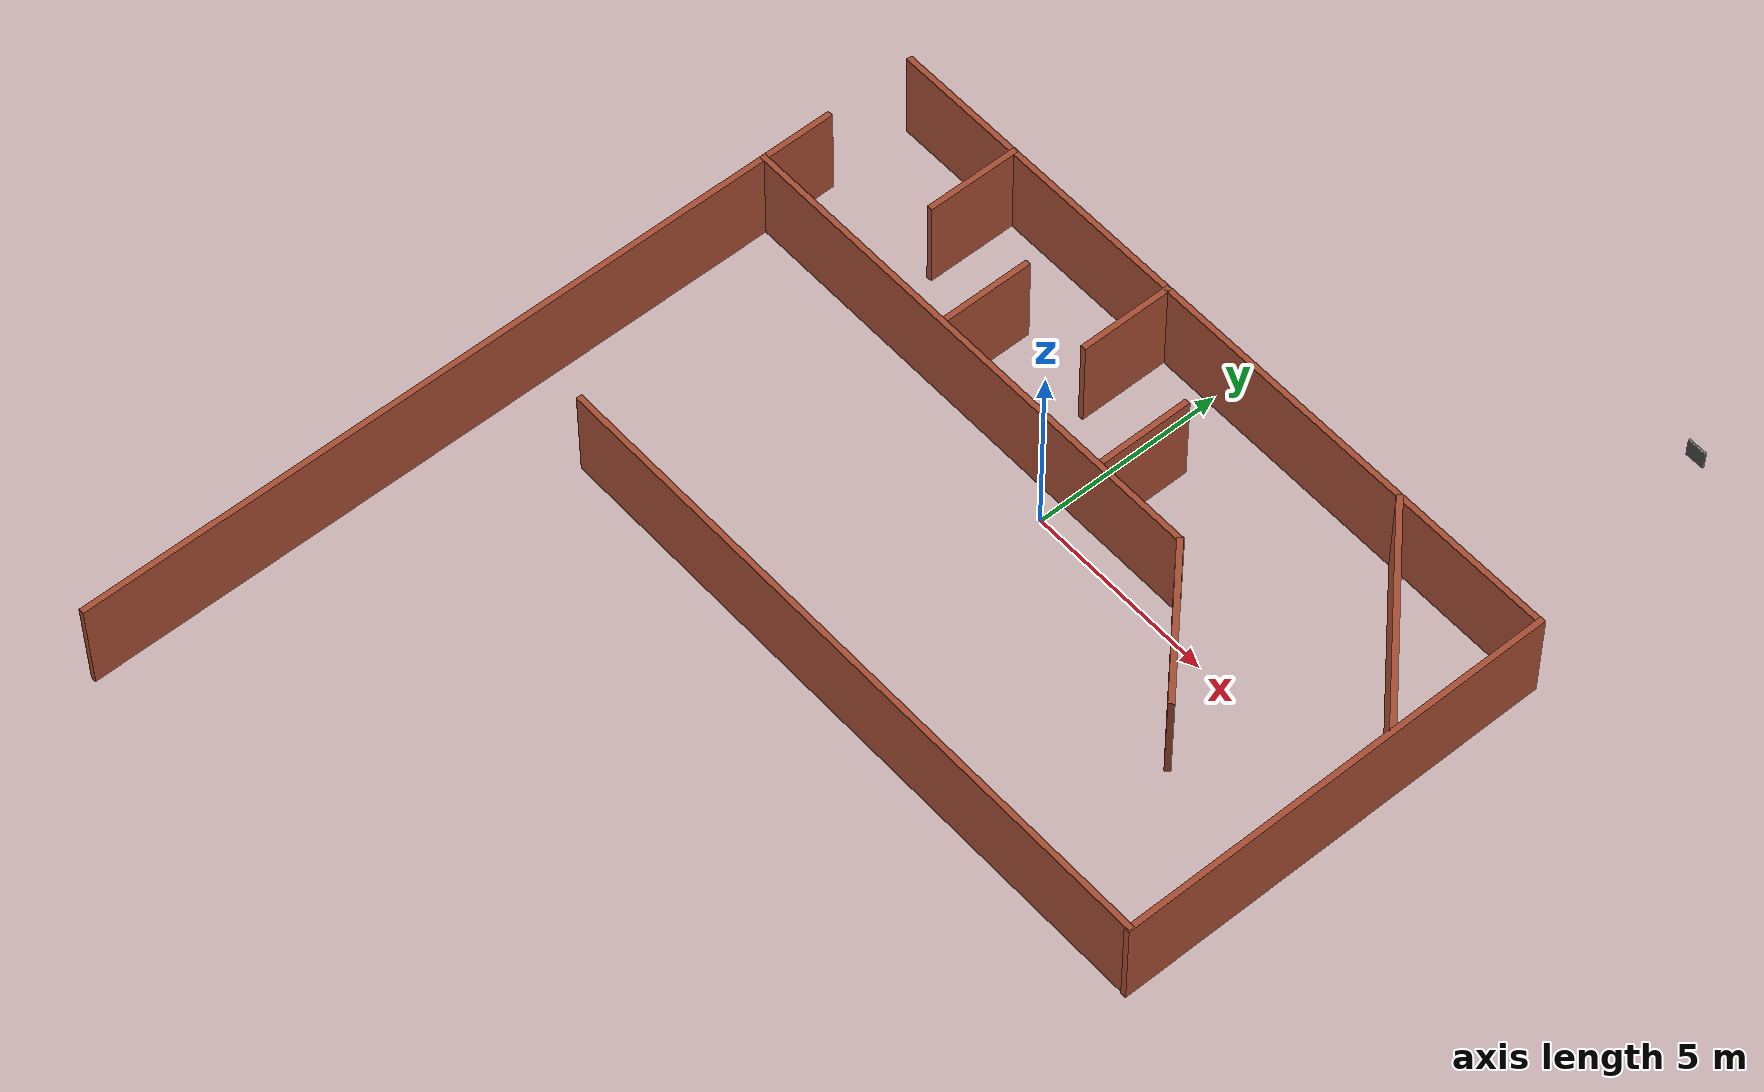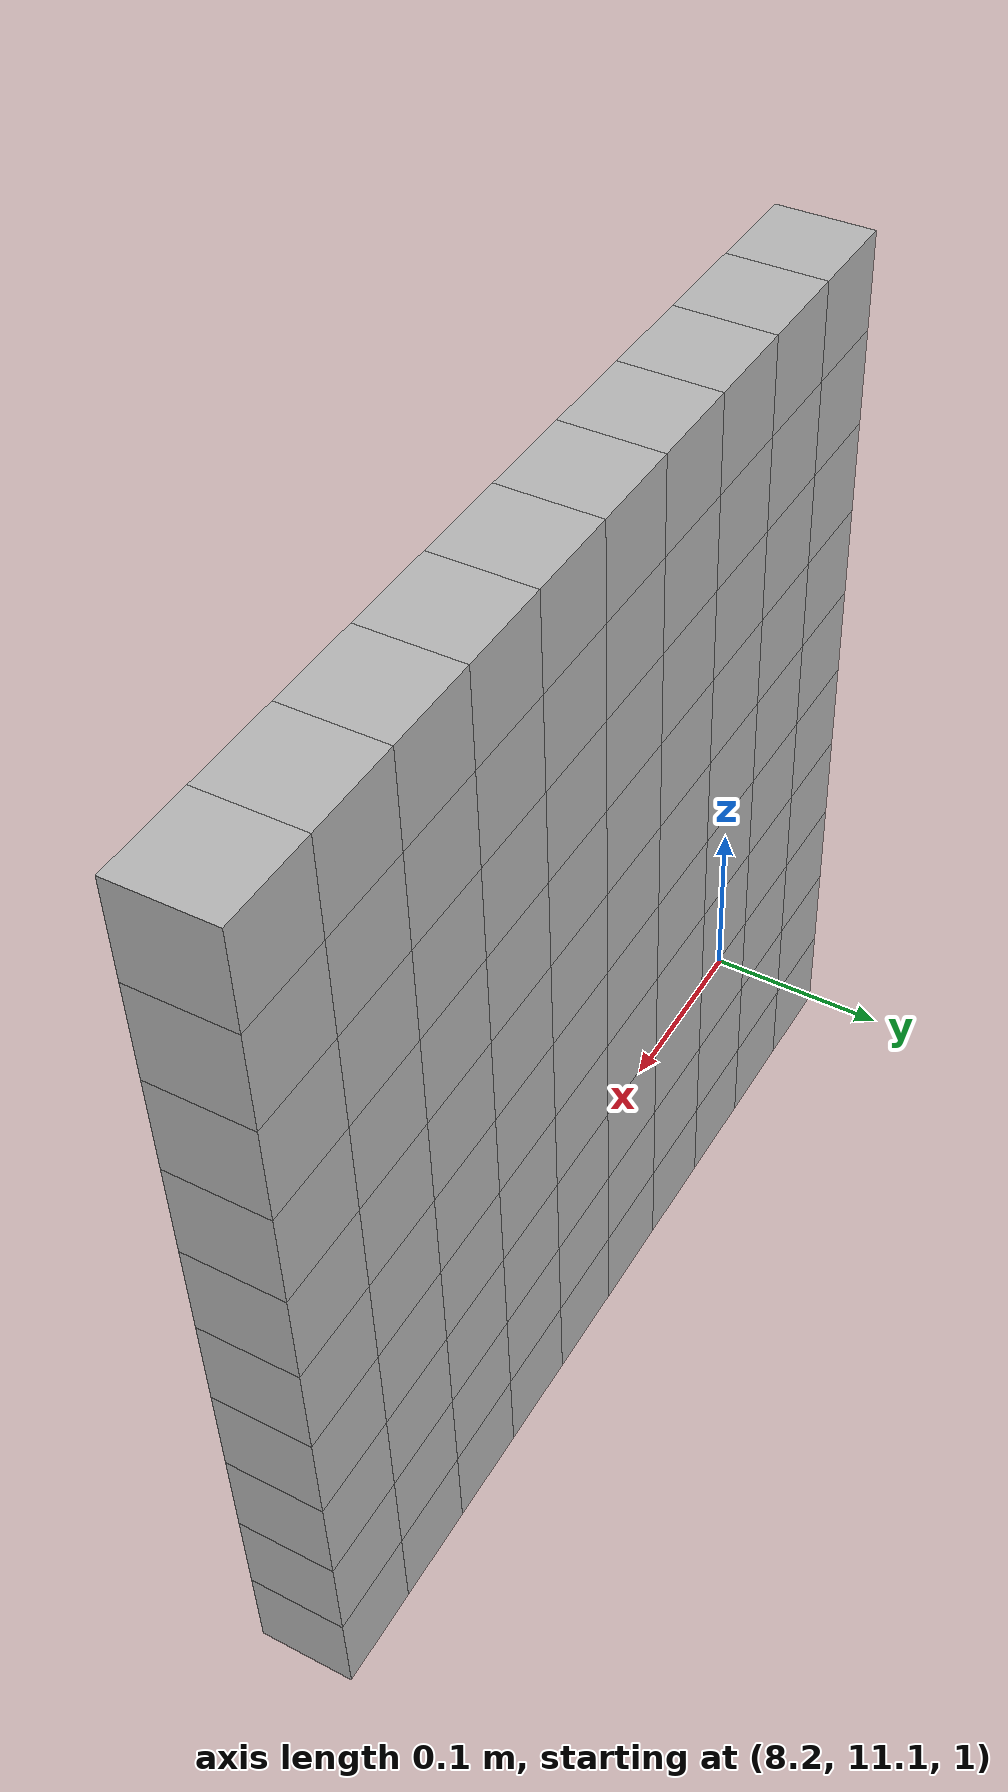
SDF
<?xml version='1.0'?>
<sdf version='1.6'>
  <model name='arena_walls'>
    <link name='Wall_10'>
      <pose frame=''>-6.5 3.71248 0 0 0 -1.5708</pose>
      <inertial>
        <mass>1</mass>
        <pose frame=''>0 0 0 0 -0 0</pose>
        <inertia>
          <ixx>1</ixx>
          <ixy>0</ixy>
          <ixz>0</ixz>
          <iyy>1</iyy>
          <iyz>0</iyz>
          <izz>1</izz>
        </inertia>
      </inertial>
      <self_collide>0</self_collide>
      <kinematic>0</kinematic>
      <visual name='Wall_10_Visual'>
        <pose frame=''>0 0 1.25 0 -0 0</pose>
        <geometry>
          <box>
            <size>2.5 0.15 2.5</size>
          </box>
        </geometry>
        <material>
          <script>
            <uri>file://media/materials/scripts/gazebo.material</uri>
            <name>Gazebo/Bricks</name>
          </script>
          <ambient>1 1 1 1</ambient>
          <shader type='pixel'>
            <normal_map>__default__</normal_map>
          </shader>
          <diffuse>1 1 1 1</diffuse>
          <specular>0.2 0.2 0.2 1</specular>
          <emissive>0 0 0 1</emissive>
        </material>
        <meta>
          <layer>0</layer>
        </meta>
        <transparency>0</transparency>
        <cast_shadows>1</cast_shadows>
      </visual>
      <collision name='Wall_10_Collision'>
        <laser_retro>0</laser_retro>
        <max_contacts>10</max_contacts>
        <pose frame=''>0 0 1.25 0 -0 0</pose>
        <geometry>
          <box>
            <size>2.5 0.15 2.5</size>
          </box>
        </geometry>
        <surface>
          <friction>
            <ode>
              <mu>1</mu>
              <mu2>1</mu2>
              <fdir1>0 0 0</fdir1>
              <slip1>0</slip1>
              <slip2>0</slip2>
            </ode>
            <torsional>
              <coefficient>1</coefficient>
              <patch_radius>0</patch_radius>
              <surface_radius>0</surface_radius>
              <use_patch_radius>1</use_patch_radius>
              <ode>
                <slip>0</slip>
              </ode>
            </torsional>
          </friction>
          <bounce>
            <restitution_coefficient>0</restitution_coefficient>
            <threshold>1e+06</threshold>
          </bounce>
          <contact>
            <collide_without_contact>0</collide_without_contact>
            <collide_without_contact_bitmask>1</collide_without_contact_bitmask>
            <collide_bitmask>1</collide_bitmask>
            <ode>
              <soft_cfm>0</soft_cfm>
              <soft_erp>0.2</soft_erp>
              <kp>1e+13</kp>
              <kd>1</kd>
              <max_vel>0.01</max_vel>
              <min_depth>0</min_depth>
            </ode>
            <bullet>
              <split_impulse>1</split_impulse>
              <split_impulse_penetration_threshold>-0.01</split_impulse_penetration_threshold>
              <soft_cfm>0</soft_cfm>
              <soft_erp>0.2</soft_erp>
              <kp>1e+13</kp>
              <kd>1</kd>
            </bullet>
          </contact>
        </surface>
      </collision>
    </link>
    <link name='Wall_10_clone_0'>
      <pose frame=''>-1.5 3.70851 0 0 0 -1.5708</pose>
      <inertial>
        <mass>1</mass>
        <pose frame=''>0 0 0 0 -0 0</pose>
        <inertia>
          <ixx>1</ixx>
          <ixy>0</ixy>
          <ixz>0</ixz>
          <iyy>1</iyy>
          <iyz>0</iyz>
          <izz>1</izz>
        </inertia>
      </inertial>
      <self_collide>0</self_collide>
      <kinematic>0</kinematic>
      <visual name='Wall_10_Visual'>
        <pose frame=''>0 0 1.25 0 -0 0</pose>
        <geometry>
          <box>
            <size>2.5 0.15 2.5</size>
          </box>
        </geometry>
        <material>
          <script>
            <uri>file://media/materials/scripts/gazebo.material</uri>
            <name>Gazebo/Bricks</name>
          </script>
          <ambient>1 1 1 1</ambient>
          <shader type='pixel'>
            <normal_map>__default__</normal_map>
          </shader>
          <diffuse>1 1 1 1</diffuse>
          <specular>0.2 0.2 0.2 1</specular>
          <emissive>0 0 0 1</emissive>
        </material>
        <meta>
          <layer>0</layer>
        </meta>
        <transparency>0</transparency>
        <cast_shadows>1</cast_shadows>
      </visual>
      <collision name='Wall_10_Collision'>
        <laser_retro>0</laser_retro>
        <max_contacts>10</max_contacts>
        <pose frame=''>0 0 1.25 0 -0 0</pose>
        <geometry>
          <box>
            <size>2.5 0.15 2.5</size>
          </box>
        </geometry>
        <surface>
          <friction>
            <ode>
              <mu>1</mu>
              <mu2>1</mu2>
              <fdir1>0 0 0</fdir1>
              <slip1>0</slip1>
              <slip2>0</slip2>
            </ode>
            <torsional>
              <coefficient>1</coefficient>
              <patch_radius>0</patch_radius>
              <surface_radius>0</surface_radius>
              <use_patch_radius>1</use_patch_radius>
              <ode>
                <slip>0</slip>
              </ode>
            </torsional>
          </friction>
          <bounce>
            <restitution_coefficient>0</restitution_coefficient>
            <threshold>1e+06</threshold>
          </bounce>
          <contact>
            <collide_without_contact>0</collide_without_contact>
            <collide_without_contact_bitmask>1</collide_without_contact_bitmask>
            <collide_bitmask>1</collide_bitmask>
            <ode>
              <soft_cfm>0</soft_cfm>
              <soft_erp>0.2</soft_erp>
              <kp>1e+13</kp>
              <kd>1</kd>
              <max_vel>0.01</max_vel>
              <min_depth>0</min_depth>
            </ode>
            <bullet>
              <split_impulse>1</split_impulse>
              <split_impulse_penetration_threshold>-0.01</split_impulse_penetration_threshold>
              <soft_cfm>0</soft_cfm>
              <soft_erp>0.2</soft_erp>
              <kp>1e+13</kp>
              <kd>1</kd>
            </bullet>
          </contact>
        </surface>
      </collision>
    </link>
    <link name='Wall_10_clone_0_clone'>
      <pose frame=''>-4 1.85792 0 0 0 -1.5708</pose>
      <inertial>
        <mass>1</mass>
        <pose frame=''>0 0 0 0 -0 0</pose>
        <inertia>
          <ixx>1</ixx>
          <ixy>0</ixy>
          <ixz>0</ixz>
          <iyy>1</iyy>
          <iyz>0</iyz>
          <izz>1</izz>
        </inertia>
      </inertial>
      <self_collide>0</self_collide>
      <kinematic>0</kinematic>
      <visual name='Wall_10_Visual'>
        <pose frame=''>0 0 1.25 0 -0 0</pose>
        <geometry>
          <box>
            <size>2.5 0.15 2.5</size>
          </box>
        </geometry>
        <material>
          <script>
            <uri>file://media/materials/scripts/gazebo.material</uri>
            <name>Gazebo/Bricks</name>
          </script>
          <ambient>1 1 1 1</ambient>
          <shader type='pixel'>
            <normal_map>__default__</normal_map>
          </shader>
          <diffuse>1 1 1 1</diffuse>
          <specular>0.2 0.2 0.2 1</specular>
          <emissive>0 0 0 1</emissive>
        </material>
        <meta>
          <layer>0</layer>
        </meta>
        <transparency>0</transparency>
        <cast_shadows>1</cast_shadows>
      </visual>
      <collision name='Wall_10_Collision'>
        <laser_retro>0</laser_retro>
        <max_contacts>10</max_contacts>
        <pose frame=''>0 0 1.25 0 -0 0</pose>
        <geometry>
          <box>
            <size>2.5 0.15 2.5</size>
          </box>
        </geometry>
        <surface>
          <friction>
            <ode>
              <mu>1</mu>
              <mu2>1</mu2>
              <fdir1>0 0 0</fdir1>
              <slip1>0</slip1>
              <slip2>0</slip2>
            </ode>
            <torsional>
              <coefficient>1</coefficient>
              <patch_radius>0</patch_radius>
              <surface_radius>0</surface_radius>
              <use_patch_radius>1</use_patch_radius>
              <ode>
                <slip>0</slip>
              </ode>
            </torsional>
          </friction>
          <bounce>
            <restitution_coefficient>0</restitution_coefficient>
            <threshold>1e+06</threshold>
          </bounce>
          <contact>
            <collide_without_contact>0</collide_without_contact>
            <collide_without_contact_bitmask>1</collide_without_contact_bitmask>
            <collide_bitmask>1</collide_bitmask>
            <ode>
              <soft_cfm>0</soft_cfm>
              <soft_erp>0.2</soft_erp>
              <kp>1e+13</kp>
              <kd>1</kd>
              <max_vel>0.01</max_vel>
              <min_depth>0</min_depth>
            </ode>
            <bullet>
              <split_impulse>1</split_impulse>
              <split_impulse_penetration_threshold>-0.01</split_impulse_penetration_threshold>
              <soft_cfm>0</soft_cfm>
              <soft_erp>0.2</soft_erp>
              <kp>1e+13</kp>
              <kd>1</kd>
            </bullet>
          </contact>
        </surface>
      </collision>
    </link>
    <link name='Wall_10_clone_0_clone_2'>
      <pose frame=''>1 1.94635 0 0 0 -1.5708</pose>
      <inertial>
        <mass>1</mass>
        <pose frame=''>0 0 0 0 -0 0</pose>
        <inertia>
          <ixx>1</ixx>
          <ixy>0</ixy>
          <ixz>0</ixz>
          <iyy>1</iyy>
          <iyz>0</iyz>
          <izz>1</izz>
        </inertia>
      </inertial>
      <self_collide>0</self_collide>
      <kinematic>0</kinematic>
      <visual name='Wall_10_Visual'>
        <pose frame=''>0 0 1.25 0 -0 0</pose>
        <geometry>
          <box>
            <size>2.5 0.15 2.5</size>
          </box>
        </geometry>
        <material>
          <script>
            <uri>file://media/materials/scripts/gazebo.material</uri>
            <name>Gazebo/Bricks</name>
          </script>
          <ambient>1 1 1 1</ambient>
          <shader type='pixel'>
            <normal_map>__default__</normal_map>
          </shader>
          <diffuse>1 1 1 1</diffuse>
          <specular>0.2 0.2 0.2 1</specular>
          <emissive>0 0 0 1</emissive>
        </material>
        <meta>
          <layer>0</layer>
        </meta>
        <transparency>0</transparency>
        <cast_shadows>1</cast_shadows>
      </visual>
      <collision name='Wall_10_Collision'>
        <laser_retro>0</laser_retro>
        <max_contacts>10</max_contacts>
        <pose frame=''>0 0 1.25 0 -0 0</pose>
        <geometry>
          <box>
            <size>2.5 0.15 2.5</size>
          </box>
        </geometry>
        <surface>
          <friction>
            <ode>
              <mu>1</mu>
              <mu2>1</mu2>
              <fdir1>0 0 0</fdir1>
              <slip1>0</slip1>
              <slip2>0</slip2>
            </ode>
            <torsional>
              <coefficient>1</coefficient>
              <patch_radius>0</patch_radius>
              <surface_radius>0</surface_radius>
              <use_patch_radius>1</use_patch_radius>
              <ode>
                <slip>0</slip>
              </ode>
            </torsional>
          </friction>
          <bounce>
            <restitution_coefficient>0</restitution_coefficient>
            <threshold>1e+06</threshold>
          </bounce>
          <contact>
            <collide_without_contact>0</collide_without_contact>
            <collide_without_contact_bitmask>1</collide_without_contact_bitmask>
            <collide_bitmask>1</collide_bitmask>
            <ode>
              <soft_cfm>0</soft_cfm>
              <soft_erp>0.2</soft_erp>
              <kp>1e+13</kp>
              <kd>1</kd>
              <max_vel>0.01</max_vel>
              <min_depth>0</min_depth>
            </ode>
            <bullet>
              <split_impulse>1</split_impulse>
              <split_impulse_penetration_threshold>-0.01</split_impulse_penetration_threshold>
              <soft_cfm>0</soft_cfm>
              <soft_erp>0.2</soft_erp>
              <kp>1e+13</kp>
              <kd>1</kd>
            </bullet>
          </contact>
        </surface>
      </collision>
    </link>
    <link name='Wall_10_clone_0_clone_2_clone'>
      <pose frame=''>7.82658 2.81474 0 0 0 -0.78</pose>
      <inertial>
        <mass>2.38801</mass>
        <pose frame=''>0 0 0 0 -0 0</pose>
        <inertia>
          <ixx>1.24823</ixx>
          <ixy>0</ixy>
          <ixz>0</ixz>
          <iyy>8.33641</iyy>
          <iyz>0</iyz>
          <izz>7.09713</izz>
        </inertia>
      </inertial>
      <self_collide>0</self_collide>
      <kinematic>0</kinematic>
      <visual name='Wall_10_Visual'>
        <pose frame=''>0 0 1.25 0 -0 0</pose>
        <geometry>
          <box>
            <size>5.97003 0.15 2.5</size>
          </box>
        </geometry>
        <material>
          <script>
            <uri>file://media/materials/scripts/gazebo.material</uri>
            <name>Gazebo/Bricks</name>
          </script>
          <ambient>1 1 1 1</ambient>
          <shader type='pixel'>
            <normal_map>__default__</normal_map>
          </shader>
          <diffuse>1 1 1 1</diffuse>
          <specular>0.2 0.2 0.2 1</specular>
          <emissive>0 0 0 1</emissive>
        </material>
        <meta>
          <layer>0</layer>
        </meta>
        <transparency>0</transparency>
        <cast_shadows>1</cast_shadows>
      </visual>
      <collision name='Wall_10_Collision'>
        <laser_retro>0</laser_retro>
        <max_contacts>10</max_contacts>
        <pose frame=''>0 0 1.25 0 -0 0</pose>
        <geometry>
          <box>
            <size>5.97003 0.15 2.5</size>
          </box>
        </geometry>
        <surface>
          <friction>
            <ode>
              <mu>1</mu>
              <mu2>1</mu2>
              <fdir1>0 0 0</fdir1>
              <slip1>0</slip1>
              <slip2>0</slip2>
            </ode>
            <torsional>
              <coefficient>1</coefficient>
              <patch_radius>0</patch_radius>
              <surface_radius>0</surface_radius>
              <use_patch_radius>1</use_patch_radius>
              <ode>
                <slip>0</slip>
              </ode>
            </torsional>
          </friction>
          <bounce>
            <restitution_coefficient>0</restitution_coefficient>
            <threshold>1e+06</threshold>
          </bounce>
          <contact>
            <collide_without_contact>0</collide_without_contact>
            <collide_without_contact_bitmask>1</collide_without_contact_bitmask>
            <collide_bitmask>1</collide_bitmask>
            <ode>
              <soft_cfm>0</soft_cfm>
              <soft_erp>0.2</soft_erp>
              <kp>1e+13</kp>
              <kd>1</kd>
              <max_vel>0.01</max_vel>
              <min_depth>0</min_depth>
            </ode>
            <bullet>
              <split_impulse>1</split_impulse>
              <split_impulse_penetration_threshold>-0.01</split_impulse_penetration_threshold>
              <soft_cfm>0</soft_cfm>
              <soft_erp>0.2</soft_erp>
              <kp>1e+13</kp>
              <kd>1</kd>
            </bullet>
          </contact>
        </surface>
      </collision>
    </link>
    <link name='Wall_10_clone_0_clone_2_clone_clone'>
      <pose frame=''>5.00738 -0.779801 0 0 0 -0.78</pose>
      <inertial>
        <mass>1.67623</mass>
        <pose frame=''>0 0 0 0 -0 0</pose>
        <inertia>
          <ixx>0.876179</ixx>
          <ixy>0</ixy>
          <ixz>0</ixz>
          <iyy>3.32605</iyy>
          <iyz>0</iyz>
          <izz>2.45615</izz>
        </inertia>
      </inertial>
      <self_collide>0</self_collide>
      <kinematic>0</kinematic>
      <visual name='Wall_10_Visual'>
        <pose frame=''>0 0 1.25 0 -0 0</pose>
        <geometry>
          <box>
            <size>4.19058 0.15 2.5</size>
          </box>
        </geometry>
        <material>
          <script>
            <uri>file://media/materials/scripts/gazebo.material</uri>
            <name>Gazebo/Bricks</name>
          </script>
          <ambient>1 1 1 1</ambient>
          <shader type='pixel'>
            <normal_map>__default__</normal_map>
          </shader>
          <diffuse>1 1 1 1</diffuse>
          <specular>0.2 0.2 0.2 1</specular>
          <emissive>0 0 0 1</emissive>
        </material>
        <meta>
          <layer>0</layer>
        </meta>
        <transparency>0</transparency>
        <cast_shadows>1</cast_shadows>
      </visual>
      <collision name='Wall_10_Collision'>
        <laser_retro>0</laser_retro>
        <max_contacts>10</max_contacts>
        <pose frame=''>0 0 1.25 0 -0 0</pose>
        <geometry>
          <box>
            <size>4.19058 0.15 2.5</size>
          </box>
        </geometry>
        <surface>
          <friction>
            <ode>
              <mu>1</mu>
              <mu2>1</mu2>
              <fdir1>0 0 0</fdir1>
              <slip1>0</slip1>
              <slip2>0</slip2>
            </ode>
            <torsional>
              <coefficient>1</coefficient>
              <patch_radius>0</patch_radius>
              <surface_radius>0</surface_radius>
              <use_patch_radius>1</use_patch_radius>
              <ode>
                <slip>0</slip>
              </ode>
            </torsional>
          </friction>
          <bounce>
            <restitution_coefficient>0</restitution_coefficient>
            <threshold>1e+06</threshold>
          </bounce>
          <contact>
            <collide_without_contact>0</collide_without_contact>
            <collide_without_contact_bitmask>1</collide_without_contact_bitmask>
            <collide_bitmask>1</collide_bitmask>
            <ode>
              <soft_cfm>0</soft_cfm>
              <soft_erp>0.2</soft_erp>
              <kp>1e+13</kp>
              <kd>1</kd>
              <max_vel>0.01</max_vel>
              <min_depth>0</min_depth>
            </ode>
            <bullet>
              <split_impulse>1</split_impulse>
              <split_impulse_penetration_threshold>-0.01</split_impulse_penetration_threshold>
              <soft_cfm>0</soft_cfm>
              <soft_erp>0.2</soft_erp>
              <kp>1e+13</kp>
              <kd>1</kd>
            </bullet>
          </contact>
        </surface>
      </collision>
    </link>
    <link name='Wall_13'>
      <pose frame=''>-3.19445 0.669302 0 0 -0 3.14159</pose>
      <inertial>
        <mass>1.35897</mass>
        <pose frame=''>0 0 0 0 -0 0</pose>
        <inertia>
          <ixx>0.710346</ixx>
          <ixy>0</ixy>
          <ixz>0</ixz>
          <iyy>21.6225</iyy>
          <iyz>0</iyz>
          <izz>20.9172</izz>
        </inertia>
      </inertial>
      <self_collide>0</self_collide>
      <kinematic>0</kinematic>
      <visual name='Wall_13_Visual'>
        <pose frame=''>0 0 1.25 0 -0 0</pose>
        <geometry>
          <box>
            <size>13.5897 0.15 2.5</size>
          </box>
        </geometry>
        <material>
          <script>
            <uri>file://media/materials/scripts/gazebo.material</uri>
            <name>Gazebo/Bricks</name>
          </script>
          <ambient>1 1 1 1</ambient>
          <shader type='pixel'>
            <normal_map>__default__</normal_map>
          </shader>
          <diffuse>1 1 1 1</diffuse>
          <specular>0.2 0.2 0.2 1</specular>
          <emissive>0 0 0 1</emissive>
        </material>
        <meta>
          <layer>0</layer>
        </meta>
        <transparency>0</transparency>
        <cast_shadows>1</cast_shadows>
      </visual>
      <collision name='Wall_13_Collision'>
        <laser_retro>0</laser_retro>
        <max_contacts>10</max_contacts>
        <pose frame=''>0 0 1.25 0 -0 0</pose>
        <geometry>
          <box>
            <size>13.5897 0.15 2.5</size>
          </box>
        </geometry>
        <surface>
          <friction>
            <ode>
              <mu>1</mu>
              <mu2>1</mu2>
              <fdir1>0 0 0</fdir1>
              <slip1>0</slip1>
              <slip2>0</slip2>
            </ode>
            <torsional>
              <coefficient>1</coefficient>
              <patch_radius>0</patch_radius>
              <surface_radius>0</surface_radius>
              <use_patch_radius>1</use_patch_radius>
              <ode>
                <slip>0</slip>
              </ode>
            </torsional>
          </friction>
          <bounce>
            <restitution_coefficient>0</restitution_coefficient>
            <threshold>1e+06</threshold>
          </bounce>
          <contact>
            <collide_without_contact>0</collide_without_contact>
            <collide_without_contact_bitmask>1</collide_without_contact_bitmask>
            <collide_bitmask>1</collide_bitmask>
            <ode>
              <soft_cfm>0</soft_cfm>
              <soft_erp>0.2</soft_erp>
              <kp>1e+13</kp>
              <kd>1</kd>
              <max_vel>0.01</max_vel>
              <min_depth>0</min_depth>
            </ode>
            <bullet>
              <split_impulse>1</split_impulse>
              <split_impulse_penetration_threshold>-0.01</split_impulse_penetration_threshold>
              <soft_cfm>0</soft_cfm>
              <soft_erp>0.2</soft_erp>
              <kp>1e+13</kp>
              <kd>1</kd>
            </bullet>
          </contact>
        </surface>
      </collision>
    </link>
    <link name='Wall_2'>
      <pose frame=''>0.003794 4.89766 0 0 -0 0</pose>
      <inertial>
        <mass>1</mass>
        <pose frame=''>0 0 0 0 -0 0</pose>
        <inertia>
          <ixx>1</ixx>
          <ixy>0</ixy>
          <ixz>0</ixz>
          <iyy>1</iyy>
          <iyz>0</iyz>
          <izz>1</izz>
        </inertia>
      </inertial>
      <self_collide>0</self_collide>
      <kinematic>0</kinematic>
      <visual name='Wall_2_Visual'>
        <pose frame=''>0 0 1.25 0 -0 0</pose>
        <geometry>
          <box>
            <size>20 0.15 2.5</size>
          </box>
        </geometry>
        <material>
          <script>
            <uri>file://media/materials/scripts/gazebo.material</uri>
            <name>Gazebo/Bricks</name>
          </script>
          <ambient>1 1 1 1</ambient>
          <shader type='pixel'>
            <normal_map>__default__</normal_map>
          </shader>
          <diffuse>1 1 1 1</diffuse>
          <specular>0.2 0.2 0.2 1</specular>
          <emissive>0 0 0 1</emissive>
        </material>
        <meta>
          <layer>0</layer>
        </meta>
        <transparency>0</transparency>
        <cast_shadows>1</cast_shadows>
      </visual>
      <collision name='Wall_2_Collision'>
        <laser_retro>0</laser_retro>
        <max_contacts>10</max_contacts>
        <pose frame=''>0 0 1.25 0 -0 0</pose>
        <geometry>
          <box>
            <size>20 0.15 2.5</size>
          </box>
        </geometry>
        <surface>
          <friction>
            <ode>
              <mu>1</mu>
              <mu2>1</mu2>
              <fdir1>0 0 0</fdir1>
              <slip1>0</slip1>
              <slip2>0</slip2>
            </ode>
            <torsional>
              <coefficient>1</coefficient>
              <patch_radius>0</patch_radius>
              <surface_radius>0</surface_radius>
              <use_patch_radius>1</use_patch_radius>
              <ode>
                <slip>0</slip>
              </ode>
            </torsional>
          </friction>
          <bounce>
            <restitution_coefficient>0</restitution_coefficient>
            <threshold>1e+06</threshold>
          </bounce>
          <contact>
            <collide_without_contact>0</collide_without_contact>
            <collide_without_contact_bitmask>1</collide_without_contact_bitmask>
            <collide_bitmask>1</collide_bitmask>
            <ode>
              <soft_cfm>0</soft_cfm>
              <soft_erp>0.2</soft_erp>
              <kp>1e+13</kp>
              <kd>1</kd>
              <max_vel>0.01</max_vel>
              <min_depth>0</min_depth>
            </ode>
            <bullet>
              <split_impulse>1</split_impulse>
              <split_impulse_penetration_threshold>-0.01</split_impulse_penetration_threshold>
              <soft_cfm>0</soft_cfm>
              <soft_erp>0.2</soft_erp>
              <kp>1e+13</kp>
              <kd>1</kd>
            </bullet>
          </contact>
        </surface>
      </collision>
    </link>
    <link name='Wall_2_clone'>
      <pose frame=''>1.24205 -6.48449 0 0 -0 0</pose>
      <inertial>
        <mass>1</mass>
        <pose frame=''>0 0 0 0 -0 0</pose>
        <inertia>
          <ixx>1</ixx>
          <ixy>0</ixy>
          <ixz>0</ixz>
          <iyy>1</iyy>
          <iyz>0</iyz>
          <izz>1</izz>
        </inertia>
      </inertial>
      <self_collide>0</self_collide>
      <kinematic>0</kinematic>
      <visual name='Wall_2_Visual'>
        <pose frame=''>0 0 1.25 0 -0 0</pose>
        <geometry>
          <box>
            <size>17.5 0.15 2.5</size>
          </box>
        </geometry>
        <material>
          <script>
            <uri>file://media/materials/scripts/gazebo.material</uri>
            <name>Gazebo/Bricks</name>
          </script>
          <ambient>1 1 1 1</ambient>
          <shader type='pixel'>
            <normal_map>__default__</normal_map>
          </shader>
          <diffuse>1 1 1 1</diffuse>
          <specular>0.2 0.2 0.2 1</specular>
          <emissive>0 0 0 1</emissive>
        </material>
        <meta>
          <layer>0</layer>
        </meta>
        <transparency>0</transparency>
        <cast_shadows>1</cast_shadows>
      </visual>
      <collision name='Wall_2_Collision'>
        <laser_retro>0</laser_retro>
        <max_contacts>10</max_contacts>
        <pose frame=''>0 0 1.25 0 -0 0</pose>
        <geometry>
          <box>
            <size>17.5 0.15 2.5</size>
          </box>
        </geometry>
        <surface>
          <friction>
            <ode>
              <mu>1</mu>
              <mu2>1</mu2>
              <fdir1>0 0 0</fdir1>
              <slip1>0</slip1>
              <slip2>0</slip2>
            </ode>
            <torsional>
              <coefficient>1</coefficient>
              <patch_radius>0</patch_radius>
              <surface_radius>0</surface_radius>
              <use_patch_radius>1</use_patch_radius>
              <ode>
                <slip>0</slip>
              </ode>
            </torsional>
          </friction>
          <bounce>
            <restitution_coefficient>0</restitution_coefficient>
            <threshold>1e+06</threshold>
          </bounce>
          <contact>
            <collide_without_contact>0</collide_without_contact>
            <collide_without_contact_bitmask>1</collide_without_contact_bitmask>
            <collide_bitmask>1</collide_bitmask>
            <ode>
              <soft_cfm>0</soft_cfm>
              <soft_erp>0.2</soft_erp>
              <kp>1e+13</kp>
              <kd>1</kd>
              <max_vel>0.01</max_vel>
              <min_depth>0</min_depth>
            </ode>
            <bullet>
              <split_impulse>1</split_impulse>
              <split_impulse_penetration_threshold>-0.01</split_impulse_penetration_threshold>
              <soft_cfm>0</soft_cfm>
              <soft_erp>0.2</soft_erp>
              <kp>1e+13</kp>
              <kd>1</kd>
            </bullet>
          </contact>
        </surface>
      </collision>
    </link>
    <link name='Wall_4'>
      <pose frame=''>9.94646 -0.804145 0 0 0 -1.5708</pose>
      <inertial>
        <inertia>
          <ixx>0</ixx>
          <ixy>0</ixy>
          <ixz>0</ixz>
          <iyy>0</iyy>
          <iyz>0</iyz>
          <izz>0</izz>
        </inertia>
        <mass>0</mass>
        <pose frame=''>0 0 0 0 -0 0</pose>
      </inertial>
      <self_collide>0</self_collide>
      <kinematic>0</kinematic>
      <visual name='Wall_4_Visual'>
        <pose frame=''>0 0 1.25 0 -0 0</pose>
        <geometry>
          <box>
            <size>11.5685 0.15 2.5</size>
          </box>
        </geometry>
        <material>
          <script>
            <uri>file://media/materials/scripts/gazebo.material</uri>
            <name>Gazebo/Bricks</name>
          </script>
          <ambient>1 1 1 1</ambient>
          <shader type='pixel'>
            <normal_map>__default__</normal_map>
          </shader>
          <diffuse>1 1 1 1</diffuse>
          <specular>0.2 0.2 0.2 1</specular>
          <emissive>0 0 0 1</emissive>
        </material>
        <meta>
          <layer>0</layer>
        </meta>
        <transparency>0</transparency>
        <cast_shadows>1</cast_shadows>
      </visual>
      <collision name='Wall_4_Collision'>
        <laser_retro>0</laser_retro>
        <max_contacts>10</max_contacts>
        <pose frame=''>0 0 1.25 0 -0 0</pose>
        <geometry>
          <box>
            <size>11.5685 0.15 2.5</size>
          </box>
        </geometry>
        <surface>
          <friction>
            <ode>
              <mu>1</mu>
              <mu2>1</mu2>
              <fdir1>0 0 0</fdir1>
              <slip1>0</slip1>
              <slip2>0</slip2>
            </ode>
            <torsional>
              <coefficient>1</coefficient>
              <patch_radius>0</patch_radius>
              <surface_radius>0</surface_radius>
              <use_patch_radius>1</use_patch_radius>
              <ode>
                <slip>0</slip>
              </ode>
            </torsional>
          </friction>
          <bounce>
            <restitution_coefficient>0</restitution_coefficient>
            <threshold>1e+06</threshold>
          </bounce>
          <contact>
            <collide_without_contact>0</collide_without_contact>
            <collide_without_contact_bitmask>1</collide_without_contact_bitmask>
            <collide_bitmask>1</collide_bitmask>
            <ode>
              <soft_cfm>0</soft_cfm>
              <soft_erp>0.2</soft_erp>
              <kp>1e+13</kp>
              <kd>1</kd>
              <max_vel>0.01</max_vel>
              <min_depth>0</min_depth>
            </ode>
            <bullet>
              <split_impulse>1</split_impulse>
              <split_impulse_penetration_threshold>-0.01</split_impulse_penetration_threshold>
              <soft_cfm>0</soft_cfm>
              <soft_erp>0.2</soft_erp>
              <kp>1e+13</kp>
              <kd>1</kd>
            </bullet>
          </contact>
        </surface>
      </collision>
    </link>
    <link name='Wall_4_clone'>
      <pose frame=''>-9.92044 -7.60821 0 0 0 -1.5708</pose>
      <inertial>
        <inertia>
          <ixx>0</ixx>
          <ixy>0</ixy>
          <ixz>0</ixz>
          <iyy>0</iyy>
          <iyz>0</iyz>
          <izz>0</izz>
        </inertia>
        <mass>0</mass>
        <pose frame=''>0 0 0 0 -0 0</pose>
      </inertial>
      <self_collide>0</self_collide>
      <kinematic>0</kinematic>
      <visual name='Wall_4_Visual'>
        <pose frame=''>0 0 1.25 0 -0 0</pose>
        <geometry>
          <box>
            <size>20.3295 0.15 2.5</size>
          </box>
        </geometry>
        <material>
          <script>
            <uri>file://media/materials/scripts/gazebo.material</uri>
            <name>Gazebo/Bricks</name>
          </script>
          <ambient>1 1 1 1</ambient>
          <shader type='pixel'>
            <normal_map>__default__</normal_map>
          </shader>
          <diffuse>1 1 1 1</diffuse>
          <specular>0.2 0.2 0.2 1</specular>
          <emissive>0 0 0 1</emissive>
        </material>
        <meta>
          <layer>0</layer>
        </meta>
        <transparency>0</transparency>
        <cast_shadows>1</cast_shadows>
      </visual>
      <collision name='Wall_4_Collision'>
        <laser_retro>0</laser_retro>
        <max_contacts>10</max_contacts>
        <pose frame=''>0 0 1.25 0 -0 0</pose>
        <geometry>
          <box>
            <size>20.3295 0.15 2.5</size>
          </box>
        </geometry>
        <surface>
          <friction>
            <ode>
              <mu>1</mu>
              <mu2>1</mu2>
              <fdir1>0 0 0</fdir1>
              <slip1>0</slip1>
              <slip2>0</slip2>
            </ode>
            <torsional>
              <coefficient>1</coefficient>
              <patch_radius>0</patch_radius>
              <surface_radius>0</surface_radius>
              <use_patch_radius>1</use_patch_radius>
              <ode>
                <slip>0</slip>
              </ode>
            </torsional>
          </friction>
          <bounce>
            <restitution_coefficient>0</restitution_coefficient>
            <threshold>1e+06</threshold>
          </bounce>
          <contact>
            <collide_without_contact>0</collide_without_contact>
            <collide_without_contact_bitmask>1</collide_without_contact_bitmask>
            <collide_bitmask>1</collide_bitmask>
            <ode>
              <soft_cfm>0</soft_cfm>
              <soft_erp>0.2</soft_erp>
              <kp>1e+13</kp>
              <kd>1</kd>
              <max_vel>0.01</max_vel>
              <min_depth>0</min_depth>
            </ode>
            <bullet>
              <split_impulse>1</split_impulse>
              <split_impulse_penetration_threshold>-0.01</split_impulse_penetration_threshold>
              <soft_cfm>0</soft_cfm>
              <soft_erp>0.2</soft_erp>
              <kp>1e+13</kp>
              <kd>1</kd>
            </bullet>
          </contact>
        </surface>
      </collision>
    </link>
    <model name='breakable_test'>
      <pose frame=''>8.20387 11.1254 1 0 -0 0</pose>
      <link name='link_0_0'>
        <pose frame=''>0 0 0 0 -0 0</pose>
        <inertial>
          <mass>0.3375</mass>
          <inertia>
            <ixx>0.000140625</ixx>
            <iyy>0.000140625</iyy>
            <izz>0.000140625</izz>
            <ixy>0</ixy>
            <ixz>0</ixz>
            <iyz>0</iyz>
          </inertia>
        </inertial>
        <collision name='collision'>
          <geometry>
            <box>
              <size>0.05 0.05 0.05</size>
            </box>
          </geometry>
          <max_contacts>10</max_contacts>
          <surface>
            <contact>
              <ode/>
            </contact>
            <bounce/>
            <friction>
              <torsional>
                <ode/>
              </torsional>
              <ode/>
            </friction>
          </surface>
        </collision>
        <visual name='visual'>
          <geometry>
            <box>
              <size>0.05 0.05 0.05</size>
            </box>
          </geometry>
        </visual>
        <self_collide>0</self_collide>
        <kinematic>0</kinematic>
      </link>
      <joint name='joint_0_0' type='revolute'>
        <parent>world</parent>
        <child>link_0_0</child>
        <axis>
          <xyz>0 0 1</xyz>
          <limit>
            <lower>0</lower>
            <upper>0</upper>
          </limit>
          <use_parent_model_frame>1</use_parent_model_frame>
          <dynamics>
            <spring_reference>0</spring_reference>
            <spring_stiffness>0</spring_stiffness>
          </dynamics>
        </axis>
        <physics>
          <ode>
            <erp>1</erp>
            <cfm>1</cfm>
            <limit>
              <cfm>0</cfm>
              <erp>0.2</erp>
            </limit>
          </ode>
        </physics>
        <sensor name='force_torque' type='force_torque'>
          <always_on>1</always_on>
          <update_rate>1000</update_rate>
          <plugin name='breakable_0_0' filename='libBreakableJointPlugin.so'>
            <breaking_force_N>50</breaking_force_N>
          </plugin>
        </sensor>
      </joint>
      <link name='link_0_1'>
        <pose frame=''>0 0 0.05 0 -0 0</pose>
        <inertial>
          <mass>0.3375</mass>
          <inertia>
            <ixx>0.000140625</ixx>
            <iyy>0.000140625</iyy>
            <izz>0.000140625</izz>
            <ixy>0</ixy>
            <ixz>0</ixz>
            <iyz>0</iyz>
          </inertia>
        </inertial>
        <collision name='collision'>
          <geometry>
            <box>
              <size>0.05 0.05 0.05</size>
            </box>
          </geometry>
          <max_contacts>10</max_contacts>
          <surface>
            <contact>
              <ode/>
            </contact>
            <bounce/>
            <friction>
              <torsional>
                <ode/>
              </torsional>
              <ode/>
            </friction>
          </surface>
        </collision>
        <visual name='visual'>
          <geometry>
            <box>
              <size>0.05 0.05 0.05</size>
            </box>
          </geometry>
        </visual>
        <self_collide>0</self_collide>
        <kinematic>0</kinematic>
      </link>
      <joint name='joint_0_1' type='revolute'>
        <parent>world</parent>
        <child>link_0_1</child>
        <axis>
          <xyz>0 0 1</xyz>
          <limit>
            <lower>0</lower>
            <upper>0</upper>
          </limit>
          <use_parent_model_frame>1</use_parent_model_frame>
          <dynamics>
            <spring_reference>0</spring_reference>
            <spring_stiffness>0</spring_stiffness>
          </dynamics>
        </axis>
        <physics>
          <ode>
            <erp>1</erp>
            <cfm>1</cfm>
            <limit>
              <cfm>0</cfm>
              <erp>0.2</erp>
            </limit>
          </ode>
        </physics>
        <sensor name='force_torque' type='force_torque'>
          <always_on>1</always_on>
          <update_rate>1000</update_rate>
          <plugin name='breakable_0_1' filename='libBreakableJointPlugin.so'>
            <breaking_force_N>50</breaking_force_N>
          </plugin>
        </sensor>
      </joint>
      <link name='link_0_2'>
        <pose frame=''>0 0 0.1 0 -0 0</pose>
        <inertial>
          <mass>0.3375</mass>
          <inertia>
            <ixx>0.000140625</ixx>
            <iyy>0.000140625</iyy>
            <izz>0.000140625</izz>
            <ixy>0</ixy>
            <ixz>0</ixz>
            <iyz>0</iyz>
          </inertia>
        </inertial>
        <collision name='collision'>
          <geometry>
            <box>
              <size>0.05 0.05 0.05</size>
            </box>
          </geometry>
          <max_contacts>10</max_contacts>
          <surface>
            <contact>
              <ode/>
            </contact>
            <bounce/>
            <friction>
              <torsional>
                <ode/>
              </torsional>
              <ode/>
            </friction>
          </surface>
        </collision>
        <visual name='visual'>
          <geometry>
            <box>
              <size>0.05 0.05 0.05</size>
            </box>
          </geometry>
        </visual>
        <self_collide>0</self_collide>
        <kinematic>0</kinematic>
      </link>
      <joint name='joint_0_2' type='revolute'>
        <parent>world</parent>
        <child>link_0_2</child>
        <axis>
          <xyz>0 0 1</xyz>
          <limit>
            <lower>0</lower>
            <upper>0</upper>
          </limit>
          <use_parent_model_frame>1</use_parent_model_frame>
          <dynamics>
            <spring_reference>0</spring_reference>
            <spring_stiffness>0</spring_stiffness>
          </dynamics>
        </axis>
        <physics>
          <ode>
            <erp>1</erp>
            <cfm>1</cfm>
            <limit>
              <cfm>0</cfm>
              <erp>0.2</erp>
            </limit>
          </ode>
        </physics>
        <sensor name='force_torque' type='force_torque'>
          <always_on>1</always_on>
          <update_rate>1000</update_rate>
          <plugin name='breakable_0_2' filename='libBreakableJointPlugin.so'>
            <breaking_force_N>50</breaking_force_N>
          </plugin>
        </sensor>
      </joint>
      <link name='link_0_3'>
        <pose frame=''>0 0 0.15 0 -0 0</pose>
        <inertial>
          <mass>0.3375</mass>
          <inertia>
            <ixx>0.000140625</ixx>
            <iyy>0.000140625</iyy>
            <izz>0.000140625</izz>
            <ixy>0</ixy>
            <ixz>0</ixz>
            <iyz>0</iyz>
          </inertia>
        </inertial>
        <collision name='collision'>
          <geometry>
            <box>
              <size>0.05 0.05 0.05</size>
            </box>
          </geometry>
          <max_contacts>10</max_contacts>
          <surface>
            <contact>
              <ode/>
            </contact>
            <bounce/>
            <friction>
              <torsional>
                <ode/>
              </torsional>
              <ode/>
            </friction>
          </surface>
        </collision>
        <visual name='visual'>
          <geometry>
            <box>
              <size>0.05 0.05 0.05</size>
            </box>
          </geometry>
        </visual>
        <self_collide>0</self_collide>
        <kinematic>0</kinematic>
      </link>
      <joint name='joint_0_3' type='revolute'>
        <parent>world</parent>
        <child>link_0_3</child>
        <axis>
          <xyz>0 0 1</xyz>
          <limit>
            <lower>0</lower>
            <upper>0</upper>
          </limit>
          <use_parent_model_frame>1</use_parent_model_frame>
          <dynamics>
            <spring_reference>0</spring_reference>
            <spring_stiffness>0</spring_stiffness>
          </dynamics>
        </axis>
        <physics>
          <ode>
            <erp>1</erp>
            <cfm>1</cfm>
            <limit>
              <cfm>0</cfm>
              <erp>0.2</erp>
            </limit>
          </ode>
        </physics>
        <sensor name='force_torque' type='force_torque'>
          <always_on>1</always_on>
          <update_rate>1000</update_rate>
          <plugin name='breakable_0_3' filename='libBreakableJointPlugin.so'>
            <breaking_force_N>50</breaking_force_N>
          </plugin>
        </sensor>
      </joint>
      <link name='link_0_4'>
        <pose frame=''>0 0 0.2 0 -0 0</pose>
        <inertial>
          <mass>0.3375</mass>
          <inertia>
            <ixx>0.000140625</ixx>
            <iyy>0.000140625</iyy>
            <izz>0.000140625</izz>
            <ixy>0</ixy>
            <ixz>0</ixz>
            <iyz>0</iyz>
          </inertia>
        </inertial>
        <collision name='collision'>
          <geometry>
            <box>
              <size>0.05 0.05 0.05</size>
            </box>
          </geometry>
          <max_contacts>10</max_contacts>
          <surface>
            <contact>
              <ode/>
            </contact>
            <bounce/>
            <friction>
              <torsional>
                <ode/>
              </torsional>
              <ode/>
            </friction>
          </surface>
        </collision>
        <visual name='visual'>
          <geometry>
            <box>
              <size>0.05 0.05 0.05</size>
            </box>
          </geometry>
        </visual>
        <self_collide>0</self_collide>
        <kinematic>0</kinematic>
      </link>
      <joint name='joint_0_4' type='revolute'>
        <parent>world</parent>
        <child>link_0_4</child>
        <axis>
          <xyz>0 0 1</xyz>
          <limit>
            <lower>0</lower>
            <upper>0</upper>
          </limit>
          <use_parent_model_frame>1</use_parent_model_frame>
          <dynamics>
            <spring_reference>0</spring_reference>
            <spring_stiffness>0</spring_stiffness>
          </dynamics>
        </axis>
        <physics>
          <ode>
            <erp>1</erp>
            <cfm>1</cfm>
            <limit>
              <cfm>0</cfm>
              <erp>0.2</erp>
            </limit>
          </ode>
        </physics>
        <sensor name='force_torque' type='force_torque'>
          <always_on>1</always_on>
          <update_rate>1000</update_rate>
          <plugin name='breakable_0_4' filename='libBreakableJointPlugin.so'>
            <breaking_force_N>50</breaking_force_N>
          </plugin>
        </sensor>
      </joint>
      <link name='link_0_5'>
        <pose frame=''>0 0 0.25 0 -0 0</pose>
        <inertial>
          <mass>0.3375</mass>
          <inertia>
            <ixx>0.000140625</ixx>
            <iyy>0.000140625</iyy>
            <izz>0.000140625</izz>
            <ixy>0</ixy>
            <ixz>0</ixz>
            <iyz>0</iyz>
          </inertia>
        </inertial>
        <collision name='collision'>
          <geometry>
            <box>
              <size>0.05 0.05 0.05</size>
            </box>
          </geometry>
          <max_contacts>10</max_contacts>
          <surface>
            <contact>
              <ode/>
            </contact>
            <bounce/>
            <friction>
              <torsional>
                <ode/>
              </torsional>
              <ode/>
            </friction>
          </surface>
        </collision>
        <visual name='visual'>
          <geometry>
            <box>
              <size>0.05 0.05 0.05</size>
            </box>
          </geometry>
        </visual>
        <self_collide>0</self_collide>
        <kinematic>0</kinematic>
      </link>
      <joint name='joint_0_5' type='revolute'>
        <parent>world</parent>
        <child>link_0_5</child>
        <axis>
          <xyz>0 0 1</xyz>
          <limit>
            <lower>0</lower>
            <upper>0</upper>
          </limit>
          <use_parent_model_frame>1</use_parent_model_frame>
          <dynamics>
            <spring_reference>0</spring_reference>
            <spring_stiffness>0</spring_stiffness>
          </dynamics>
        </axis>
        <physics>
          <ode>
            <erp>1</erp>
            <cfm>1</cfm>
            <limit>
              <cfm>0</cfm>
              <erp>0.2</erp>
            </limit>
          </ode>
        </physics>
        <sensor name='force_torque' type='force_torque'>
          <always_on>1</always_on>
          <update_rate>1000</update_rate>
          <plugin name='breakable_0_5' filename='libBreakableJointPlugin.so'>
            <breaking_force_N>50</breaking_force_N>
          </plugin>
        </sensor>
      </joint>
      <link name='link_0_6'>
        <pose frame=''>0 0 0.3 0 -0 0</pose>
        <inertial>
          <mass>0.3375</mass>
          <inertia>
            <ixx>0.000140625</ixx>
            <iyy>0.000140625</iyy>
            <izz>0.000140625</izz>
            <ixy>0</ixy>
            <ixz>0</ixz>
            <iyz>0</iyz>
          </inertia>
        </inertial>
        <collision name='collision'>
          <geometry>
            <box>
              <size>0.05 0.05 0.05</size>
            </box>
          </geometry>
          <max_contacts>10</max_contacts>
          <surface>
            <contact>
              <ode/>
            </contact>
            <bounce/>
            <friction>
              <torsional>
                <ode/>
              </torsional>
              <ode/>
            </friction>
          </surface>
        </collision>
        <visual name='visual'>
          <geometry>
            <box>
              <size>0.05 0.05 0.05</size>
            </box>
          </geometry>
        </visual>
        <self_collide>0</self_collide>
        <kinematic>0</kinematic>
      </link>
      <joint name='joint_0_6' type='revolute'>
        <parent>world</parent>
        <child>link_0_6</child>
        <axis>
          <xyz>0 0 1</xyz>
          <limit>
            <lower>0</lower>
            <upper>0</upper>
          </limit>
          <use_parent_model_frame>1</use_parent_model_frame>
          <dynamics>
            <spring_reference>0</spring_reference>
            <spring_stiffness>0</spring_stiffness>
          </dynamics>
        </axis>
        <physics>
          <ode>
            <erp>1</erp>
            <cfm>1</cfm>
            <limit>
              <cfm>0</cfm>
              <erp>0.2</erp>
            </limit>
          </ode>
        </physics>
        <sensor name='force_torque' type='force_torque'>
          <always_on>1</always_on>
          <update_rate>1000</update_rate>
          <plugin name='breakable_0_6' filename='libBreakableJointPlugin.so'>
            <breaking_force_N>50</breaking_force_N>
          </plugin>
        </sensor>
      </joint>
      <link name='link_0_7'>
        <pose frame=''>0 0 0.35 0 -0 0</pose>
        <inertial>
          <mass>0.3375</mass>
          <inertia>
            <ixx>0.000140625</ixx>
            <iyy>0.000140625</iyy>
            <izz>0.000140625</izz>
            <ixy>0</ixy>
            <ixz>0</ixz>
            <iyz>0</iyz>
          </inertia>
        </inertial>
        <collision name='collision'>
          <geometry>
            <box>
              <size>0.05 0.05 0.05</size>
            </box>
          </geometry>
          <max_contacts>10</max_contacts>
          <surface>
            <contact>
              <ode/>
            </contact>
            <bounce/>
            <friction>
              <torsional>
                <ode/>
              </torsional>
              <ode/>
            </friction>
          </surface>
        </collision>
        <visual name='visual'>
          <geometry>
            <box>
              <size>0.05 0.05 0.05</size>
            </box>
          </geometry>
        </visual>
        <self_collide>0</self_collide>
        <kinematic>0</kinematic>
      </link>
      <joint name='joint_0_7' type='revolute'>
        <parent>world</parent>
        <child>link_0_7</child>
        <axis>
          <xyz>0 0 1</xyz>
          <limit>
            <lower>0</lower>
            <upper>0</upper>
          </limit>
          <use_parent_model_frame>1</use_parent_model_frame>
          <dynamics>
            <spring_reference>0</spring_reference>
            <spring_stiffness>0</spring_stiffness>
          </dynamics>
        </axis>
        <physics>
          <ode>
            <erp>1</erp>
            <cfm>1</cfm>
            <limit>
              <cfm>0</cfm>
              <erp>0.2</erp>
            </limit>
          </ode>
        </physics>
        <sensor name='force_torque' type='force_torque'>
          <always_on>1</always_on>
          <update_rate>1000</update_rate>
          <plugin name='breakable_0_7' filename='libBreakableJointPlugin.so'>
            <breaking_force_N>50</breaking_force_N>
          </plugin>
        </sensor>
      </joint>
      <link name='link_0_8'>
        <pose frame=''>0 0 0.4 0 -0 0</pose>
        <inertial>
          <mass>0.3375</mass>
          <inertia>
            <ixx>0.000140625</ixx>
            <iyy>0.000140625</iyy>
            <izz>0.000140625</izz>
            <ixy>0</ixy>
            <ixz>0</ixz>
            <iyz>0</iyz>
          </inertia>
        </inertial>
        <collision name='collision'>
          <geometry>
            <box>
              <size>0.05 0.05 0.05</size>
            </box>
          </geometry>
          <max_contacts>10</max_contacts>
          <surface>
            <contact>
              <ode/>
            </contact>
            <bounce/>
            <friction>
              <torsional>
                <ode/>
              </torsional>
              <ode/>
            </friction>
          </surface>
        </collision>
        <visual name='visual'>
          <geometry>
            <box>
              <size>0.05 0.05 0.05</size>
            </box>
          </geometry>
        </visual>
        <self_collide>0</self_collide>
        <kinematic>0</kinematic>
      </link>
      <joint name='joint_0_8' type='revolute'>
        <parent>world</parent>
        <child>link_0_8</child>
        <axis>
          <xyz>0 0 1</xyz>
          <limit>
            <lower>0</lower>
            <upper>0</upper>
          </limit>
          <use_parent_model_frame>1</use_parent_model_frame>
          <dynamics>
            <spring_reference>0</spring_reference>
            <spring_stiffness>0</spring_stiffness>
          </dynamics>
        </axis>
        <physics>
          <ode>
            <erp>1</erp>
            <cfm>1</cfm>
            <limit>
              <cfm>0</cfm>
              <erp>0.2</erp>
            </limit>
          </ode>
        </physics>
        <sensor name='force_torque' type='force_torque'>
          <always_on>1</always_on>
          <update_rate>1000</update_rate>
          <plugin name='breakable_0_8' filename='libBreakableJointPlugin.so'>
            <breaking_force_N>50</breaking_force_N>
          </plugin>
        </sensor>
      </joint>
      <link name='link_0_9'>
        <pose frame=''>0 0 0.45 0 -0 0</pose>
        <inertial>
          <mass>0.3375</mass>
          <inertia>
            <ixx>0.000140625</ixx>
            <iyy>0.000140625</iyy>
            <izz>0.000140625</izz>
            <ixy>0</ixy>
            <ixz>0</ixz>
            <iyz>0</iyz>
          </inertia>
        </inertial>
        <collision name='collision'>
          <geometry>
            <box>
              <size>0.05 0.05 0.05</size>
            </box>
          </geometry>
          <max_contacts>10</max_contacts>
          <surface>
            <contact>
              <ode/>
            </contact>
            <bounce/>
            <friction>
              <torsional>
                <ode/>
              </torsional>
              <ode/>
            </friction>
          </surface>
        </collision>
        <visual name='visual'>
          <geometry>
            <box>
              <size>0.05 0.05 0.05</size>
            </box>
          </geometry>
        </visual>
        <self_collide>0</self_collide>
        <kinematic>0</kinematic>
      </link>
      <joint name='joint_0_9' type='revolute'>
        <parent>world</parent>
        <child>link_0_9</child>
        <axis>
          <xyz>0 0 1</xyz>
          <limit>
            <lower>0</lower>
            <upper>0</upper>
          </limit>
          <use_parent_model_frame>1</use_parent_model_frame>
          <dynamics>
            <spring_reference>0</spring_reference>
            <spring_stiffness>0</spring_stiffness>
          </dynamics>
        </axis>
        <physics>
          <ode>
            <erp>1</erp>
            <cfm>1</cfm>
            <limit>
              <cfm>0</cfm>
              <erp>0.2</erp>
            </limit>
          </ode>
        </physics>
        <sensor name='force_torque' type='force_torque'>
          <always_on>1</always_on>
          <update_rate>1000</update_rate>
          <plugin name='breakable_0_9' filename='libBreakableJointPlugin.so'>
            <breaking_force_N>50</breaking_force_N>
          </plugin>
        </sensor>
      </joint>
      <link name='link_1_0'>
        <pose frame=''>0.05 0 0 0 -0 0</pose>
        <inertial>
          <mass>0.3375</mass>
          <inertia>
            <ixx>0.000140625</ixx>
            <iyy>0.000140625</iyy>
            <izz>0.000140625</izz>
            <ixy>0</ixy>
            <ixz>0</ixz>
            <iyz>0</iyz>
          </inertia>
        </inertial>
        <collision name='collision'>
          <geometry>
            <box>
              <size>0.05 0.05 0.05</size>
            </box>
          </geometry>
          <max_contacts>10</max_contacts>
          <surface>
            <contact>
              <ode/>
            </contact>
            <bounce/>
            <friction>
              <torsional>
                <ode/>
              </torsional>
              <ode/>
            </friction>
          </surface>
        </collision>
        <visual name='visual'>
          <geometry>
            <box>
              <size>0.05 0.05 0.05</size>
            </box>
          </geometry>
        </visual>
        <self_collide>0</self_collide>
        <kinematic>0</kinematic>
      </link>
      <joint name='joint_1_0' type='revolute'>
        <parent>world</parent>
        <child>link_1_0</child>
        <axis>
          <xyz>0 0 1</xyz>
          <limit>
            <lower>0</lower>
            <upper>0</upper>
          </limit>
          <use_parent_model_frame>1</use_parent_model_frame>
          <dynamics>
            <spring_reference>0</spring_reference>
            <spring_stiffness>0</spring_stiffness>
          </dynamics>
        </axis>
        <physics>
          <ode>
            <erp>1</erp>
            <cfm>1</cfm>
            <limit>
              <cfm>0</cfm>
              <erp>0.2</erp>
            </limit>
          </ode>
        </physics>
        <sensor name='force_torque' type='force_torque'>
          <always_on>1</always_on>
          <update_rate>1000</update_rate>
          <plugin name='breakable_1_0' filename='libBreakableJointPlugin.so'>
            <breaking_force_N>50</breaking_force_N>
          </plugin>
        </sensor>
      </joint>
      <link name='link_1_1'>
        <pose frame=''>0.05 0 0.05 0 -0 0</pose>
        <inertial>
          <mass>0.3375</mass>
          <inertia>
            <ixx>0.000140625</ixx>
            <iyy>0.000140625</iyy>
            <izz>0.000140625</izz>
            <ixy>0</ixy>
            <ixz>0</ixz>
            <iyz>0</iyz>
          </inertia>
        </inertial>
        <collision name='collision'>
          <geometry>
            <box>
              <size>0.05 0.05 0.05</size>
            </box>
          </geometry>
          <max_contacts>10</max_contacts>
          <surface>
            <contact>
              <ode/>
            </contact>
            <bounce/>
            <friction>
              <torsional>
                <ode/>
              </torsional>
              <ode/>
            </friction>
          </surface>
        </collision>
        <visual name='visual'>
          <geometry>
            <box>
              <size>0.05 0.05 0.05</size>
            </box>
          </geometry>
        </visual>
        <self_collide>0</self_collide>
        <kinematic>0</kinematic>
      </link>
      <joint name='joint_1_1' type='revolute'>
        <parent>world</parent>
        <child>link_1_1</child>
        <axis>
          <xyz>0 0 1</xyz>
          <limit>
            <lower>0</lower>
            <upper>0</upper>
          </limit>
          <use_parent_model_frame>1</use_parent_model_frame>
          <dynamics>
            <spring_reference>0</spring_reference>
            <spring_stiffness>0</spring_stiffness>
          </dynamics>
        </axis>
        <physics>
          <ode>
            <erp>1</erp>
            <cfm>1</cfm>
            <limit>
              <cfm>0</cfm>
              <erp>0.2</erp>
            </limit>
          </ode>
        </physics>
        <sensor name='force_torque' type='force_torque'>
          <always_on>1</always_on>
          <update_rate>1000</update_rate>
          <plugin name='breakable_1_1' filename='libBreakableJointPlugin.so'>
            <breaking_force_N>50</breaking_force_N>
          </plugin>
        </sensor>
      </joint>
      <link name='link_1_2'>
        <pose frame=''>0.05 0 0.1 0 -0 0</pose>
        <inertial>
          <mass>0.3375</mass>
          <inertia>
            <ixx>0.000140625</ixx>
            <iyy>0.000140625</iyy>
            <izz>0.000140625</izz>
            <ixy>0</ixy>
            <ixz>0</ixz>
            <iyz>0</iyz>
          </inertia>
        </inertial>
        <collision name='collision'>
          <geometry>
            <box>
              <size>0.05 0.05 0.05</size>
            </box>
          </geometry>
          <max_contacts>10</max_contacts>
          <surface>
            <contact>
              <ode/>
            </contact>
            <bounce/>
            <friction>
              <torsional>
                <ode/>
              </torsional>
              <ode/>
            </friction>
          </surface>
        </collision>
        <visual name='visual'>
          <geometry>
            <box>
              <size>0.05 0.05 0.05</size>
            </box>
          </geometry>
        </visual>
        <self_collide>0</self_collide>
        <kinematic>0</kinematic>
      </link>
      <joint name='joint_1_2' type='revolute'>
        <parent>world</parent>
        <child>link_1_2</child>
        <axis>
          <xyz>0 0 1</xyz>
          <limit>
            <lower>0</lower>
            <upper>0</upper>
          </limit>
          <use_parent_model_frame>1</use_parent_model_frame>
          <dynamics>
            <spring_reference>0</spring_reference>
            <spring_stiffness>0</spring_stiffness>
          </dynamics>
        </axis>
        <physics>
          <ode>
            <erp>1</erp>
            <cfm>1</cfm>
            <limit>
              <cfm>0</cfm>
              <erp>0.2</erp>
            </limit>
          </ode>
        </physics>
        <sensor name='force_torque' type='force_torque'>
          <always_on>1</always_on>
          <update_rate>1000</update_rate>
          <plugin name='breakable_1_2' filename='libBreakableJointPlugin.so'>
            <breaking_force_N>50</breaking_force_N>
          </plugin>
        </sensor>
      </joint>
      <link name='link_1_3'>
        <pose frame=''>0.05 0 0.15 0 -0 0</pose>
        <inertial>
          <mass>0.3375</mass>
          <inertia>
            <ixx>0.000140625</ixx>
            <iyy>0.000140625</iyy>
            <izz>0.000140625</izz>
            <ixy>0</ixy>
            <ixz>0</ixz>
            <iyz>0</iyz>
          </inertia>
        </inertial>
        <collision name='collision'>
          <geometry>
            <box>
              <size>0.05 0.05 0.05</size>
            </box>
          </geometry>
          <max_contacts>10</max_contacts>
          <surface>
            <contact>
              <ode/>
            </contact>
            <bounce/>
            <friction>
              <torsional>
                <ode/>
              </torsional>
              <ode/>
            </friction>
          </surface>
        </collision>
        <visual name='visual'>
          <geometry>
            <box>
              <size>0.05 0.05 0.05</size>
            </box>
          </geometry>
        </visual>
        <self_collide>0</self_collide>
        <kinematic>0</kinematic>
      </link>
      <joint name='joint_1_3' type='revolute'>
        <parent>world</parent>
        <child>link_1_3</child>
        <axis>
          <xyz>0 0 1</xyz>
          <limit>
            <lower>0</lower>
            <upper>0</upper>
          </limit>
          <use_parent_model_frame>1</use_parent_model_frame>
          <dynamics>
            <spring_reference>0</spring_reference>
            <spring_stiffness>0</spring_stiffness>
          </dynamics>
        </axis>
        <physics>
          <ode>
            <erp>1</erp>
            <cfm>1</cfm>
            <limit>
              <cfm>0</cfm>
              <erp>0.2</erp>
            </limit>
          </ode>
        </physics>
        <sensor name='force_torque' type='force_torque'>
          <always_on>1</always_on>
          <update_rate>1000</update_rate>
          <plugin name='breakable_1_3' filename='libBreakableJointPlugin.so'>
            <breaking_force_N>50</breaking_force_N>
          </plugin>
        </sensor>
      </joint>
      <link name='link_1_4'>
        <pose frame=''>0.05 0 0.2 0 -0 0</pose>
        <inertial>
          <mass>0.3375</mass>
          <inertia>
            <ixx>0.000140625</ixx>
            <iyy>0.000140625</iyy>
            <izz>0.000140625</izz>
            <ixy>0</ixy>
            <ixz>0</ixz>
            <iyz>0</iyz>
          </inertia>
        </inertial>
        <collision name='collision'>
          <geometry>
            <box>
              <size>0.05 0.05 0.05</size>
            </box>
          </geometry>
          <max_contacts>10</max_contacts>
          <surface>
            <contact>
              <ode/>
            </contact>
            <bounce/>
            <friction>
              <torsional>
                <ode/>
              </torsional>
              <ode/>
            </friction>
          </surface>
        </collision>
        <visual name='visual'>
          <geometry>
            <box>
              <size>0.05 0.05 0.05</size>
            </box>
          </geometry>
        </visual>
        <self_collide>0</self_collide>
        <kinematic>0</kinematic>
      </link>
      <joint name='joint_1_4' type='revolute'>
        <parent>world</parent>
        <child>link_1_4</child>
        <axis>
          <xyz>0 0 1</xyz>
          <limit>
            <lower>0</lower>
            <upper>0</upper>
          </limit>
          <use_parent_model_frame>1</use_parent_model_frame>
          <dynamics>
            <spring_reference>0</spring_reference>
            <spring_stiffness>0</spring_stiffness>
          </dynamics>
        </axis>
        <physics>
          <ode>
            <erp>1</erp>
            <cfm>1</cfm>
            <limit>
              <cfm>0</cfm>
              <erp>0.2</erp>
            </limit>
          </ode>
        </physics>
        <sensor name='force_torque' type='force_torque'>
          <always_on>1</always_on>
          <update_rate>1000</update_rate>
          <plugin name='breakable_1_4' filename='libBreakableJointPlugin.so'>
            <breaking_force_N>50</breaking_force_N>
          </plugin>
        </sensor>
      </joint>
      <link name='link_1_5'>
        <pose frame=''>0.05 0 0.25 0 -0 0</pose>
        <inertial>
          <mass>0.3375</mass>
          <inertia>
            <ixx>0.000140625</ixx>
            <iyy>0.000140625</iyy>
            <izz>0.000140625</izz>
            <ixy>0</ixy>
            <ixz>0</ixz>
            <iyz>0</iyz>
          </inertia>
        </inertial>
        <collision name='collision'>
          <geometry>
            <box>
              <size>0.05 0.05 0.05</size>
            </box>
          </geometry>
          <max_contacts>10</max_contacts>
          <surface>
            <contact>
              <ode/>
            </contact>
            <bounce/>
            <friction>
              <torsional>
                <ode/>
              </torsional>
              <ode/>
            </friction>
          </surface>
        </collision>
        <visual name='visual'>
          <geometry>
            <box>
              <size>0.05 0.05 0.05</size>
            </box>
          </geometry>
        </visual>
        <self_collide>0</self_collide>
        <kinematic>0</kinematic>
      </link>
      <joint name='joint_1_5' type='revolute'>
        <parent>world</parent>
        <child>link_1_5</child>
        <axis>
          <xyz>0 0 1</xyz>
          <limit>
            <lower>0</lower>
            <upper>0</upper>
          </limit>
          <use_parent_model_frame>1</use_parent_model_frame>
          <dynamics>
            <spring_reference>0</spring_reference>
            <spring_stiffness>0</spring_stiffness>
          </dynamics>
        </axis>
        <physics>
          <ode>
            <erp>1</erp>
            <cfm>1</cfm>
            <limit>
              <cfm>0</cfm>
              <erp>0.2</erp>
            </limit>
          </ode>
        </physics>
        <sensor name='force_torque' type='force_torque'>
          <always_on>1</always_on>
          <update_rate>1000</update_rate>
          <plugin name='breakable_1_5' filename='libBreakableJointPlugin.so'>
            <breaking_force_N>50</breaking_force_N>
          </plugin>
        </sensor>
      </joint>
      <link name='link_1_6'>
        <pose frame=''>0.05 0 0.3 0 -0 0</pose>
        <inertial>
          <mass>0.3375</mass>
          <inertia>
            <ixx>0.000140625</ixx>
            <iyy>0.000140625</iyy>
            <izz>0.000140625</izz>
            <ixy>0</ixy>
            <ixz>0</ixz>
            <iyz>0</iyz>
          </inertia>
        </inertial>
        <collision name='collision'>
          <geometry>
            <box>
              <size>0.05 0.05 0.05</size>
            </box>
          </geometry>
          <max_contacts>10</max_contacts>
          <surface>
            <contact>
              <ode/>
            </contact>
            <bounce/>
            <friction>
              <torsional>
                <ode/>
              </torsional>
              <ode/>
            </friction>
          </surface>
        </collision>
        <visual name='visual'>
          <geometry>
            <box>
              <size>0.05 0.05 0.05</size>
            </box>
          </geometry>
        </visual>
        <self_collide>0</self_collide>
        <kinematic>0</kinematic>
      </link>
      <joint name='joint_1_6' type='revolute'>
        <parent>world</parent>
        <child>link_1_6</child>
        <axis>
          <xyz>0 0 1</xyz>
          <limit>
            <lower>0</lower>
            <upper>0</upper>
          </limit>
          <use_parent_model_frame>1</use_parent_model_frame>
          <dynamics>
            <spring_reference>0</spring_reference>
            <spring_stiffness>0</spring_stiffness>
          </dynamics>
        </axis>
        <physics>
          <ode>
            <erp>1</erp>
            <cfm>1</cfm>
            <limit>
              <cfm>0</cfm>
              <erp>0.2</erp>
            </limit>
          </ode>
        </physics>
        <sensor name='force_torque' type='force_torque'>
          <always_on>1</always_on>
          <update_rate>1000</update_rate>
          <plugin name='breakable_1_6' filename='libBreakableJointPlugin.so'>
            <breaking_force_N>50</breaking_force_N>
          </plugin>
        </sensor>
      </joint>
      <link name='link_1_7'>
        <pose frame=''>0.05 0 0.35 0 -0 0</pose>
        <inertial>
          <mass>0.3375</mass>
          <inertia>
            <ixx>0.000140625</ixx>
            <iyy>0.000140625</iyy>
            <izz>0.000140625</izz>
            <ixy>0</ixy>
            <ixz>0</ixz>
            <iyz>0</iyz>
          </inertia>
        </inertial>
        <collision name='collision'>
          <geometry>
            <box>
              <size>0.05 0.05 0.05</size>
            </box>
          </geometry>
          <max_contacts>10</max_contacts>
          <surface>
            <contact>
              <ode/>
            </contact>
            <bounce/>
            <friction>
              <torsional>
                <ode/>
              </torsional>
              <ode/>
            </friction>
          </surface>
        </collision>
        <visual name='visual'>
          <geometry>
            <box>
              <size>0.05 0.05 0.05</size>
            </box>
          </geometry>
        </visual>
        <self_collide>0</self_collide>
        <kinematic>0</kinematic>
      </link>
      <joint name='joint_1_7' type='revolute'>
        <parent>world</parent>
        <child>link_1_7</child>
        <axis>
          <xyz>0 0 1</xyz>
          <limit>
            <lower>0</lower>
            <upper>0</upper>
          </limit>
          <use_parent_model_frame>1</use_parent_model_frame>
          <dynamics>
            <spring_reference>0</spring_reference>
            <spring_stiffness>0</spring_stiffness>
          </dynamics>
        </axis>
        <physics>
          <ode>
            <erp>1</erp>
            <cfm>1</cfm>
            <limit>
              <cfm>0</cfm>
              <erp>0.2</erp>
            </limit>
          </ode>
        </physics>
        <sensor name='force_torque' type='force_torque'>
          <always_on>1</always_on>
          <update_rate>1000</update_rate>
          <plugin name='breakable_1_7' filename='libBreakableJointPlugin.so'>
            <breaking_force_N>50</breaking_force_N>
          </plugin>
        </sensor>
      </joint>
      <link name='link_1_8'>
        <pose frame=''>0.05 0 0.4 0 -0 0</pose>
        <inertial>
          <mass>0.3375</mass>
          <inertia>
            <ixx>0.000140625</ixx>
            <iyy>0.000140625</iyy>
            <izz>0.000140625</izz>
            <ixy>0</ixy>
            <ixz>0</ixz>
            <iyz>0</iyz>
          </inertia>
        </inertial>
        <collision name='collision'>
          <geometry>
            <box>
              <size>0.05 0.05 0.05</size>
            </box>
          </geometry>
          <max_contacts>10</max_contacts>
          <surface>
            <contact>
              <ode/>
            </contact>
            <bounce/>
            <friction>
              <torsional>
                <ode/>
              </torsional>
              <ode/>
            </friction>
          </surface>
        </collision>
        <visual name='visual'>
          <geometry>
            <box>
              <size>0.05 0.05 0.05</size>
            </box>
          </geometry>
        </visual>
        <self_collide>0</self_collide>
        <kinematic>0</kinematic>
      </link>
      <joint name='joint_1_8' type='revolute'>
        <parent>world</parent>
        <child>link_1_8</child>
        <axis>
          <xyz>0 0 1</xyz>
          <limit>
            <lower>0</lower>
            <upper>0</upper>
          </limit>
          <use_parent_model_frame>1</use_parent_model_frame>
          <dynamics>
            <spring_reference>0</spring_reference>
            <spring_stiffness>0</spring_stiffness>
          </dynamics>
        </axis>
        <physics>
          <ode>
            <erp>1</erp>
            <cfm>1</cfm>
            <limit>
              <cfm>0</cfm>
              <erp>0.2</erp>
            </limit>
          </ode>
        </physics>
        <sensor name='force_torque' type='force_torque'>
          <always_on>1</always_on>
          <update_rate>1000</update_rate>
          <plugin name='breakable_1_8' filename='libBreakableJointPlugin.so'>
            <breaking_force_N>50</breaking_force_N>
          </plugin>
        </sensor>
      </joint>
      <link name='link_1_9'>
        <pose frame=''>0.05 0 0.45 0 -0 0</pose>
        <inertial>
          <mass>0.3375</mass>
          <inertia>
            <ixx>0.000140625</ixx>
            <iyy>0.000140625</iyy>
            <izz>0.000140625</izz>
            <ixy>0</ixy>
            <ixz>0</ixz>
            <iyz>0</iyz>
          </inertia>
        </inertial>
        <collision name='collision'>
          <geometry>
            <box>
              <size>0.05 0.05 0.05</size>
            </box>
          </geometry>
          <max_contacts>10</max_contacts>
          <surface>
            <contact>
              <ode/>
            </contact>
            <bounce/>
            <friction>
              <torsional>
                <ode/>
              </torsional>
              <ode/>
            </friction>
          </surface>
        </collision>
        <visual name='visual'>
          <geometry>
            <box>
              <size>0.05 0.05 0.05</size>
            </box>
          </geometry>
        </visual>
        <self_collide>0</self_collide>
        <kinematic>0</kinematic>
      </link>
      <joint name='joint_1_9' type='revolute'>
        <parent>world</parent>
        <child>link_1_9</child>
        <axis>
          <xyz>0 0 1</xyz>
          <limit>
            <lower>0</lower>
            <upper>0</upper>
          </limit>
          <use_parent_model_frame>1</use_parent_model_frame>
          <dynamics>
            <spring_reference>0</spring_reference>
            <spring_stiffness>0</spring_stiffness>
          </dynamics>
        </axis>
        <physics>
          <ode>
            <erp>1</erp>
            <cfm>1</cfm>
            <limit>
              <cfm>0</cfm>
              <erp>0.2</erp>
            </limit>
          </ode>
        </physics>
        <sensor name='force_torque' type='force_torque'>
          <always_on>1</always_on>
          <update_rate>1000</update_rate>
          <plugin name='breakable_1_9' filename='libBreakableJointPlugin.so'>
            <breaking_force_N>50</breaking_force_N>
          </plugin>
        </sensor>
      </joint>
      <link name='link_2_0'>
        <pose frame=''>0.1 0 0 0 -0 0</pose>
        <inertial>
          <mass>0.3375</mass>
          <inertia>
            <ixx>0.000140625</ixx>
            <iyy>0.000140625</iyy>
            <izz>0.000140625</izz>
            <ixy>0</ixy>
            <ixz>0</ixz>
            <iyz>0</iyz>
          </inertia>
        </inertial>
        <collision name='collision'>
          <geometry>
            <box>
              <size>0.05 0.05 0.05</size>
            </box>
          </geometry>
          <max_contacts>10</max_contacts>
          <surface>
            <contact>
              <ode/>
            </contact>
            <bounce/>
            <friction>
              <torsional>
                <ode/>
              </torsional>
              <ode/>
            </friction>
          </surface>
        </collision>
        <visual name='visual'>
          <geometry>
            <box>
              <size>0.05 0.05 0.05</size>
            </box>
          </geometry>
        </visual>
        <self_collide>0</self_collide>
        <kinematic>0</kinematic>
      </link>
      <joint name='joint_2_0' type='revolute'>
        <parent>world</parent>
        <child>link_2_0</child>
        <axis>
          <xyz>0 0 1</xyz>
          <limit>
            <lower>0</lower>
            <upper>0</upper>
          </limit>
          <use_parent_model_frame>1</use_parent_model_frame>
          <dynamics>
            <spring_reference>0</spring_reference>
            <spring_stiffness>0</spring_stiffness>
          </dynamics>
        </axis>
        <physics>
          <ode>
            <erp>1</erp>
            <cfm>1</cfm>
            <limit>
              <cfm>0</cfm>
              <erp>0.2</erp>
            </limit>
          </ode>
        </physics>
        <sensor name='force_torque' type='force_torque'>
          <always_on>1</always_on>
          <update_rate>1000</update_rate>
          <plugin name='breakable_2_0' filename='libBreakableJointPlugin.so'>
            <breaking_force_N>50</breaking_force_N>
          </plugin>
        </sensor>
      </joint>
      <link name='link_2_1'>
        <pose frame=''>0.1 0 0.05 0 -0 0</pose>
        <inertial>
          <mass>0.3375</mass>
          <inertia>
            <ixx>0.000140625</ixx>
            <iyy>0.000140625</iyy>
            <izz>0.000140625</izz>
            <ixy>0</ixy>
            <ixz>0</ixz>
            <iyz>0</iyz>
          </inertia>
        </inertial>
        <collision name='collision'>
          <geometry>
            <box>
              <size>0.05 0.05 0.05</size>
            </box>
          </geometry>
          <max_contacts>10</max_contacts>
          <surface>
            <contact>
              <ode/>
            </contact>
            <bounce/>
            <friction>
              <torsional>
                <ode/>
              </torsional>
              <ode/>
            </friction>
          </surface>
        </collision>
        <visual name='visual'>
          <geometry>
            <box>
              <size>0.05 0.05 0.05</size>
            </box>
          </geometry>
        </visual>
        <self_collide>0</self_collide>
        <kinematic>0</kinematic>
      </link>
      <joint name='joint_2_1' type='revolute'>
        <parent>world</parent>
        <child>link_2_1</child>
        <axis>
          <xyz>0 0 1</xyz>
          <limit>
            <lower>0</lower>
            <upper>0</upper>
          </limit>
          <use_parent_model_frame>1</use_parent_model_frame>
          <dynamics>
            <spring_reference>0</spring_reference>
            <spring_stiffness>0</spring_stiffness>
          </dynamics>
        </axis>
        <physics>
          <ode>
            <erp>1</erp>
            <cfm>1</cfm>
            <limit>
              <cfm>0</cfm>
              <erp>0.2</erp>
            </limit>
          </ode>
        </physics>
        <sensor name='force_torque' type='force_torque'>
          <always_on>1</always_on>
          <update_rate>1000</update_rate>
          <plugin name='breakable_2_1' filename='libBreakableJointPlugin.so'>
            <breaking_force_N>50</breaking_force_N>
          </plugin>
        </sensor>
      </joint>
      <link name='link_2_2'>
        <pose frame=''>0.1 0 0.1 0 -0 0</pose>
        <inertial>
          <mass>0.3375</mass>
          <inertia>
            <ixx>0.000140625</ixx>
            <iyy>0.000140625</iyy>
            <izz>0.000140625</izz>
            <ixy>0</ixy>
            <ixz>0</ixz>
            <iyz>0</iyz>
          </inertia>
        </inertial>
        <collision name='collision'>
          <geometry>
            <box>
              <size>0.05 0.05 0.05</size>
            </box>
          </geometry>
          <max_contacts>10</max_contacts>
          <surface>
            <contact>
              <ode/>
            </contact>
            <bounce/>
            <friction>
              <torsional>
                <ode/>
              </torsional>
              <ode/>
            </friction>
          </surface>
        </collision>
        <visual name='visual'>
          <geometry>
            <box>
              <size>0.05 0.05 0.05</size>
            </box>
          </geometry>
        </visual>
        <self_collide>0</self_collide>
        <kinematic>0</kinematic>
      </link>
      <joint name='joint_2_2' type='revolute'>
        <parent>world</parent>
        <child>link_2_2</child>
        <axis>
          <xyz>0 0 1</xyz>
          <limit>
            <lower>0</lower>
            <upper>0</upper>
          </limit>
          <use_parent_model_frame>1</use_parent_model_frame>
          <dynamics>
            <spring_reference>0</spring_reference>
            <spring_stiffness>0</spring_stiffness>
          </dynamics>
        </axis>
        <physics>
          <ode>
            <erp>1</erp>
            <cfm>1</cfm>
            <limit>
              <cfm>0</cfm>
              <erp>0.2</erp>
            </limit>
          </ode>
        </physics>
        <sensor name='force_torque' type='force_torque'>
          <always_on>1</always_on>
          <update_rate>1000</update_rate>
          <plugin name='breakable_2_2' filename='libBreakableJointPlugin.so'>
            <breaking_force_N>50</breaking_force_N>
          </plugin>
        </sensor>
      </joint>
      <link name='link_2_3'>
        <pose frame=''>0.1 0 0.15 0 -0 0</pose>
        <inertial>
          <mass>0.3375</mass>
          <inertia>
            <ixx>0.000140625</ixx>
            <iyy>0.000140625</iyy>
            <izz>0.000140625</izz>
            <ixy>0</ixy>
            <ixz>0</ixz>
            <iyz>0</iyz>
          </inertia>
        </inertial>
        <collision name='collision'>
          <geometry>
            <box>
              <size>0.05 0.05 0.05</size>
            </box>
          </geometry>
          <max_contacts>10</max_contacts>
          <surface>
            <contact>
              <ode/>
            </contact>
            <bounce/>
            <friction>
              <torsional>
                <ode/>
              </torsional>
              <ode/>
            </friction>
          </surface>
        </collision>
        <visual name='visual'>
          <geometry>
            <box>
              <size>0.05 0.05 0.05</size>
            </box>
          </geometry>
        </visual>
        <self_collide>0</self_collide>
        <kinematic>0</kinematic>
      </link>
      <joint name='joint_2_3' type='revolute'>
        <parent>world</parent>
        <child>link_2_3</child>
        <axis>
          <xyz>0 0 1</xyz>
          <limit>
            <lower>0</lower>
            <upper>0</upper>
          </limit>
          <use_parent_model_frame>1</use_parent_model_frame>
          <dynamics>
            <spring_reference>0</spring_reference>
            <spring_stiffness>0</spring_stiffness>
          </dynamics>
        </axis>
        <physics>
          <ode>
            <erp>1</erp>
            <cfm>1</cfm>
            <limit>
              <cfm>0</cfm>
              <erp>0.2</erp>
            </limit>
          </ode>
        </physics>
        <sensor name='force_torque' type='force_torque'>
          <always_on>1</always_on>
          <update_rate>1000</update_rate>
          <plugin name='breakable_2_3' filename='libBreakableJointPlugin.so'>
            <breaking_force_N>50</breaking_force_N>
          </plugin>
        </sensor>
      </joint>
      <link name='link_2_4'>
        <pose frame=''>0.1 0 0.2 0 -0 0</pose>
        <inertial>
          <mass>0.3375</mass>
          <inertia>
            <ixx>0.000140625</ixx>
            <iyy>0.000140625</iyy>
            <izz>0.000140625</izz>
            <ixy>0</ixy>
            <ixz>0</ixz>
            <iyz>0</iyz>
          </inertia>
        </inertial>
        <collision name='collision'>
          <geometry>
            <box>
              <size>0.05 0.05 0.05</size>
            </box>
          </geometry>
          <max_contacts>10</max_contacts>
          <surface>
            <contact>
              <ode/>
            </contact>
            <bounce/>
            <friction>
              <torsional>
                <ode/>
              </torsional>
              <ode/>
            </friction>
          </surface>
        </collision>
        <visual name='visual'>
          <geometry>
            <box>
              <size>0.05 0.05 0.05</size>
            </box>
          </geometry>
        </visual>
        <self_collide>0</self_collide>
        <kinematic>0</kinematic>
      </link>
      <joint name='joint_2_4' type='revolute'>
        <parent>world</parent>
        <child>link_2_4</child>
        <axis>
          <xyz>0 0 1</xyz>
          <limit>
            <lower>0</lower>
            <upper>0</upper>
          </limit>
          <use_parent_model_frame>1</use_parent_model_frame>
          <dynamics>
            <spring_reference>0</spring_reference>
            <spring_stiffness>0</spring_stiffness>
          </dynamics>
        </axis>
        <physics>
          <ode>
            <erp>1</erp>
            <cfm>1</cfm>
            <limit>
              <cfm>0</cfm>
              <erp>0.2</erp>
            </limit>
          </ode>
        </physics>
        <sensor name='force_torque' type='force_torque'>
          <always_on>1</always_on>
          <update_rate>1000</update_rate>
          <plugin name='breakable_2_4' filename='libBreakableJointPlugin.so'>
            <breaking_force_N>50</breaking_force_N>
          </plugin>
        </sensor>
      </joint>
      <link name='link_2_5'>
        <pose frame=''>0.1 0 0.25 0 -0 0</pose>
        <inertial>
          <mass>0.3375</mass>
          <inertia>
            <ixx>0.000140625</ixx>
            <iyy>0.000140625</iyy>
            <izz>0.000140625</izz>
            <ixy>0</ixy>
            <ixz>0</ixz>
            <iyz>0</iyz>
          </inertia>
        </inertial>
        <collision name='collision'>
          <geometry>
            <box>
              <size>0.05 0.05 0.05</size>
            </box>
          </geometry>
          <max_contacts>10</max_contacts>
          <surface>
            <contact>
              <ode/>
            </contact>
            <bounce/>
            <friction>
              <torsional>
                <ode/>
              </torsional>
              <ode/>
            </friction>
          </surface>
        </collision>
        <visual name='visual'>
          <geometry>
            <box>
              <size>0.05 0.05 0.05</size>
            </box>
          </geometry>
        </visual>
        <self_collide>0</self_collide>
        <kinematic>0</kinematic>
      </link>
      <joint name='joint_2_5' type='revolute'>
        <parent>world</parent>
        <child>link_2_5</child>
        <axis>
          <xyz>0 0 1</xyz>
          <limit>
            <lower>0</lower>
            <upper>0</upper>
          </limit>
          <use_parent_model_frame>1</use_parent_model_frame>
          <dynamics>
            <spring_reference>0</spring_reference>
            <spring_stiffness>0</spring_stiffness>
          </dynamics>
        </axis>
        <physics>
          <ode>
            <erp>1</erp>
            <cfm>1</cfm>
            <limit>
              <cfm>0</cfm>
              <erp>0.2</erp>
            </limit>
          </ode>
        </physics>
        <sensor name='force_torque' type='force_torque'>
          <always_on>1</always_on>
          <update_rate>1000</update_rate>
          <plugin name='breakable_2_5' filename='libBreakableJointPlugin.so'>
            <breaking_force_N>50</breaking_force_N>
          </plugin>
        </sensor>
      </joint>
      <link name='link_2_6'>
        <pose frame=''>0.1 0 0.3 0 -0 0</pose>
        <inertial>
          <mass>0.3375</mass>
          <inertia>
            <ixx>0.000140625</ixx>
            <iyy>0.000140625</iyy>
            <izz>0.000140625</izz>
            <ixy>0</ixy>
            <ixz>0</ixz>
            <iyz>0</iyz>
          </inertia>
        </inertial>
        <collision name='collision'>
          <geometry>
            <box>
              <size>0.05 0.05 0.05</size>
            </box>
          </geometry>
          <max_contacts>10</max_contacts>
          <surface>
            <contact>
              <ode/>
            </contact>
            <bounce/>
            <friction>
              <torsional>
                <ode/>
              </torsional>
              <ode/>
            </friction>
          </surface>
        </collision>
        <visual name='visual'>
          <geometry>
            <box>
              <size>0.05 0.05 0.05</size>
            </box>
          </geometry>
        </visual>
        <self_collide>0</self_collide>
        <kinematic>0</kinematic>
      </link>
      <joint name='joint_2_6' type='revolute'>
        <parent>world</parent>
        <child>link_2_6</child>
        <axis>
          <xyz>0 0 1</xyz>
          <limit>
            <lower>0</lower>
            <upper>0</upper>
          </limit>
          <use_parent_model_frame>1</use_parent_model_frame>
          <dynamics>
            <spring_reference>0</spring_reference>
            <spring_stiffness>0</spring_stiffness>
          </dynamics>
        </axis>
        <physics>
          <ode>
            <erp>1</erp>
            <cfm>1</cfm>
            <limit>
              <cfm>0</cfm>
              <erp>0.2</erp>
            </limit>
          </ode>
        </physics>
        <sensor name='force_torque' type='force_torque'>
          <always_on>1</always_on>
          <update_rate>1000</update_rate>
          <plugin name='breakable_2_6' filename='libBreakableJointPlugin.so'>
            <breaking_force_N>50</breaking_force_N>
          </plugin>
        </sensor>
      </joint>
      <link name='link_2_7'>
        <pose frame=''>0.1 0 0.35 0 -0 0</pose>
        <inertial>
          <mass>0.3375</mass>
          <inertia>
            <ixx>0.000140625</ixx>
            <iyy>0.000140625</iyy>
            <izz>0.000140625</izz>
            <ixy>0</ixy>
            <ixz>0</ixz>
            <iyz>0</iyz>
          </inertia>
        </inertial>
        <collision name='collision'>
          <geometry>
            <box>
              <size>0.05 0.05 0.05</size>
            </box>
          </geometry>
          <max_contacts>10</max_contacts>
          <surface>
            <contact>
              <ode/>
            </contact>
            <bounce/>
            <friction>
              <torsional>
                <ode/>
              </torsional>
              <ode/>
            </friction>
          </surface>
        </collision>
        <visual name='visual'>
          <geometry>
            <box>
              <size>0.05 0.05 0.05</size>
            </box>
          </geometry>
        </visual>
        <self_collide>0</self_collide>
        <kinematic>0</kinematic>
      </link>
      <joint name='joint_2_7' type='revolute'>
        <parent>world</parent>
        <child>link_2_7</child>
        <axis>
          <xyz>0 0 1</xyz>
          <limit>
            <lower>0</lower>
            <upper>0</upper>
          </limit>
          <use_parent_model_frame>1</use_parent_model_frame>
          <dynamics>
            <spring_reference>0</spring_reference>
            <spring_stiffness>0</spring_stiffness>
          </dynamics>
        </axis>
        <physics>
          <ode>
            <erp>1</erp>
            <cfm>1</cfm>
            <limit>
              <cfm>0</cfm>
              <erp>0.2</erp>
            </limit>
          </ode>
        </physics>
        <sensor name='force_torque' type='force_torque'>
          <always_on>1</always_on>
          <update_rate>1000</update_rate>
          <plugin name='breakable_2_7' filename='libBreakableJointPlugin.so'>
            <breaking_force_N>50</breaking_force_N>
          </plugin>
        </sensor>
      </joint>
      <link name='link_2_8'>
        <pose frame=''>0.1 0 0.4 0 -0 0</pose>
        <inertial>
          <mass>0.3375</mass>
          <inertia>
            <ixx>0.000140625</ixx>
            <iyy>0.000140625</iyy>
            <izz>0.000140625</izz>
            <ixy>0</ixy>
            <ixz>0</ixz>
            <iyz>0</iyz>
          </inertia>
        </inertial>
        <collision name='collision'>
          <geometry>
            <box>
              <size>0.05 0.05 0.05</size>
            </box>
          </geometry>
          <max_contacts>10</max_contacts>
          <surface>
            <contact>
              <ode/>
            </contact>
            <bounce/>
            <friction>
              <torsional>
                <ode/>
              </torsional>
              <ode/>
            </friction>
          </surface>
        </collision>
        <visual name='visual'>
          <geometry>
            <box>
              <size>0.05 0.05 0.05</size>
            </box>
          </geometry>
        </visual>
        <self_collide>0</self_collide>
        <kinematic>0</kinematic>
      </link>
      <joint name='joint_2_8' type='revolute'>
        <parent>world</parent>
        <child>link_2_8</child>
        <axis>
          <xyz>0 0 1</xyz>
          <limit>
            <lower>0</lower>
            <upper>0</upper>
          </limit>
          <use_parent_model_frame>1</use_parent_model_frame>
          <dynamics>
            <spring_reference>0</spring_reference>
            <spring_stiffness>0</spring_stiffness>
          </dynamics>
        </axis>
        <physics>
          <ode>
            <erp>1</erp>
            <cfm>1</cfm>
            <limit>
              <cfm>0</cfm>
              <erp>0.2</erp>
            </limit>
          </ode>
        </physics>
        <sensor name='force_torque' type='force_torque'>
          <always_on>1</always_on>
          <update_rate>1000</update_rate>
          <plugin name='breakable_2_8' filename='libBreakableJointPlugin.so'>
            <breaking_force_N>50</breaking_force_N>
          </plugin>
        </sensor>
      </joint>
      <link name='link_2_9'>
        <pose frame=''>0.1 0 0.45 0 -0 0</pose>
        <inertial>
          <mass>0.3375</mass>
          <inertia>
            <ixx>0.000140625</ixx>
            <iyy>0.000140625</iyy>
            <izz>0.000140625</izz>
            <ixy>0</ixy>
            <ixz>0</ixz>
            <iyz>0</iyz>
          </inertia>
        </inertial>
        <collision name='collision'>
          <geometry>
            <box>
              <size>0.05 0.05 0.05</size>
            </box>
          </geometry>
          <max_contacts>10</max_contacts>
          <surface>
            <contact>
              <ode/>
            </contact>
            <bounce/>
            <friction>
              <torsional>
                <ode/>
              </torsional>
              <ode/>
            </friction>
          </surface>
        </collision>
        <visual name='visual'>
          <geometry>
            <box>
              <size>0.05 0.05 0.05</size>
            </box>
          </geometry>
        </visual>
        <self_collide>0</self_collide>
        <kinematic>0</kinematic>
      </link>
      <joint name='joint_2_9' type='revolute'>
        <parent>world</parent>
        <child>link_2_9</child>
        <axis>
          <xyz>0 0 1</xyz>
          <limit>
            <lower>0</lower>
            <upper>0</upper>
          </limit>
          <use_parent_model_frame>1</use_parent_model_frame>
          <dynamics>
            <spring_reference>0</spring_reference>
            <spring_stiffness>0</spring_stiffness>
          </dynamics>
        </axis>
        <physics>
          <ode>
            <erp>1</erp>
            <cfm>1</cfm>
            <limit>
              <cfm>0</cfm>
              <erp>0.2</erp>
            </limit>
          </ode>
        </physics>
        <sensor name='force_torque' type='force_torque'>
          <always_on>1</always_on>
          <update_rate>1000</update_rate>
          <plugin name='breakable_2_9' filename='libBreakableJointPlugin.so'>
            <breaking_force_N>50</breaking_force_N>
          </plugin>
        </sensor>
      </joint>
      <link name='link_3_0'>
        <pose frame=''>0.15 0 0 0 -0 0</pose>
        <inertial>
          <mass>0.3375</mass>
          <inertia>
            <ixx>0.000140625</ixx>
            <iyy>0.000140625</iyy>
            <izz>0.000140625</izz>
            <ixy>0</ixy>
            <ixz>0</ixz>
            <iyz>0</iyz>
          </inertia>
        </inertial>
        <collision name='collision'>
          <geometry>
            <box>
              <size>0.05 0.05 0.05</size>
            </box>
          </geometry>
          <max_contacts>10</max_contacts>
          <surface>
            <contact>
              <ode/>
            </contact>
            <bounce/>
            <friction>
              <torsional>
                <ode/>
              </torsional>
              <ode/>
            </friction>
          </surface>
        </collision>
        <visual name='visual'>
          <geometry>
            <box>
              <size>0.05 0.05 0.05</size>
            </box>
          </geometry>
        </visual>
        <self_collide>0</self_collide>
        <kinematic>0</kinematic>
      </link>
      <joint name='joint_3_0' type='revolute'>
        <parent>world</parent>
        <child>link_3_0</child>
        <axis>
          <xyz>0 0 1</xyz>
          <limit>
            <lower>0</lower>
            <upper>0</upper>
          </limit>
          <use_parent_model_frame>1</use_parent_model_frame>
          <dynamics>
            <spring_reference>0</spring_reference>
            <spring_stiffness>0</spring_stiffness>
          </dynamics>
        </axis>
        <physics>
          <ode>
            <erp>1</erp>
            <cfm>1</cfm>
            <limit>
              <cfm>0</cfm>
              <erp>0.2</erp>
            </limit>
          </ode>
        </physics>
        <sensor name='force_torque' type='force_torque'>
          <always_on>1</always_on>
          <update_rate>1000</update_rate>
          <plugin name='breakable_3_0' filename='libBreakableJointPlugin.so'>
            <breaking_force_N>50</breaking_force_N>
          </plugin>
        </sensor>
      </joint>
      <link name='link_3_1'>
        <pose frame=''>0.15 0 0.05 0 -0 0</pose>
        <inertial>
          <mass>0.3375</mass>
          <inertia>
            <ixx>0.000140625</ixx>
            <iyy>0.000140625</iyy>
            <izz>0.000140625</izz>
            <ixy>0</ixy>
            <ixz>0</ixz>
            <iyz>0</iyz>
          </inertia>
        </inertial>
        <collision name='collision'>
          <geometry>
            <box>
              <size>0.05 0.05 0.05</size>
            </box>
          </geometry>
          <max_contacts>10</max_contacts>
          <surface>
            <contact>
              <ode/>
            </contact>
            <bounce/>
            <friction>
              <torsional>
                <ode/>
              </torsional>
              <ode/>
            </friction>
          </surface>
        </collision>
        <visual name='visual'>
          <geometry>
            <box>
              <size>0.05 0.05 0.05</size>
            </box>
          </geometry>
        </visual>
        <self_collide>0</self_collide>
        <kinematic>0</kinematic>
      </link>
      <joint name='joint_3_1' type='revolute'>
        <parent>world</parent>
        <child>link_3_1</child>
        <axis>
          <xyz>0 0 1</xyz>
          <limit>
            <lower>0</lower>
            <upper>0</upper>
          </limit>
          <use_parent_model_frame>1</use_parent_model_frame>
          <dynamics>
            <spring_reference>0</spring_reference>
            <spring_stiffness>0</spring_stiffness>
          </dynamics>
        </axis>
        <physics>
          <ode>
            <erp>1</erp>
            <cfm>1</cfm>
            <limit>
              <cfm>0</cfm>
              <erp>0.2</erp>
            </limit>
          </ode>
        </physics>
        <sensor name='force_torque' type='force_torque'>
          <always_on>1</always_on>
          <update_rate>1000</update_rate>
          <plugin name='breakable_3_1' filename='libBreakableJointPlugin.so'>
            <breaking_force_N>50</breaking_force_N>
          </plugin>
        </sensor>
      </joint>
      <link name='link_3_2'>
        <pose frame=''>0.15 0 0.1 0 -0 0</pose>
        <inertial>
          <mass>0.3375</mass>
          <inertia>
            <ixx>0.000140625</ixx>
            <iyy>0.000140625</iyy>
            <izz>0.000140625</izz>
            <ixy>0</ixy>
            <ixz>0</ixz>
            <iyz>0</iyz>
          </inertia>
        </inertial>
        <collision name='collision'>
          <geometry>
            <box>
              <size>0.05 0.05 0.05</size>
            </box>
          </geometry>
          <max_contacts>10</max_contacts>
          <surface>
            <contact>
              <ode/>
            </contact>
            <bounce/>
            <friction>
              <torsional>
                <ode/>
              </torsional>
              <ode/>
            </friction>
          </surface>
        </collision>
        <visual name='visual'>
          <geometry>
            <box>
              <size>0.05 0.05 0.05</size>
            </box>
          </geometry>
        </visual>
        <self_collide>0</self_collide>
        <kinematic>0</kinematic>
      </link>
      <joint name='joint_3_2' type='revolute'>
        <parent>world</parent>
        <child>link_3_2</child>
        <axis>
          <xyz>0 0 1</xyz>
          <limit>
            <lower>0</lower>
            <upper>0</upper>
          </limit>
          <use_parent_model_frame>1</use_parent_model_frame>
          <dynamics>
            <spring_reference>0</spring_reference>
            <spring_stiffness>0</spring_stiffness>
          </dynamics>
        </axis>
        <physics>
          <ode>
            <erp>1</erp>
            <cfm>1</cfm>
            <limit>
              <cfm>0</cfm>
              <erp>0.2</erp>
            </limit>
          </ode>
        </physics>
        <sensor name='force_torque' type='force_torque'>
          <always_on>1</always_on>
          <update_rate>1000</update_rate>
          <plugin name='breakable_3_2' filename='libBreakableJointPlugin.so'>
            <breaking_force_N>50</breaking_force_N>
          </plugin>
        </sensor>
      </joint>
      <link name='link_3_3'>
        <pose frame=''>0.15 0 0.15 0 -0 0</pose>
        <inertial>
          <mass>0.3375</mass>
          <inertia>
            <ixx>0.000140625</ixx>
            <iyy>0.000140625</iyy>
            <izz>0.000140625</izz>
            <ixy>0</ixy>
            <ixz>0</ixz>
            <iyz>0</iyz>
          </inertia>
        </inertial>
        <collision name='collision'>
          <geometry>
            <box>
              <size>0.05 0.05 0.05</size>
            </box>
          </geometry>
          <max_contacts>10</max_contacts>
          <surface>
            <contact>
              <ode/>
            </contact>
            <bounce/>
            <friction>
              <torsional>
                <ode/>
              </torsional>
              <ode/>
            </friction>
          </surface>
        </collision>
        <visual name='visual'>
          <geometry>
            <box>
              <size>0.05 0.05 0.05</size>
            </box>
          </geometry>
        </visual>
        <self_collide>0</self_collide>
        <kinematic>0</kinematic>
      </link>
      <joint name='joint_3_3' type='revolute'>
        <parent>world</parent>
        <child>link_3_3</child>
        <axis>
          <xyz>0 0 1</xyz>
          <limit>
            <lower>0</lower>
            <upper>0</upper>
          </limit>
          <use_parent_model_frame>1</use_parent_model_frame>
          <dynamics>
            <spring_reference>0</spring_reference>
            <spring_stiffness>0</spring_stiffness>
          </dynamics>
        </axis>
        <physics>
          <ode>
            <erp>1</erp>
            <cfm>1</cfm>
            <limit>
              <cfm>0</cfm>
              <erp>0.2</erp>
            </limit>
          </ode>
        </physics>
        <sensor name='force_torque' type='force_torque'>
          <always_on>1</always_on>
          <update_rate>1000</update_rate>
          <plugin name='breakable_3_3' filename='libBreakableJointPlugin.so'>
            <breaking_force_N>50</breaking_force_N>
          </plugin>
        </sensor>
      </joint>
      <link name='link_3_4'>
        <pose frame=''>0.15 0 0.2 0 -0 0</pose>
        <inertial>
          <mass>0.3375</mass>
          <inertia>
            <ixx>0.000140625</ixx>
            <iyy>0.000140625</iyy>
            <izz>0.000140625</izz>
            <ixy>0</ixy>
            <ixz>0</ixz>
            <iyz>0</iyz>
          </inertia>
        </inertial>
        <collision name='collision'>
          <geometry>
            <box>
              <size>0.05 0.05 0.05</size>
            </box>
          </geometry>
          <max_contacts>10</max_contacts>
          <surface>
            <contact>
              <ode/>
            </contact>
            <bounce/>
            <friction>
              <torsional>
                <ode/>
              </torsional>
              <ode/>
            </friction>
          </surface>
        </collision>
        <visual name='visual'>
          <geometry>
            <box>
              <size>0.05 0.05 0.05</size>
            </box>
          </geometry>
        </visual>
        <self_collide>0</self_collide>
        <kinematic>0</kinematic>
      </link>
      <joint name='joint_3_4' type='revolute'>
        <parent>world</parent>
        <child>link_3_4</child>
        <axis>
          <xyz>0 0 1</xyz>
          <limit>
            <lower>0</lower>
            <upper>0</upper>
          </limit>
          <use_parent_model_frame>1</use_parent_model_frame>
          <dynamics>
            <spring_reference>0</spring_reference>
            <spring_stiffness>0</spring_stiffness>
          </dynamics>
        </axis>
        <physics>
          <ode>
            <erp>1</erp>
            <cfm>1</cfm>
            <limit>
              <cfm>0</cfm>
              <erp>0.2</erp>
            </limit>
          </ode>
        </physics>
        <sensor name='force_torque' type='force_torque'>
          <always_on>1</always_on>
          <update_rate>1000</update_rate>
          <plugin name='breakable_3_4' filename='libBreakableJointPlugin.so'>
            <breaking_force_N>50</breaking_force_N>
          </plugin>
        </sensor>
      </joint>
      <link name='link_3_5'>
        <pose frame=''>0.15 0 0.25 0 -0 0</pose>
        <inertial>
          <mass>0.3375</mass>
          <inertia>
            <ixx>0.000140625</ixx>
            <iyy>0.000140625</iyy>
            <izz>0.000140625</izz>
            <ixy>0</ixy>
            <ixz>0</ixz>
            <iyz>0</iyz>
          </inertia>
        </inertial>
        <collision name='collision'>
          <geometry>
            <box>
              <size>0.05 0.05 0.05</size>
            </box>
          </geometry>
          <max_contacts>10</max_contacts>
          <surface>
            <contact>
              <ode/>
            </contact>
            <bounce/>
            <friction>
              <torsional>
                <ode/>
              </torsional>
              <ode/>
            </friction>
          </surface>
        </collision>
        <visual name='visual'>
          <geometry>
            <box>
              <size>0.05 0.05 0.05</size>
            </box>
          </geometry>
        </visual>
        <self_collide>0</self_collide>
        <kinematic>0</kinematic>
      </link>
      <joint name='joint_3_5' type='revolute'>
        <parent>world</parent>
        <child>link_3_5</child>
        <axis>
          <xyz>0 0 1</xyz>
          <limit>
            <lower>0</lower>
            <upper>0</upper>
          </limit>
          <use_parent_model_frame>1</use_parent_model_frame>
          <dynamics>
            <spring_reference>0</spring_reference>
            <spring_stiffness>0</spring_stiffness>
          </dynamics>
        </axis>
        <physics>
          <ode>
            <erp>1</erp>
            <cfm>1</cfm>
            <limit>
              <cfm>0</cfm>
              <erp>0.2</erp>
            </limit>
          </ode>
        </physics>
        <sensor name='force_torque' type='force_torque'>
          <always_on>1</always_on>
          <update_rate>1000</update_rate>
          <plugin name='breakable_3_5' filename='libBreakableJointPlugin.so'>
            <breaking_force_N>50</breaking_force_N>
          </plugin>
        </sensor>
      </joint>
      <link name='link_3_6'>
        <pose frame=''>0.15 0 0.3 0 -0 0</pose>
        <inertial>
          <mass>0.3375</mass>
          <inertia>
            <ixx>0.000140625</ixx>
            <iyy>0.000140625</iyy>
            <izz>0.000140625</izz>
            <ixy>0</ixy>
            <ixz>0</ixz>
            <iyz>0</iyz>
          </inertia>
        </inertial>
        <collision name='collision'>
          <geometry>
            <box>
              <size>0.05 0.05 0.05</size>
            </box>
          </geometry>
          <max_contacts>10</max_contacts>
          <surface>
            <contact>
              <ode/>
            </contact>
            <bounce/>
            <friction>
              <torsional>
                <ode/>
              </torsional>
              <ode/>
            </friction>
          </surface>
        </collision>
        <visual name='visual'>
          <geometry>
            <box>
              <size>0.05 0.05 0.05</size>
            </box>
          </geometry>
        </visual>
        <self_collide>0</self_collide>
        <kinematic>0</kinematic>
      </link>
      <joint name='joint_3_6' type='revolute'>
        <parent>world</parent>
        <child>link_3_6</child>
        <axis>
          <xyz>0 0 1</xyz>
          <limit>
            <lower>0</lower>
            <upper>0</upper>
          </limit>
          <use_parent_model_frame>1</use_parent_model_frame>
          <dynamics>
            <spring_reference>0</spring_reference>
            <spring_stiffness>0</spring_stiffness>
          </dynamics>
        </axis>
        <physics>
          <ode>
            <erp>1</erp>
            <cfm>1</cfm>
            <limit>
              <cfm>0</cfm>
              <erp>0.2</erp>
            </limit>
          </ode>
        </physics>
        <sensor name='force_torque' type='force_torque'>
          <always_on>1</always_on>
          <update_rate>1000</update_rate>
          <plugin name='breakable_3_6' filename='libBreakableJointPlugin.so'>
            <breaking_force_N>50</breaking_force_N>
          </plugin>
        </sensor>
      </joint>
      <link name='link_3_7'>
        <pose frame=''>0.15 0 0.35 0 -0 0</pose>
        <inertial>
          <mass>0.3375</mass>
          <inertia>
            <ixx>0.000140625</ixx>
            <iyy>0.000140625</iyy>
            <izz>0.000140625</izz>
            <ixy>0</ixy>
            <ixz>0</ixz>
            <iyz>0</iyz>
          </inertia>
        </inertial>
        <collision name='collision'>
          <geometry>
            <box>
              <size>0.05 0.05 0.05</size>
            </box>
          </geometry>
          <max_contacts>10</max_contacts>
          <surface>
            <contact>
              <ode/>
            </contact>
            <bounce/>
            <friction>
              <torsional>
                <ode/>
              </torsional>
              <ode/>
            </friction>
          </surface>
        </collision>
        <visual name='visual'>
          <geometry>
            <box>
              <size>0.05 0.05 0.05</size>
            </box>
          </geometry>
        </visual>
        <self_collide>0</self_collide>
        <kinematic>0</kinematic>
      </link>
      <joint name='joint_3_7' type='revolute'>
        <parent>world</parent>
        <child>link_3_7</child>
        <axis>
          <xyz>0 0 1</xyz>
          <limit>
            <lower>0</lower>
            <upper>0</upper>
          </limit>
          <use_parent_model_frame>1</use_parent_model_frame>
          <dynamics>
            <spring_reference>0</spring_reference>
            <spring_stiffness>0</spring_stiffness>
          </dynamics>
        </axis>
        <physics>
          <ode>
            <erp>1</erp>
            <cfm>1</cfm>
            <limit>
              <cfm>0</cfm>
              <erp>0.2</erp>
            </limit>
          </ode>
        </physics>
        <sensor name='force_torque' type='force_torque'>
          <always_on>1</always_on>
          <update_rate>1000</update_rate>
          <plugin name='breakable_3_7' filename='libBreakableJointPlugin.so'>
            <breaking_force_N>50</breaking_force_N>
          </plugin>
        </sensor>
      </joint>
      <link name='link_3_8'>
        <pose frame=''>0.15 0 0.4 0 -0 0</pose>
        <inertial>
          <mass>0.3375</mass>
          <inertia>
            <ixx>0.000140625</ixx>
            <iyy>0.000140625</iyy>
            <izz>0.000140625</izz>
            <ixy>0</ixy>
            <ixz>0</ixz>
            <iyz>0</iyz>
          </inertia>
        </inertial>
        <collision name='collision'>
          <geometry>
            <box>
              <size>0.05 0.05 0.05</size>
            </box>
          </geometry>
          <max_contacts>10</max_contacts>
          <surface>
            <contact>
              <ode/>
            </contact>
            <bounce/>
            <friction>
              <torsional>
                <ode/>
              </torsional>
              <ode/>
            </friction>
          </surface>
        </collision>
        <visual name='visual'>
          <geometry>
            <box>
              <size>0.05 0.05 0.05</size>
            </box>
          </geometry>
        </visual>
        <self_collide>0</self_collide>
        <kinematic>0</kinematic>
      </link>
      <joint name='joint_3_8' type='revolute'>
        <parent>world</parent>
        <child>link_3_8</child>
        <axis>
          <xyz>0 0 1</xyz>
          <limit>
            <lower>0</lower>
            <upper>0</upper>
          </limit>
          <use_parent_model_frame>1</use_parent_model_frame>
          <dynamics>
            <spring_reference>0</spring_reference>
            <spring_stiffness>0</spring_stiffness>
          </dynamics>
        </axis>
        <physics>
          <ode>
            <erp>1</erp>
            <cfm>1</cfm>
            <limit>
              <cfm>0</cfm>
              <erp>0.2</erp>
            </limit>
          </ode>
        </physics>
        <sensor name='force_torque' type='force_torque'>
          <always_on>1</always_on>
          <update_rate>1000</update_rate>
          <plugin name='breakable_3_8' filename='libBreakableJointPlugin.so'>
            <breaking_force_N>50</breaking_force_N>
          </plugin>
        </sensor>
      </joint>
      <link name='link_3_9'>
        <pose frame=''>0.15 0 0.45 0 -0 0</pose>
        <inertial>
          <mass>0.3375</mass>
          <inertia>
            <ixx>0.000140625</ixx>
            <iyy>0.000140625</iyy>
            <izz>0.000140625</izz>
            <ixy>0</ixy>
            <ixz>0</ixz>
            <iyz>0</iyz>
          </inertia>
        </inertial>
        <collision name='collision'>
          <geometry>
            <box>
              <size>0.05 0.05 0.05</size>
            </box>
          </geometry>
          <max_contacts>10</max_contacts>
          <surface>
            <contact>
              <ode/>
            </contact>
            <bounce/>
            <friction>
              <torsional>
                <ode/>
              </torsional>
              <ode/>
            </friction>
          </surface>
        </collision>
        <visual name='visual'>
          <geometry>
            <box>
              <size>0.05 0.05 0.05</size>
            </box>
          </geometry>
        </visual>
        <self_collide>0</self_collide>
        <kinematic>0</kinematic>
      </link>
      <joint name='joint_3_9' type='revolute'>
        <parent>world</parent>
        <child>link_3_9</child>
        <axis>
          <xyz>0 0 1</xyz>
          <limit>
            <lower>0</lower>
            <upper>0</upper>
          </limit>
          <use_parent_model_frame>1</use_parent_model_frame>
          <dynamics>
            <spring_reference>0</spring_reference>
            <spring_stiffness>0</spring_stiffness>
          </dynamics>
        </axis>
        <physics>
          <ode>
            <erp>1</erp>
            <cfm>1</cfm>
            <limit>
              <cfm>0</cfm>
              <erp>0.2</erp>
            </limit>
          </ode>
        </physics>
        <sensor name='force_torque' type='force_torque'>
          <always_on>1</always_on>
          <update_rate>1000</update_rate>
          <plugin name='breakable_3_9' filename='libBreakableJointPlugin.so'>
            <breaking_force_N>50</breaking_force_N>
          </plugin>
        </sensor>
      </joint>
      <link name='link_4_0'>
        <pose frame=''>0.2 0 0 0 -0 0</pose>
        <inertial>
          <mass>0.3375</mass>
          <inertia>
            <ixx>0.000140625</ixx>
            <iyy>0.000140625</iyy>
            <izz>0.000140625</izz>
            <ixy>0</ixy>
            <ixz>0</ixz>
            <iyz>0</iyz>
          </inertia>
        </inertial>
        <collision name='collision'>
          <geometry>
            <box>
              <size>0.05 0.05 0.05</size>
            </box>
          </geometry>
          <max_contacts>10</max_contacts>
          <surface>
            <contact>
              <ode/>
            </contact>
            <bounce/>
            <friction>
              <torsional>
                <ode/>
              </torsional>
              <ode/>
            </friction>
          </surface>
        </collision>
        <visual name='visual'>
          <geometry>
            <box>
              <size>0.05 0.05 0.05</size>
            </box>
          </geometry>
        </visual>
        <self_collide>0</self_collide>
        <kinematic>0</kinematic>
      </link>
      <joint name='joint_4_0' type='revolute'>
        <parent>world</parent>
        <child>link_4_0</child>
        <axis>
          <xyz>0 0 1</xyz>
          <limit>
            <lower>0</lower>
            <upper>0</upper>
          </limit>
          <use_parent_model_frame>1</use_parent_model_frame>
          <dynamics>
            <spring_reference>0</spring_reference>
            <spring_stiffness>0</spring_stiffness>
          </dynamics>
        </axis>
        <physics>
          <ode>
            <erp>1</erp>
            <cfm>1</cfm>
            <limit>
              <cfm>0</cfm>
              <erp>0.2</erp>
            </limit>
          </ode>
        </physics>
        <sensor name='force_torque' type='force_torque'>
          <always_on>1</always_on>
          <update_rate>1000</update_rate>
          <plugin name='breakable_4_0' filename='libBreakableJointPlugin.so'>
            <breaking_force_N>50</breaking_force_N>
          </plugin>
        </sensor>
      </joint>
      <link name='link_4_1'>
        <pose frame=''>0.2 0 0.05 0 -0 0</pose>
        <inertial>
          <mass>0.3375</mass>
          <inertia>
            <ixx>0.000140625</ixx>
            <iyy>0.000140625</iyy>
            <izz>0.000140625</izz>
            <ixy>0</ixy>
            <ixz>0</ixz>
            <iyz>0</iyz>
          </inertia>
        </inertial>
        <collision name='collision'>
          <geometry>
            <box>
              <size>0.05 0.05 0.05</size>
            </box>
          </geometry>
          <max_contacts>10</max_contacts>
          <surface>
            <contact>
              <ode/>
            </contact>
            <bounce/>
            <friction>
              <torsional>
                <ode/>
              </torsional>
              <ode/>
            </friction>
          </surface>
        </collision>
        <visual name='visual'>
          <geometry>
            <box>
              <size>0.05 0.05 0.05</size>
            </box>
          </geometry>
        </visual>
        <self_collide>0</self_collide>
        <kinematic>0</kinematic>
      </link>
      <joint name='joint_4_1' type='revolute'>
        <parent>world</parent>
        <child>link_4_1</child>
        <axis>
          <xyz>0 0 1</xyz>
          <limit>
            <lower>0</lower>
            <upper>0</upper>
          </limit>
          <use_parent_model_frame>1</use_parent_model_frame>
          <dynamics>
            <spring_reference>0</spring_reference>
            <spring_stiffness>0</spring_stiffness>
          </dynamics>
        </axis>
        <physics>
          <ode>
            <erp>1</erp>
            <cfm>1</cfm>
            <limit>
              <cfm>0</cfm>
              <erp>0.2</erp>
            </limit>
          </ode>
        </physics>
        <sensor name='force_torque' type='force_torque'>
          <always_on>1</always_on>
          <update_rate>1000</update_rate>
          <plugin name='breakable_4_1' filename='libBreakableJointPlugin.so'>
            <breaking_force_N>50</breaking_force_N>
          </plugin>
        </sensor>
      </joint>
      <link name='link_4_2'>
        <pose frame=''>0.2 0 0.1 0 -0 0</pose>
        <inertial>
          <mass>0.3375</mass>
          <inertia>
            <ixx>0.000140625</ixx>
            <iyy>0.000140625</iyy>
            <izz>0.000140625</izz>
            <ixy>0</ixy>
            <ixz>0</ixz>
            <iyz>0</iyz>
          </inertia>
        </inertial>
        <collision name='collision'>
          <geometry>
            <box>
              <size>0.05 0.05 0.05</size>
            </box>
          </geometry>
          <max_contacts>10</max_contacts>
          <surface>
            <contact>
              <ode/>
            </contact>
            <bounce/>
            <friction>
              <torsional>
                <ode/>
              </torsional>
              <ode/>
            </friction>
          </surface>
        </collision>
        <visual name='visual'>
          <geometry>
            <box>
              <size>0.05 0.05 0.05</size>
            </box>
          </geometry>
        </visual>
        <self_collide>0</self_collide>
        <kinematic>0</kinematic>
      </link>
      <joint name='joint_4_2' type='revolute'>
        <parent>world</parent>
        <child>link_4_2</child>
        <axis>
          <xyz>0 0 1</xyz>
          <limit>
            <lower>0</lower>
            <upper>0</upper>
          </limit>
          <use_parent_model_frame>1</use_parent_model_frame>
          <dynamics>
            <spring_reference>0</spring_reference>
            <spring_stiffness>0</spring_stiffness>
          </dynamics>
        </axis>
        <physics>
          <ode>
            <erp>1</erp>
            <cfm>1</cfm>
            <limit>
              <cfm>0</cfm>
              <erp>0.2</erp>
            </limit>
          </ode>
        </physics>
        <sensor name='force_torque' type='force_torque'>
          <always_on>1</always_on>
          <update_rate>1000</update_rate>
          <plugin name='breakable_4_2' filename='libBreakableJointPlugin.so'>
            <breaking_force_N>50</breaking_force_N>
          </plugin>
        </sensor>
      </joint>
      <link name='link_4_3'>
        <pose frame=''>0.2 0 0.15 0 -0 0</pose>
        <inertial>
          <mass>0.3375</mass>
          <inertia>
            <ixx>0.000140625</ixx>
            <iyy>0.000140625</iyy>
            <izz>0.000140625</izz>
            <ixy>0</ixy>
            <ixz>0</ixz>
            <iyz>0</iyz>
          </inertia>
        </inertial>
        <collision name='collision'>
          <geometry>
            <box>
              <size>0.05 0.05 0.05</size>
            </box>
          </geometry>
          <max_contacts>10</max_contacts>
          <surface>
            <contact>
              <ode/>
            </contact>
            <bounce/>
            <friction>
              <torsional>
                <ode/>
              </torsional>
              <ode/>
            </friction>
          </surface>
        </collision>
        <visual name='visual'>
          <geometry>
            <box>
              <size>0.05 0.05 0.05</size>
            </box>
          </geometry>
        </visual>
        <self_collide>0</self_collide>
        <kinematic>0</kinematic>
      </link>
      <joint name='joint_4_3' type='revolute'>
        <parent>world</parent>
        <child>link_4_3</child>
        <axis>
          <xyz>0 0 1</xyz>
          <limit>
            <lower>0</lower>
            <upper>0</upper>
          </limit>
          <use_parent_model_frame>1</use_parent_model_frame>
          <dynamics>
            <spring_reference>0</spring_reference>
            <spring_stiffness>0</spring_stiffness>
          </dynamics>
        </axis>
        <physics>
          <ode>
            <erp>1</erp>
            <cfm>1</cfm>
            <limit>
              <cfm>0</cfm>
              <erp>0.2</erp>
            </limit>
          </ode>
        </physics>
        <sensor name='force_torque' type='force_torque'>
          <always_on>1</always_on>
          <update_rate>1000</update_rate>
          <plugin name='breakable_4_3' filename='libBreakableJointPlugin.so'>
            <breaking_force_N>50</breaking_force_N>
          </plugin>
        </sensor>
      </joint>
      <link name='link_4_4'>
        <pose frame=''>0.2 0 0.2 0 -0 0</pose>
        <inertial>
          <mass>0.3375</mass>
          <inertia>
            <ixx>0.000140625</ixx>
            <iyy>0.000140625</iyy>
            <izz>0.000140625</izz>
            <ixy>0</ixy>
            <ixz>0</ixz>
            <iyz>0</iyz>
          </inertia>
        </inertial>
        <collision name='collision'>
          <geometry>
            <box>
              <size>0.05 0.05 0.05</size>
            </box>
          </geometry>
          <max_contacts>10</max_contacts>
          <surface>
            <contact>
              <ode/>
            </contact>
            <bounce/>
            <friction>
              <torsional>
                <ode/>
              </torsional>
              <ode/>
            </friction>
          </surface>
        </collision>
        <visual name='visual'>
          <geometry>
            <box>
              <size>0.05 0.05 0.05</size>
            </box>
          </geometry>
        </visual>
        <self_collide>0</self_collide>
        <kinematic>0</kinematic>
      </link>
      <joint name='joint_4_4' type='revolute'>
        <parent>world</parent>
        <child>link_4_4</child>
        <axis>
          <xyz>0 0 1</xyz>
          <limit>
            <lower>0</lower>
            <upper>0</upper>
          </limit>
          <use_parent_model_frame>1</use_parent_model_frame>
          <dynamics>
            <spring_reference>0</spring_reference>
            <spring_stiffness>0</spring_stiffness>
          </dynamics>
        </axis>
        <physics>
          <ode>
            <erp>1</erp>
            <cfm>1</cfm>
            <limit>
              <cfm>0</cfm>
              <erp>0.2</erp>
            </limit>
          </ode>
        </physics>
        <sensor name='force_torque' type='force_torque'>
          <always_on>1</always_on>
          <update_rate>1000</update_rate>
          <plugin name='breakable_4_4' filename='libBreakableJointPlugin.so'>
            <breaking_force_N>50</breaking_force_N>
          </plugin>
        </sensor>
      </joint>
      <link name='link_4_5'>
        <pose frame=''>0.2 0 0.25 0 -0 0</pose>
        <inertial>
          <mass>0.3375</mass>
          <inertia>
            <ixx>0.000140625</ixx>
            <iyy>0.000140625</iyy>
            <izz>0.000140625</izz>
            <ixy>0</ixy>
            <ixz>0</ixz>
            <iyz>0</iyz>
          </inertia>
        </inertial>
        <collision name='collision'>
          <geometry>
            <box>
              <size>0.05 0.05 0.05</size>
            </box>
          </geometry>
          <max_contacts>10</max_contacts>
          <surface>
            <contact>
              <ode/>
            </contact>
            <bounce/>
            <friction>
              <torsional>
                <ode/>
              </torsional>
              <ode/>
            </friction>
          </surface>
        </collision>
        <visual name='visual'>
          <geometry>
            <box>
              <size>0.05 0.05 0.05</size>
            </box>
          </geometry>
        </visual>
        <self_collide>0</self_collide>
        <kinematic>0</kinematic>
      </link>
      <joint name='joint_4_5' type='revolute'>
        <parent>world</parent>
        <child>link_4_5</child>
        <axis>
          <xyz>0 0 1</xyz>
          <limit>
            <lower>0</lower>
            <upper>0</upper>
          </limit>
          <use_parent_model_frame>1</use_parent_model_frame>
          <dynamics>
            <spring_reference>0</spring_reference>
            <spring_stiffness>0</spring_stiffness>
          </dynamics>
        </axis>
        <physics>
          <ode>
            <erp>1</erp>
            <cfm>1</cfm>
            <limit>
              <cfm>0</cfm>
              <erp>0.2</erp>
            </limit>
          </ode>
        </physics>
        <sensor name='force_torque' type='force_torque'>
          <always_on>1</always_on>
          <update_rate>1000</update_rate>
          <plugin name='breakable_4_5' filename='libBreakableJointPlugin.so'>
            <breaking_force_N>50</breaking_force_N>
          </plugin>
        </sensor>
      </joint>
      <link name='link_4_6'>
        <pose frame=''>0.2 0 0.3 0 -0 0</pose>
        <inertial>
          <mass>0.3375</mass>
          <inertia>
            <ixx>0.000140625</ixx>
            <iyy>0.000140625</iyy>
            <izz>0.000140625</izz>
            <ixy>0</ixy>
            <ixz>0</ixz>
            <iyz>0</iyz>
          </inertia>
        </inertial>
        <collision name='collision'>
          <geometry>
            <box>
              <size>0.05 0.05 0.05</size>
            </box>
          </geometry>
          <max_contacts>10</max_contacts>
          <surface>
            <contact>
              <ode/>
            </contact>
            <bounce/>
            <friction>
              <torsional>
                <ode/>
              </torsional>
              <ode/>
            </friction>
          </surface>
        </collision>
        <visual name='visual'>
          <geometry>
            <box>
              <size>0.05 0.05 0.05</size>
            </box>
          </geometry>
        </visual>
        <self_collide>0</self_collide>
        <kinematic>0</kinematic>
      </link>
      <joint name='joint_4_6' type='revolute'>
        <parent>world</parent>
        <child>link_4_6</child>
        <axis>
          <xyz>0 0 1</xyz>
          <limit>
            <lower>0</lower>
            <upper>0</upper>
          </limit>
          <use_parent_model_frame>1</use_parent_model_frame>
          <dynamics>
            <spring_reference>0</spring_reference>
            <spring_stiffness>0</spring_stiffness>
          </dynamics>
        </axis>
        <physics>
          <ode>
            <erp>1</erp>
            <cfm>1</cfm>
            <limit>
              <cfm>0</cfm>
              <erp>0.2</erp>
            </limit>
          </ode>
        </physics>
        <sensor name='force_torque' type='force_torque'>
          <always_on>1</always_on>
          <update_rate>1000</update_rate>
          <plugin name='breakable_4_6' filename='libBreakableJointPlugin.so'>
            <breaking_force_N>50</breaking_force_N>
          </plugin>
        </sensor>
      </joint>
      <link name='link_4_7'>
        <pose frame=''>0.2 0 0.35 0 -0 0</pose>
        <inertial>
          <mass>0.3375</mass>
          <inertia>
            <ixx>0.000140625</ixx>
            <iyy>0.000140625</iyy>
            <izz>0.000140625</izz>
            <ixy>0</ixy>
            <ixz>0</ixz>
            <iyz>0</iyz>
          </inertia>
        </inertial>
        <collision name='collision'>
          <geometry>
            <box>
              <size>0.05 0.05 0.05</size>
            </box>
          </geometry>
          <max_contacts>10</max_contacts>
          <surface>
            <contact>
              <ode/>
            </contact>
            <bounce/>
            <friction>
              <torsional>
                <ode/>
              </torsional>
              <ode/>
            </friction>
          </surface>
        </collision>
        <visual name='visual'>
          <geometry>
            <box>
              <size>0.05 0.05 0.05</size>
            </box>
          </geometry>
        </visual>
        <self_collide>0</self_collide>
        <kinematic>0</kinematic>
      </link>
      <joint name='joint_4_7' type='revolute'>
        <parent>world</parent>
        <child>link_4_7</child>
        <axis>
          <xyz>0 0 1</xyz>
          <limit>
            <lower>0</lower>
            <upper>0</upper>
          </limit>
          <use_parent_model_frame>1</use_parent_model_frame>
          <dynamics>
            <spring_reference>0</spring_reference>
            <spring_stiffness>0</spring_stiffness>
          </dynamics>
        </axis>
        <physics>
          <ode>
            <erp>1</erp>
            <cfm>1</cfm>
            <limit>
              <cfm>0</cfm>
              <erp>0.2</erp>
            </limit>
          </ode>
        </physics>
        <sensor name='force_torque' type='force_torque'>
          <always_on>1</always_on>
          <update_rate>1000</update_rate>
          <plugin name='breakable_4_7' filename='libBreakableJointPlugin.so'>
            <breaking_force_N>50</breaking_force_N>
          </plugin>
        </sensor>
      </joint>
      <link name='link_4_8'>
        <pose frame=''>0.2 0 0.4 0 -0 0</pose>
        <inertial>
          <mass>0.3375</mass>
          <inertia>
            <ixx>0.000140625</ixx>
            <iyy>0.000140625</iyy>
            <izz>0.000140625</izz>
            <ixy>0</ixy>
            <ixz>0</ixz>
            <iyz>0</iyz>
          </inertia>
        </inertial>
        <collision name='collision'>
          <geometry>
            <box>
              <size>0.05 0.05 0.05</size>
            </box>
          </geometry>
          <max_contacts>10</max_contacts>
          <surface>
            <contact>
              <ode/>
            </contact>
            <bounce/>
            <friction>
              <torsional>
                <ode/>
              </torsional>
              <ode/>
            </friction>
          </surface>
        </collision>
        <visual name='visual'>
          <geometry>
            <box>
              <size>0.05 0.05 0.05</size>
            </box>
          </geometry>
        </visual>
        <self_collide>0</self_collide>
        <kinematic>0</kinematic>
      </link>
      <joint name='joint_4_8' type='revolute'>
        <parent>world</parent>
        <child>link_4_8</child>
        <axis>
          <xyz>0 0 1</xyz>
          <limit>
            <lower>0</lower>
            <upper>0</upper>
          </limit>
          <use_parent_model_frame>1</use_parent_model_frame>
          <dynamics>
            <spring_reference>0</spring_reference>
            <spring_stiffness>0</spring_stiffness>
          </dynamics>
        </axis>
        <physics>
          <ode>
            <erp>1</erp>
            <cfm>1</cfm>
            <limit>
              <cfm>0</cfm>
              <erp>0.2</erp>
            </limit>
          </ode>
        </physics>
        <sensor name='force_torque' type='force_torque'>
          <always_on>1</always_on>
          <update_rate>1000</update_rate>
          <plugin name='breakable_4_8' filename='libBreakableJointPlugin.so'>
            <breaking_force_N>50</breaking_force_N>
          </plugin>
        </sensor>
      </joint>
      <link name='link_4_9'>
        <pose frame=''>0.2 0 0.45 0 -0 0</pose>
        <inertial>
          <mass>0.3375</mass>
          <inertia>
            <ixx>0.000140625</ixx>
            <iyy>0.000140625</iyy>
            <izz>0.000140625</izz>
            <ixy>0</ixy>
            <ixz>0</ixz>
            <iyz>0</iyz>
          </inertia>
        </inertial>
        <collision name='collision'>
          <geometry>
            <box>
              <size>0.05 0.05 0.05</size>
            </box>
          </geometry>
          <max_contacts>10</max_contacts>
          <surface>
            <contact>
              <ode/>
            </contact>
            <bounce/>
            <friction>
              <torsional>
                <ode/>
              </torsional>
              <ode/>
            </friction>
          </surface>
        </collision>
        <visual name='visual'>
          <geometry>
            <box>
              <size>0.05 0.05 0.05</size>
            </box>
          </geometry>
        </visual>
        <self_collide>0</self_collide>
        <kinematic>0</kinematic>
      </link>
      <joint name='joint_4_9' type='revolute'>
        <parent>world</parent>
        <child>link_4_9</child>
        <axis>
          <xyz>0 0 1</xyz>
          <limit>
            <lower>0</lower>
            <upper>0</upper>
          </limit>
          <use_parent_model_frame>1</use_parent_model_frame>
          <dynamics>
            <spring_reference>0</spring_reference>
            <spring_stiffness>0</spring_stiffness>
          </dynamics>
        </axis>
        <physics>
          <ode>
            <erp>1</erp>
            <cfm>1</cfm>
            <limit>
              <cfm>0</cfm>
              <erp>0.2</erp>
            </limit>
          </ode>
        </physics>
        <sensor name='force_torque' type='force_torque'>
          <always_on>1</always_on>
          <update_rate>1000</update_rate>
          <plugin name='breakable_4_9' filename='libBreakableJointPlugin.so'>
            <breaking_force_N>50</breaking_force_N>
          </plugin>
        </sensor>
      </joint>
      <link name='link_5_0'>
        <pose frame=''>0.25 0 0 0 -0 0</pose>
        <inertial>
          <mass>0.3375</mass>
          <inertia>
            <ixx>0.000140625</ixx>
            <iyy>0.000140625</iyy>
            <izz>0.000140625</izz>
            <ixy>0</ixy>
            <ixz>0</ixz>
            <iyz>0</iyz>
          </inertia>
        </inertial>
        <collision name='collision'>
          <geometry>
            <box>
              <size>0.05 0.05 0.05</size>
            </box>
          </geometry>
          <max_contacts>10</max_contacts>
          <surface>
            <contact>
              <ode/>
            </contact>
            <bounce/>
            <friction>
              <torsional>
                <ode/>
              </torsional>
              <ode/>
            </friction>
          </surface>
        </collision>
        <visual name='visual'>
          <geometry>
            <box>
              <size>0.05 0.05 0.05</size>
            </box>
          </geometry>
        </visual>
        <self_collide>0</self_collide>
        <kinematic>0</kinematic>
      </link>
      <joint name='joint_5_0' type='revolute'>
        <parent>world</parent>
        <child>link_5_0</child>
        <axis>
          <xyz>0 0 1</xyz>
          <limit>
            <lower>0</lower>
            <upper>0</upper>
          </limit>
          <use_parent_model_frame>1</use_parent_model_frame>
          <dynamics>
            <spring_reference>0</spring_reference>
            <spring_stiffness>0</spring_stiffness>
          </dynamics>
        </axis>
        <physics>
          <ode>
            <erp>1</erp>
            <cfm>1</cfm>
            <limit>
              <cfm>0</cfm>
              <erp>0.2</erp>
            </limit>
          </ode>
        </physics>
        <sensor name='force_torque' type='force_torque'>
          <always_on>1</always_on>
          <update_rate>1000</update_rate>
          <plugin name='breakable_5_0' filename='libBreakableJointPlugin.so'>
            <breaking_force_N>50</breaking_force_N>
          </plugin>
        </sensor>
      </joint>
      <link name='link_5_1'>
        <pose frame=''>0.25 0 0.05 0 -0 0</pose>
        <inertial>
          <mass>0.3375</mass>
          <inertia>
            <ixx>0.000140625</ixx>
            <iyy>0.000140625</iyy>
            <izz>0.000140625</izz>
            <ixy>0</ixy>
            <ixz>0</ixz>
            <iyz>0</iyz>
          </inertia>
        </inertial>
        <collision name='collision'>
          <geometry>
            <box>
              <size>0.05 0.05 0.05</size>
            </box>
          </geometry>
          <max_contacts>10</max_contacts>
          <surface>
            <contact>
              <ode/>
            </contact>
            <bounce/>
            <friction>
              <torsional>
                <ode/>
              </torsional>
              <ode/>
            </friction>
          </surface>
        </collision>
        <visual name='visual'>
          <geometry>
            <box>
              <size>0.05 0.05 0.05</size>
            </box>
          </geometry>
        </visual>
        <self_collide>0</self_collide>
        <kinematic>0</kinematic>
      </link>
      <joint name='joint_5_1' type='revolute'>
        <parent>world</parent>
        <child>link_5_1</child>
        <axis>
          <xyz>0 0 1</xyz>
          <limit>
            <lower>0</lower>
            <upper>0</upper>
          </limit>
          <use_parent_model_frame>1</use_parent_model_frame>
          <dynamics>
            <spring_reference>0</spring_reference>
            <spring_stiffness>0</spring_stiffness>
          </dynamics>
        </axis>
        <physics>
          <ode>
            <erp>1</erp>
            <cfm>1</cfm>
            <limit>
              <cfm>0</cfm>
              <erp>0.2</erp>
            </limit>
          </ode>
        </physics>
        <sensor name='force_torque' type='force_torque'>
          <always_on>1</always_on>
          <update_rate>1000</update_rate>
          <plugin name='breakable_5_1' filename='libBreakableJointPlugin.so'>
            <breaking_force_N>50</breaking_force_N>
          </plugin>
        </sensor>
      </joint>
      <link name='link_5_2'>
        <pose frame=''>0.25 0 0.1 0 -0 0</pose>
        <inertial>
          <mass>0.3375</mass>
          <inertia>
            <ixx>0.000140625</ixx>
            <iyy>0.000140625</iyy>
            <izz>0.000140625</izz>
            <ixy>0</ixy>
            <ixz>0</ixz>
            <iyz>0</iyz>
          </inertia>
        </inertial>
        <collision name='collision'>
          <geometry>
            <box>
              <size>0.05 0.05 0.05</size>
            </box>
          </geometry>
          <max_contacts>10</max_contacts>
          <surface>
            <contact>
              <ode/>
            </contact>
            <bounce/>
            <friction>
              <torsional>
                <ode/>
              </torsional>
              <ode/>
            </friction>
          </surface>
        </collision>
        <visual name='visual'>
          <geometry>
            <box>
              <size>0.05 0.05 0.05</size>
            </box>
          </geometry>
        </visual>
        <self_collide>0</self_collide>
        <kinematic>0</kinematic>
      </link>
      <joint name='joint_5_2' type='revolute'>
        <parent>world</parent>
        <child>link_5_2</child>
        <axis>
          <xyz>0 0 1</xyz>
          <limit>
            <lower>0</lower>
            <upper>0</upper>
          </limit>
          <use_parent_model_frame>1</use_parent_model_frame>
          <dynamics>
            <spring_reference>0</spring_reference>
            <spring_stiffness>0</spring_stiffness>
          </dynamics>
        </axis>
        <physics>
          <ode>
            <erp>1</erp>
            <cfm>1</cfm>
            <limit>
              <cfm>0</cfm>
              <erp>0.2</erp>
            </limit>
          </ode>
        </physics>
        <sensor name='force_torque' type='force_torque'>
          <always_on>1</always_on>
          <update_rate>1000</update_rate>
          <plugin name='breakable_5_2' filename='libBreakableJointPlugin.so'>
            <breaking_force_N>50</breaking_force_N>
          </plugin>
        </sensor>
      </joint>
      <link name='link_5_3'>
        <pose frame=''>0.25 0 0.15 0 -0 0</pose>
        <inertial>
          <mass>0.3375</mass>
          <inertia>
            <ixx>0.000140625</ixx>
            <iyy>0.000140625</iyy>
            <izz>0.000140625</izz>
            <ixy>0</ixy>
            <ixz>0</ixz>
            <iyz>0</iyz>
          </inertia>
        </inertial>
        <collision name='collision'>
          <geometry>
            <box>
              <size>0.05 0.05 0.05</size>
            </box>
          </geometry>
          <max_contacts>10</max_contacts>
          <surface>
            <contact>
              <ode/>
            </contact>
            <bounce/>
            <friction>
              <torsional>
                <ode/>
              </torsional>
              <ode/>
            </friction>
          </surface>
        </collision>
        <visual name='visual'>
          <geometry>
            <box>
              <size>0.05 0.05 0.05</size>
            </box>
          </geometry>
        </visual>
        <self_collide>0</self_collide>
        <kinematic>0</kinematic>
      </link>
      <joint name='joint_5_3' type='revolute'>
        <parent>world</parent>
        <child>link_5_3</child>
        <axis>
          <xyz>0 0 1</xyz>
          <limit>
            <lower>0</lower>
            <upper>0</upper>
          </limit>
          <use_parent_model_frame>1</use_parent_model_frame>
          <dynamics>
            <spring_reference>0</spring_reference>
            <spring_stiffness>0</spring_stiffness>
          </dynamics>
        </axis>
        <physics>
          <ode>
            <erp>1</erp>
            <cfm>1</cfm>
            <limit>
              <cfm>0</cfm>
              <erp>0.2</erp>
            </limit>
          </ode>
        </physics>
        <sensor name='force_torque' type='force_torque'>
          <always_on>1</always_on>
          <update_rate>1000</update_rate>
          <plugin name='breakable_5_3' filename='libBreakableJointPlugin.so'>
            <breaking_force_N>50</breaking_force_N>
          </plugin>
        </sensor>
      </joint>
      <link name='link_5_4'>
        <pose frame=''>0.25 0 0.2 0 -0 0</pose>
        <inertial>
          <mass>0.3375</mass>
          <inertia>
            <ixx>0.000140625</ixx>
            <iyy>0.000140625</iyy>
            <izz>0.000140625</izz>
            <ixy>0</ixy>
            <ixz>0</ixz>
            <iyz>0</iyz>
          </inertia>
        </inertial>
        <collision name='collision'>
          <geometry>
            <box>
              <size>0.05 0.05 0.05</size>
            </box>
          </geometry>
          <max_contacts>10</max_contacts>
          <surface>
            <contact>
              <ode/>
            </contact>
            <bounce/>
            <friction>
              <torsional>
                <ode/>
              </torsional>
              <ode/>
            </friction>
          </surface>
        </collision>
        <visual name='visual'>
          <geometry>
            <box>
              <size>0.05 0.05 0.05</size>
            </box>
          </geometry>
        </visual>
        <self_collide>0</self_collide>
        <kinematic>0</kinematic>
      </link>
      <joint name='joint_5_4' type='revolute'>
        <parent>world</parent>
        <child>link_5_4</child>
        <axis>
          <xyz>0 0 1</xyz>
          <limit>
            <lower>0</lower>
            <upper>0</upper>
          </limit>
          <use_parent_model_frame>1</use_parent_model_frame>
          <dynamics>
            <spring_reference>0</spring_reference>
            <spring_stiffness>0</spring_stiffness>
          </dynamics>
        </axis>
        <physics>
          <ode>
            <erp>1</erp>
            <cfm>1</cfm>
            <limit>
              <cfm>0</cfm>
              <erp>0.2</erp>
            </limit>
          </ode>
        </physics>
        <sensor name='force_torque' type='force_torque'>
          <always_on>1</always_on>
          <update_rate>1000</update_rate>
          <plugin name='breakable_5_4' filename='libBreakableJointPlugin.so'>
            <breaking_force_N>50</breaking_force_N>
          </plugin>
        </sensor>
      </joint>
      <link name='link_5_5'>
        <pose frame=''>0.25 0 0.25 0 -0 0</pose>
        <inertial>
          <mass>0.3375</mass>
          <inertia>
            <ixx>0.000140625</ixx>
            <iyy>0.000140625</iyy>
            <izz>0.000140625</izz>
            <ixy>0</ixy>
            <ixz>0</ixz>
            <iyz>0</iyz>
          </inertia>
        </inertial>
        <collision name='collision'>
          <geometry>
            <box>
              <size>0.05 0.05 0.05</size>
            </box>
          </geometry>
          <max_contacts>10</max_contacts>
          <surface>
            <contact>
              <ode/>
            </contact>
            <bounce/>
            <friction>
              <torsional>
                <ode/>
              </torsional>
              <ode/>
            </friction>
          </surface>
        </collision>
        <visual name='visual'>
          <geometry>
            <box>
              <size>0.05 0.05 0.05</size>
            </box>
          </geometry>
        </visual>
        <self_collide>0</self_collide>
        <kinematic>0</kinematic>
      </link>
      <joint name='joint_5_5' type='revolute'>
        <parent>world</parent>
        <child>link_5_5</child>
        <axis>
          <xyz>0 0 1</xyz>
          <limit>
            <lower>0</lower>
            <upper>0</upper>
          </limit>
          <use_parent_model_frame>1</use_parent_model_frame>
          <dynamics>
            <spring_reference>0</spring_reference>
            <spring_stiffness>0</spring_stiffness>
          </dynamics>
        </axis>
        <physics>
          <ode>
            <erp>1</erp>
            <cfm>1</cfm>
            <limit>
              <cfm>0</cfm>
              <erp>0.2</erp>
            </limit>
          </ode>
        </physics>
        <sensor name='force_torque' type='force_torque'>
          <always_on>1</always_on>
          <update_rate>1000</update_rate>
          <plugin name='breakable_5_5' filename='libBreakableJointPlugin.so'>
            <breaking_force_N>50</breaking_force_N>
          </plugin>
        </sensor>
      </joint>
      <link name='link_5_6'>
        <pose frame=''>0.25 0 0.3 0 -0 0</pose>
        <inertial>
          <mass>0.3375</mass>
          <inertia>
            <ixx>0.000140625</ixx>
            <iyy>0.000140625</iyy>
            <izz>0.000140625</izz>
            <ixy>0</ixy>
            <ixz>0</ixz>
            <iyz>0</iyz>
          </inertia>
        </inertial>
        <collision name='collision'>
          <geometry>
            <box>
              <size>0.05 0.05 0.05</size>
            </box>
          </geometry>
          <max_contacts>10</max_contacts>
          <surface>
            <contact>
              <ode/>
            </contact>
            <bounce/>
            <friction>
              <torsional>
                <ode/>
              </torsional>
              <ode/>
            </friction>
          </surface>
        </collision>
        <visual name='visual'>
          <geometry>
            <box>
              <size>0.05 0.05 0.05</size>
            </box>
          </geometry>
        </visual>
        <self_collide>0</self_collide>
        <kinematic>0</kinematic>
      </link>
      <joint name='joint_5_6' type='revolute'>
        <parent>world</parent>
        <child>link_5_6</child>
        <axis>
          <xyz>0 0 1</xyz>
          <limit>
            <lower>0</lower>
            <upper>0</upper>
          </limit>
          <use_parent_model_frame>1</use_parent_model_frame>
          <dynamics>
            <spring_reference>0</spring_reference>
            <spring_stiffness>0</spring_stiffness>
          </dynamics>
        </axis>
        <physics>
          <ode>
            <erp>1</erp>
            <cfm>1</cfm>
            <limit>
              <cfm>0</cfm>
              <erp>0.2</erp>
            </limit>
          </ode>
        </physics>
        <sensor name='force_torque' type='force_torque'>
          <always_on>1</always_on>
          <update_rate>1000</update_rate>
          <plugin name='breakable_5_6' filename='libBreakableJointPlugin.so'>
            <breaking_force_N>50</breaking_force_N>
          </plugin>
        </sensor>
      </joint>
      <link name='link_5_7'>
        <pose frame=''>0.25 0 0.35 0 -0 0</pose>
        <inertial>
          <mass>0.3375</mass>
          <inertia>
            <ixx>0.000140625</ixx>
            <iyy>0.000140625</iyy>
            <izz>0.000140625</izz>
            <ixy>0</ixy>
            <ixz>0</ixz>
            <iyz>0</iyz>
          </inertia>
        </inertial>
        <collision name='collision'>
          <geometry>
            <box>
              <size>0.05 0.05 0.05</size>
            </box>
          </geometry>
          <max_contacts>10</max_contacts>
          <surface>
            <contact>
              <ode/>
            </contact>
            <bounce/>
            <friction>
              <torsional>
                <ode/>
              </torsional>
              <ode/>
            </friction>
          </surface>
        </collision>
        <visual name='visual'>
          <geometry>
            <box>
              <size>0.05 0.05 0.05</size>
            </box>
          </geometry>
        </visual>
        <self_collide>0</self_collide>
        <kinematic>0</kinematic>
      </link>
      <joint name='joint_5_7' type='revolute'>
        <parent>world</parent>
        <child>link_5_7</child>
        <axis>
          <xyz>0 0 1</xyz>
          <limit>
            <lower>0</lower>
            <upper>0</upper>
          </limit>
          <use_parent_model_frame>1</use_parent_model_frame>
          <dynamics>
            <spring_reference>0</spring_reference>
            <spring_stiffness>0</spring_stiffness>
          </dynamics>
        </axis>
        <physics>
          <ode>
            <erp>1</erp>
            <cfm>1</cfm>
            <limit>
              <cfm>0</cfm>
              <erp>0.2</erp>
            </limit>
          </ode>
        </physics>
        <sensor name='force_torque' type='force_torque'>
          <always_on>1</always_on>
          <update_rate>1000</update_rate>
          <plugin name='breakable_5_7' filename='libBreakableJointPlugin.so'>
            <breaking_force_N>50</breaking_force_N>
          </plugin>
        </sensor>
      </joint>
      <link name='link_5_8'>
        <pose frame=''>0.25 0 0.4 0 -0 0</pose>
        <inertial>
          <mass>0.3375</mass>
          <inertia>
            <ixx>0.000140625</ixx>
            <iyy>0.000140625</iyy>
            <izz>0.000140625</izz>
            <ixy>0</ixy>
            <ixz>0</ixz>
            <iyz>0</iyz>
          </inertia>
        </inertial>
        <collision name='collision'>
          <geometry>
            <box>
              <size>0.05 0.05 0.05</size>
            </box>
          </geometry>
          <max_contacts>10</max_contacts>
          <surface>
            <contact>
              <ode/>
            </contact>
            <bounce/>
            <friction>
              <torsional>
                <ode/>
              </torsional>
              <ode/>
            </friction>
          </surface>
        </collision>
        <visual name='visual'>
          <geometry>
            <box>
              <size>0.05 0.05 0.05</size>
            </box>
          </geometry>
        </visual>
        <self_collide>0</self_collide>
        <kinematic>0</kinematic>
      </link>
      <joint name='joint_5_8' type='revolute'>
        <parent>world</parent>
        <child>link_5_8</child>
        <axis>
          <xyz>0 0 1</xyz>
          <limit>
            <lower>0</lower>
            <upper>0</upper>
          </limit>
          <use_parent_model_frame>1</use_parent_model_frame>
          <dynamics>
            <spring_reference>0</spring_reference>
            <spring_stiffness>0</spring_stiffness>
          </dynamics>
        </axis>
        <physics>
          <ode>
            <erp>1</erp>
            <cfm>1</cfm>
            <limit>
              <cfm>0</cfm>
              <erp>0.2</erp>
            </limit>
          </ode>
        </physics>
        <sensor name='force_torque' type='force_torque'>
          <always_on>1</always_on>
          <update_rate>1000</update_rate>
          <plugin name='breakable_5_8' filename='libBreakableJointPlugin.so'>
            <breaking_force_N>50</breaking_force_N>
          </plugin>
        </sensor>
      </joint>
      <link name='link_5_9'>
        <pose frame=''>0.25 0 0.45 0 -0 0</pose>
        <inertial>
          <mass>0.3375</mass>
          <inertia>
            <ixx>0.000140625</ixx>
            <iyy>0.000140625</iyy>
            <izz>0.000140625</izz>
            <ixy>0</ixy>
            <ixz>0</ixz>
            <iyz>0</iyz>
          </inertia>
        </inertial>
        <collision name='collision'>
          <geometry>
            <box>
              <size>0.05 0.05 0.05</size>
            </box>
          </geometry>
          <max_contacts>10</max_contacts>
          <surface>
            <contact>
              <ode/>
            </contact>
            <bounce/>
            <friction>
              <torsional>
                <ode/>
              </torsional>
              <ode/>
            </friction>
          </surface>
        </collision>
        <visual name='visual'>
          <geometry>
            <box>
              <size>0.05 0.05 0.05</size>
            </box>
          </geometry>
        </visual>
        <self_collide>0</self_collide>
        <kinematic>0</kinematic>
      </link>
      <joint name='joint_5_9' type='revolute'>
        <parent>world</parent>
        <child>link_5_9</child>
        <axis>
          <xyz>0 0 1</xyz>
          <limit>
            <lower>0</lower>
            <upper>0</upper>
          </limit>
          <use_parent_model_frame>1</use_parent_model_frame>
          <dynamics>
            <spring_reference>0</spring_reference>
            <spring_stiffness>0</spring_stiffness>
          </dynamics>
        </axis>
        <physics>
          <ode>
            <erp>1</erp>
            <cfm>1</cfm>
            <limit>
              <cfm>0</cfm>
              <erp>0.2</erp>
            </limit>
          </ode>
        </physics>
        <sensor name='force_torque' type='force_torque'>
          <always_on>1</always_on>
          <update_rate>1000</update_rate>
          <plugin name='breakable_5_9' filename='libBreakableJointPlugin.so'>
            <breaking_force_N>50</breaking_force_N>
          </plugin>
        </sensor>
      </joint>
      <link name='link_6_0'>
        <pose frame=''>0.3 0 0 0 -0 0</pose>
        <inertial>
          <mass>0.3375</mass>
          <inertia>
            <ixx>0.000140625</ixx>
            <iyy>0.000140625</iyy>
            <izz>0.000140625</izz>
            <ixy>0</ixy>
            <ixz>0</ixz>
            <iyz>0</iyz>
          </inertia>
        </inertial>
        <collision name='collision'>
          <geometry>
            <box>
              <size>0.05 0.05 0.05</size>
            </box>
          </geometry>
          <max_contacts>10</max_contacts>
          <surface>
            <contact>
              <ode/>
            </contact>
            <bounce/>
            <friction>
              <torsional>
                <ode/>
              </torsional>
              <ode/>
            </friction>
          </surface>
        </collision>
        <visual name='visual'>
          <geometry>
            <box>
              <size>0.05 0.05 0.05</size>
            </box>
          </geometry>
        </visual>
        <self_collide>0</self_collide>
        <kinematic>0</kinematic>
      </link>
      <joint name='joint_6_0' type='revolute'>
        <parent>world</parent>
        <child>link_6_0</child>
        <axis>
          <xyz>0 0 1</xyz>
          <limit>
            <lower>0</lower>
            <upper>0</upper>
          </limit>
          <use_parent_model_frame>1</use_parent_model_frame>
          <dynamics>
            <spring_reference>0</spring_reference>
            <spring_stiffness>0</spring_stiffness>
          </dynamics>
        </axis>
        <physics>
          <ode>
            <erp>1</erp>
            <cfm>1</cfm>
            <limit>
              <cfm>0</cfm>
              <erp>0.2</erp>
            </limit>
          </ode>
        </physics>
        <sensor name='force_torque' type='force_torque'>
          <always_on>1</always_on>
          <update_rate>1000</update_rate>
          <plugin name='breakable_6_0' filename='libBreakableJointPlugin.so'>
            <breaking_force_N>50</breaking_force_N>
          </plugin>
        </sensor>
      </joint>
      <link name='link_6_1'>
        <pose frame=''>0.3 0 0.05 0 -0 0</pose>
        <inertial>
          <mass>0.3375</mass>
          <inertia>
            <ixx>0.000140625</ixx>
            <iyy>0.000140625</iyy>
            <izz>0.000140625</izz>
            <ixy>0</ixy>
            <ixz>0</ixz>
            <iyz>0</iyz>
          </inertia>
        </inertial>
        <collision name='collision'>
          <geometry>
            <box>
              <size>0.05 0.05 0.05</size>
            </box>
          </geometry>
          <max_contacts>10</max_contacts>
          <surface>
            <contact>
              <ode/>
            </contact>
            <bounce/>
            <friction>
              <torsional>
                <ode/>
              </torsional>
              <ode/>
            </friction>
          </surface>
        </collision>
        <visual name='visual'>
          <geometry>
            <box>
              <size>0.05 0.05 0.05</size>
            </box>
          </geometry>
        </visual>
        <self_collide>0</self_collide>
        <kinematic>0</kinematic>
      </link>
      <joint name='joint_6_1' type='revolute'>
        <parent>world</parent>
        <child>link_6_1</child>
        <axis>
          <xyz>0 0 1</xyz>
          <limit>
            <lower>0</lower>
            <upper>0</upper>
          </limit>
          <use_parent_model_frame>1</use_parent_model_frame>
          <dynamics>
            <spring_reference>0</spring_reference>
            <spring_stiffness>0</spring_stiffness>
          </dynamics>
        </axis>
        <physics>
          <ode>
            <erp>1</erp>
            <cfm>1</cfm>
            <limit>
              <cfm>0</cfm>
              <erp>0.2</erp>
            </limit>
          </ode>
        </physics>
        <sensor name='force_torque' type='force_torque'>
          <always_on>1</always_on>
          <update_rate>1000</update_rate>
          <plugin name='breakable_6_1' filename='libBreakableJointPlugin.so'>
            <breaking_force_N>50</breaking_force_N>
          </plugin>
        </sensor>
      </joint>
      <link name='link_6_2'>
        <pose frame=''>0.3 0 0.1 0 -0 0</pose>
        <inertial>
          <mass>0.3375</mass>
          <inertia>
            <ixx>0.000140625</ixx>
            <iyy>0.000140625</iyy>
            <izz>0.000140625</izz>
            <ixy>0</ixy>
            <ixz>0</ixz>
            <iyz>0</iyz>
          </inertia>
        </inertial>
        <collision name='collision'>
          <geometry>
            <box>
              <size>0.05 0.05 0.05</size>
            </box>
          </geometry>
          <max_contacts>10</max_contacts>
          <surface>
            <contact>
              <ode/>
            </contact>
            <bounce/>
            <friction>
              <torsional>
                <ode/>
              </torsional>
              <ode/>
            </friction>
          </surface>
        </collision>
        <visual name='visual'>
          <geometry>
            <box>
              <size>0.05 0.05 0.05</size>
            </box>
          </geometry>
        </visual>
        <self_collide>0</self_collide>
        <kinematic>0</kinematic>
      </link>
      <joint name='joint_6_2' type='revolute'>
        <parent>world</parent>
        <child>link_6_2</child>
        <axis>
          <xyz>0 0 1</xyz>
          <limit>
            <lower>0</lower>
            <upper>0</upper>
          </limit>
          <use_parent_model_frame>1</use_parent_model_frame>
          <dynamics>
            <spring_reference>0</spring_reference>
            <spring_stiffness>0</spring_stiffness>
          </dynamics>
        </axis>
        <physics>
          <ode>
            <erp>1</erp>
            <cfm>1</cfm>
            <limit>
              <cfm>0</cfm>
              <erp>0.2</erp>
            </limit>
          </ode>
        </physics>
        <sensor name='force_torque' type='force_torque'>
          <always_on>1</always_on>
          <update_rate>1000</update_rate>
          <plugin name='breakable_6_2' filename='libBreakableJointPlugin.so'>
            <breaking_force_N>50</breaking_force_N>
          </plugin>
        </sensor>
      </joint>
      <link name='link_6_3'>
        <pose frame=''>0.3 0 0.15 0 -0 0</pose>
        <inertial>
          <mass>0.3375</mass>
          <inertia>
            <ixx>0.000140625</ixx>
            <iyy>0.000140625</iyy>
            <izz>0.000140625</izz>
            <ixy>0</ixy>
            <ixz>0</ixz>
            <iyz>0</iyz>
          </inertia>
        </inertial>
        <collision name='collision'>
          <geometry>
            <box>
              <size>0.05 0.05 0.05</size>
            </box>
          </geometry>
          <max_contacts>10</max_contacts>
          <surface>
            <contact>
              <ode/>
            </contact>
            <bounce/>
            <friction>
              <torsional>
                <ode/>
              </torsional>
              <ode/>
            </friction>
          </surface>
        </collision>
        <visual name='visual'>
          <geometry>
            <box>
              <size>0.05 0.05 0.05</size>
            </box>
          </geometry>
        </visual>
        <self_collide>0</self_collide>
        <kinematic>0</kinematic>
      </link>
      <joint name='joint_6_3' type='revolute'>
        <parent>world</parent>
        <child>link_6_3</child>
        <axis>
          <xyz>0 0 1</xyz>
          <limit>
            <lower>0</lower>
            <upper>0</upper>
          </limit>
          <use_parent_model_frame>1</use_parent_model_frame>
          <dynamics>
            <spring_reference>0</spring_reference>
            <spring_stiffness>0</spring_stiffness>
          </dynamics>
        </axis>
        <physics>
          <ode>
            <erp>1</erp>
            <cfm>1</cfm>
            <limit>
              <cfm>0</cfm>
              <erp>0.2</erp>
            </limit>
          </ode>
        </physics>
        <sensor name='force_torque' type='force_torque'>
          <always_on>1</always_on>
          <update_rate>1000</update_rate>
          <plugin name='breakable_6_3' filename='libBreakableJointPlugin.so'>
            <breaking_force_N>50</breaking_force_N>
          </plugin>
        </sensor>
      </joint>
      <link name='link_6_4'>
        <pose frame=''>0.3 0 0.2 0 -0 0</pose>
        <inertial>
          <mass>0.3375</mass>
          <inertia>
            <ixx>0.000140625</ixx>
            <iyy>0.000140625</iyy>
            <izz>0.000140625</izz>
            <ixy>0</ixy>
            <ixz>0</ixz>
            <iyz>0</iyz>
          </inertia>
        </inertial>
        <collision name='collision'>
          <geometry>
            <box>
              <size>0.05 0.05 0.05</size>
            </box>
          </geometry>
          <max_contacts>10</max_contacts>
          <surface>
            <contact>
              <ode/>
            </contact>
            <bounce/>
            <friction>
              <torsional>
                <ode/>
              </torsional>
              <ode/>
            </friction>
          </surface>
        </collision>
        <visual name='visual'>
          <geometry>
            <box>
              <size>0.05 0.05 0.05</size>
            </box>
          </geometry>
        </visual>
        <self_collide>0</self_collide>
        <kinematic>0</kinematic>
      </link>
      <joint name='joint_6_4' type='revolute'>
        <parent>world</parent>
        <child>link_6_4</child>
        <axis>
          <xyz>0 0 1</xyz>
          <limit>
            <lower>0</lower>
            <upper>0</upper>
          </limit>
          <use_parent_model_frame>1</use_parent_model_frame>
          <dynamics>
            <spring_reference>0</spring_reference>
            <spring_stiffness>0</spring_stiffness>
          </dynamics>
        </axis>
        <physics>
          <ode>
            <erp>1</erp>
            <cfm>1</cfm>
            <limit>
              <cfm>0</cfm>
              <erp>0.2</erp>
            </limit>
          </ode>
        </physics>
        <sensor name='force_torque' type='force_torque'>
          <always_on>1</always_on>
          <update_rate>1000</update_rate>
          <plugin name='breakable_6_4' filename='libBreakableJointPlugin.so'>
            <breaking_force_N>50</breaking_force_N>
          </plugin>
        </sensor>
      </joint>
      <link name='link_6_5'>
        <pose frame=''>0.3 0 0.25 0 -0 0</pose>
        <inertial>
          <mass>0.3375</mass>
          <inertia>
            <ixx>0.000140625</ixx>
            <iyy>0.000140625</iyy>
            <izz>0.000140625</izz>
            <ixy>0</ixy>
            <ixz>0</ixz>
            <iyz>0</iyz>
          </inertia>
        </inertial>
        <collision name='collision'>
          <geometry>
            <box>
              <size>0.05 0.05 0.05</size>
            </box>
          </geometry>
          <max_contacts>10</max_contacts>
          <surface>
            <contact>
              <ode/>
            </contact>
            <bounce/>
            <friction>
              <torsional>
                <ode/>
              </torsional>
              <ode/>
            </friction>
          </surface>
        </collision>
        <visual name='visual'>
          <geometry>
            <box>
              <size>0.05 0.05 0.05</size>
            </box>
          </geometry>
        </visual>
        <self_collide>0</self_collide>
        <kinematic>0</kinematic>
      </link>
      <joint name='joint_6_5' type='revolute'>
        <parent>world</parent>
        <child>link_6_5</child>
        <axis>
          <xyz>0 0 1</xyz>
          <limit>
            <lower>0</lower>
            <upper>0</upper>
          </limit>
          <use_parent_model_frame>1</use_parent_model_frame>
          <dynamics>
            <spring_reference>0</spring_reference>
            <spring_stiffness>0</spring_stiffness>
          </dynamics>
        </axis>
        <physics>
          <ode>
            <erp>1</erp>
            <cfm>1</cfm>
            <limit>
              <cfm>0</cfm>
              <erp>0.2</erp>
            </limit>
          </ode>
        </physics>
        <sensor name='force_torque' type='force_torque'>
          <always_on>1</always_on>
          <update_rate>1000</update_rate>
          <plugin name='breakable_6_5' filename='libBreakableJointPlugin.so'>
            <breaking_force_N>50</breaking_force_N>
          </plugin>
        </sensor>
      </joint>
      <link name='link_6_6'>
        <pose frame=''>0.3 0 0.3 0 -0 0</pose>
        <inertial>
          <mass>0.3375</mass>
          <inertia>
            <ixx>0.000140625</ixx>
            <iyy>0.000140625</iyy>
            <izz>0.000140625</izz>
            <ixy>0</ixy>
            <ixz>0</ixz>
            <iyz>0</iyz>
          </inertia>
        </inertial>
        <collision name='collision'>
          <geometry>
            <box>
              <size>0.05 0.05 0.05</size>
            </box>
          </geometry>
          <max_contacts>10</max_contacts>
          <surface>
            <contact>
              <ode/>
            </contact>
            <bounce/>
            <friction>
              <torsional>
                <ode/>
              </torsional>
              <ode/>
            </friction>
          </surface>
        </collision>
        <visual name='visual'>
          <geometry>
            <box>
              <size>0.05 0.05 0.05</size>
            </box>
          </geometry>
        </visual>
        <self_collide>0</self_collide>
        <kinematic>0</kinematic>
      </link>
      <joint name='joint_6_6' type='revolute'>
        <parent>world</parent>
        <child>link_6_6</child>
        <axis>
          <xyz>0 0 1</xyz>
          <limit>
            <lower>0</lower>
            <upper>0</upper>
          </limit>
          <use_parent_model_frame>1</use_parent_model_frame>
          <dynamics>
            <spring_reference>0</spring_reference>
            <spring_stiffness>0</spring_stiffness>
          </dynamics>
        </axis>
        <physics>
          <ode>
            <erp>1</erp>
            <cfm>1</cfm>
            <limit>
              <cfm>0</cfm>
              <erp>0.2</erp>
            </limit>
          </ode>
        </physics>
        <sensor name='force_torque' type='force_torque'>
          <always_on>1</always_on>
          <update_rate>1000</update_rate>
          <plugin name='breakable_6_6' filename='libBreakableJointPlugin.so'>
            <breaking_force_N>50</breaking_force_N>
          </plugin>
        </sensor>
      </joint>
      <link name='link_6_7'>
        <pose frame=''>0.3 0 0.35 0 -0 0</pose>
        <inertial>
          <mass>0.3375</mass>
          <inertia>
            <ixx>0.000140625</ixx>
            <iyy>0.000140625</iyy>
            <izz>0.000140625</izz>
            <ixy>0</ixy>
            <ixz>0</ixz>
            <iyz>0</iyz>
          </inertia>
        </inertial>
        <collision name='collision'>
          <geometry>
            <box>
              <size>0.05 0.05 0.05</size>
            </box>
          </geometry>
          <max_contacts>10</max_contacts>
          <surface>
            <contact>
              <ode/>
            </contact>
            <bounce/>
            <friction>
              <torsional>
                <ode/>
              </torsional>
              <ode/>
            </friction>
          </surface>
        </collision>
        <visual name='visual'>
          <geometry>
            <box>
              <size>0.05 0.05 0.05</size>
            </box>
          </geometry>
        </visual>
        <self_collide>0</self_collide>
        <kinematic>0</kinematic>
      </link>
      <joint name='joint_6_7' type='revolute'>
        <parent>world</parent>
        <child>link_6_7</child>
        <axis>
          <xyz>0 0 1</xyz>
          <limit>
            <lower>0</lower>
            <upper>0</upper>
          </limit>
          <use_parent_model_frame>1</use_parent_model_frame>
          <dynamics>
            <spring_reference>0</spring_reference>
            <spring_stiffness>0</spring_stiffness>
          </dynamics>
        </axis>
        <physics>
          <ode>
            <erp>1</erp>
            <cfm>1</cfm>
            <limit>
              <cfm>0</cfm>
              <erp>0.2</erp>
            </limit>
          </ode>
        </physics>
        <sensor name='force_torque' type='force_torque'>
          <always_on>1</always_on>
          <update_rate>1000</update_rate>
          <plugin name='breakable_6_7' filename='libBreakableJointPlugin.so'>
            <breaking_force_N>50</breaking_force_N>
          </plugin>
        </sensor>
      </joint>
      <link name='link_6_8'>
        <pose frame=''>0.3 0 0.4 0 -0 0</pose>
        <inertial>
          <mass>0.3375</mass>
          <inertia>
            <ixx>0.000140625</ixx>
            <iyy>0.000140625</iyy>
            <izz>0.000140625</izz>
            <ixy>0</ixy>
            <ixz>0</ixz>
            <iyz>0</iyz>
          </inertia>
        </inertial>
        <collision name='collision'>
          <geometry>
            <box>
              <size>0.05 0.05 0.05</size>
            </box>
          </geometry>
          <max_contacts>10</max_contacts>
          <surface>
            <contact>
              <ode/>
            </contact>
            <bounce/>
            <friction>
              <torsional>
                <ode/>
              </torsional>
              <ode/>
            </friction>
          </surface>
        </collision>
        <visual name='visual'>
          <geometry>
            <box>
              <size>0.05 0.05 0.05</size>
            </box>
          </geometry>
        </visual>
        <self_collide>0</self_collide>
        <kinematic>0</kinematic>
      </link>
      <joint name='joint_6_8' type='revolute'>
        <parent>world</parent>
        <child>link_6_8</child>
        <axis>
          <xyz>0 0 1</xyz>
          <limit>
            <lower>0</lower>
            <upper>0</upper>
          </limit>
          <use_parent_model_frame>1</use_parent_model_frame>
          <dynamics>
            <spring_reference>0</spring_reference>
            <spring_stiffness>0</spring_stiffness>
          </dynamics>
        </axis>
        <physics>
          <ode>
            <erp>1</erp>
            <cfm>1</cfm>
            <limit>
              <cfm>0</cfm>
              <erp>0.2</erp>
            </limit>
          </ode>
        </physics>
        <sensor name='force_torque' type='force_torque'>
          <always_on>1</always_on>
          <update_rate>1000</update_rate>
          <plugin name='breakable_6_8' filename='libBreakableJointPlugin.so'>
            <breaking_force_N>50</breaking_force_N>
          </plugin>
        </sensor>
      </joint>
      <link name='link_6_9'>
        <pose frame=''>0.3 0 0.45 0 -0 0</pose>
        <inertial>
          <mass>0.3375</mass>
          <inertia>
            <ixx>0.000140625</ixx>
            <iyy>0.000140625</iyy>
            <izz>0.000140625</izz>
            <ixy>0</ixy>
            <ixz>0</ixz>
            <iyz>0</iyz>
          </inertia>
        </inertial>
        <collision name='collision'>
          <geometry>
            <box>
              <size>0.05 0.05 0.05</size>
            </box>
          </geometry>
          <max_contacts>10</max_contacts>
          <surface>
            <contact>
              <ode/>
            </contact>
            <bounce/>
            <friction>
              <torsional>
                <ode/>
              </torsional>
              <ode/>
            </friction>
          </surface>
        </collision>
        <visual name='visual'>
          <geometry>
            <box>
              <size>0.05 0.05 0.05</size>
            </box>
          </geometry>
        </visual>
        <self_collide>0</self_collide>
        <kinematic>0</kinematic>
      </link>
      <joint name='joint_6_9' type='revolute'>
        <parent>world</parent>
        <child>link_6_9</child>
        <axis>
          <xyz>0 0 1</xyz>
          <limit>
            <lower>0</lower>
            <upper>0</upper>
          </limit>
          <use_parent_model_frame>1</use_parent_model_frame>
          <dynamics>
            <spring_reference>0</spring_reference>
            <spring_stiffness>0</spring_stiffness>
          </dynamics>
        </axis>
        <physics>
          <ode>
            <erp>1</erp>
            <cfm>1</cfm>
            <limit>
              <cfm>0</cfm>
              <erp>0.2</erp>
            </limit>
          </ode>
        </physics>
        <sensor name='force_torque' type='force_torque'>
          <always_on>1</always_on>
          <update_rate>1000</update_rate>
          <plugin name='breakable_6_9' filename='libBreakableJointPlugin.so'>
            <breaking_force_N>50</breaking_force_N>
          </plugin>
        </sensor>
      </joint>
      <link name='link_7_0'>
        <pose frame=''>0.35 0 0 0 -0 0</pose>
        <inertial>
          <mass>0.3375</mass>
          <inertia>
            <ixx>0.000140625</ixx>
            <iyy>0.000140625</iyy>
            <izz>0.000140625</izz>
            <ixy>0</ixy>
            <ixz>0</ixz>
            <iyz>0</iyz>
          </inertia>
        </inertial>
        <collision name='collision'>
          <geometry>
            <box>
              <size>0.05 0.05 0.05</size>
            </box>
          </geometry>
          <max_contacts>10</max_contacts>
          <surface>
            <contact>
              <ode/>
            </contact>
            <bounce/>
            <friction>
              <torsional>
                <ode/>
              </torsional>
              <ode/>
            </friction>
          </surface>
        </collision>
        <visual name='visual'>
          <geometry>
            <box>
              <size>0.05 0.05 0.05</size>
            </box>
          </geometry>
        </visual>
        <self_collide>0</self_collide>
        <kinematic>0</kinematic>
      </link>
      <joint name='joint_7_0' type='revolute'>
        <parent>world</parent>
        <child>link_7_0</child>
        <axis>
          <xyz>0 0 1</xyz>
          <limit>
            <lower>0</lower>
            <upper>0</upper>
          </limit>
          <use_parent_model_frame>1</use_parent_model_frame>
          <dynamics>
            <spring_reference>0</spring_reference>
            <spring_stiffness>0</spring_stiffness>
          </dynamics>
        </axis>
        <physics>
          <ode>
            <erp>1</erp>
            <cfm>1</cfm>
            <limit>
              <cfm>0</cfm>
              <erp>0.2</erp>
            </limit>
          </ode>
        </physics>
        <sensor name='force_torque' type='force_torque'>
          <always_on>1</always_on>
          <update_rate>1000</update_rate>
          <plugin name='breakable_7_0' filename='libBreakableJointPlugin.so'>
            <breaking_force_N>50</breaking_force_N>
          </plugin>
        </sensor>
      </joint>
      <link name='link_7_1'>
        <pose frame=''>0.35 0 0.05 0 -0 0</pose>
        <inertial>
          <mass>0.3375</mass>
          <inertia>
            <ixx>0.000140625</ixx>
            <iyy>0.000140625</iyy>
            <izz>0.000140625</izz>
            <ixy>0</ixy>
            <ixz>0</ixz>
            <iyz>0</iyz>
          </inertia>
        </inertial>
        <collision name='collision'>
          <geometry>
            <box>
              <size>0.05 0.05 0.05</size>
            </box>
          </geometry>
          <max_contacts>10</max_contacts>
          <surface>
            <contact>
              <ode/>
            </contact>
            <bounce/>
            <friction>
              <torsional>
                <ode/>
              </torsional>
              <ode/>
            </friction>
          </surface>
        </collision>
        <visual name='visual'>
          <geometry>
            <box>
              <size>0.05 0.05 0.05</size>
            </box>
          </geometry>
        </visual>
        <self_collide>0</self_collide>
        <kinematic>0</kinematic>
      </link>
      <joint name='joint_7_1' type='revolute'>
        <parent>world</parent>
        <child>link_7_1</child>
        <axis>
          <xyz>0 0 1</xyz>
          <limit>
            <lower>0</lower>
            <upper>0</upper>
          </limit>
          <use_parent_model_frame>1</use_parent_model_frame>
          <dynamics>
            <spring_reference>0</spring_reference>
            <spring_stiffness>0</spring_stiffness>
          </dynamics>
        </axis>
        <physics>
          <ode>
            <erp>1</erp>
            <cfm>1</cfm>
            <limit>
              <cfm>0</cfm>
              <erp>0.2</erp>
            </limit>
          </ode>
        </physics>
        <sensor name='force_torque' type='force_torque'>
          <always_on>1</always_on>
          <update_rate>1000</update_rate>
          <plugin name='breakable_7_1' filename='libBreakableJointPlugin.so'>
            <breaking_force_N>50</breaking_force_N>
          </plugin>
        </sensor>
      </joint>
      <link name='link_7_2'>
        <pose frame=''>0.35 0 0.1 0 -0 0</pose>
        <inertial>
          <mass>0.3375</mass>
          <inertia>
            <ixx>0.000140625</ixx>
            <iyy>0.000140625</iyy>
            <izz>0.000140625</izz>
            <ixy>0</ixy>
            <ixz>0</ixz>
            <iyz>0</iyz>
          </inertia>
        </inertial>
        <collision name='collision'>
          <geometry>
            <box>
              <size>0.05 0.05 0.05</size>
            </box>
          </geometry>
          <max_contacts>10</max_contacts>
          <surface>
            <contact>
              <ode/>
            </contact>
            <bounce/>
            <friction>
              <torsional>
                <ode/>
              </torsional>
              <ode/>
            </friction>
          </surface>
        </collision>
        <visual name='visual'>
          <geometry>
            <box>
              <size>0.05 0.05 0.05</size>
            </box>
          </geometry>
        </visual>
        <self_collide>0</self_collide>
        <kinematic>0</kinematic>
      </link>
      <joint name='joint_7_2' type='revolute'>
        <parent>world</parent>
        <child>link_7_2</child>
        <axis>
          <xyz>0 0 1</xyz>
          <limit>
            <lower>0</lower>
            <upper>0</upper>
          </limit>
          <use_parent_model_frame>1</use_parent_model_frame>
          <dynamics>
            <spring_reference>0</spring_reference>
            <spring_stiffness>0</spring_stiffness>
          </dynamics>
        </axis>
        <physics>
          <ode>
            <erp>1</erp>
            <cfm>1</cfm>
            <limit>
              <cfm>0</cfm>
              <erp>0.2</erp>
            </limit>
          </ode>
        </physics>
        <sensor name='force_torque' type='force_torque'>
          <always_on>1</always_on>
          <update_rate>1000</update_rate>
          <plugin name='breakable_7_2' filename='libBreakableJointPlugin.so'>
            <breaking_force_N>50</breaking_force_N>
          </plugin>
        </sensor>
      </joint>
      <link name='link_7_3'>
        <pose frame=''>0.35 0 0.15 0 -0 0</pose>
        <inertial>
          <mass>0.3375</mass>
          <inertia>
            <ixx>0.000140625</ixx>
            <iyy>0.000140625</iyy>
            <izz>0.000140625</izz>
            <ixy>0</ixy>
            <ixz>0</ixz>
            <iyz>0</iyz>
          </inertia>
        </inertial>
        <collision name='collision'>
          <geometry>
            <box>
              <size>0.05 0.05 0.05</size>
            </box>
          </geometry>
          <max_contacts>10</max_contacts>
          <surface>
            <contact>
              <ode/>
            </contact>
            <bounce/>
            <friction>
              <torsional>
                <ode/>
              </torsional>
              <ode/>
            </friction>
          </surface>
        </collision>
        <visual name='visual'>
          <geometry>
            <box>
              <size>0.05 0.05 0.05</size>
            </box>
          </geometry>
        </visual>
        <self_collide>0</self_collide>
        <kinematic>0</kinematic>
      </link>
      <joint name='joint_7_3' type='revolute'>
        <parent>world</parent>
        <child>link_7_3</child>
        <axis>
          <xyz>0 0 1</xyz>
          <limit>
            <lower>0</lower>
            <upper>0</upper>
          </limit>
          <use_parent_model_frame>1</use_parent_model_frame>
          <dynamics>
            <spring_reference>0</spring_reference>
            <spring_stiffness>0</spring_stiffness>
          </dynamics>
        </axis>
        <physics>
          <ode>
            <erp>1</erp>
            <cfm>1</cfm>
            <limit>
              <cfm>0</cfm>
              <erp>0.2</erp>
            </limit>
          </ode>
        </physics>
        <sensor name='force_torque' type='force_torque'>
          <always_on>1</always_on>
          <update_rate>1000</update_rate>
          <plugin name='breakable_7_3' filename='libBreakableJointPlugin.so'>
            <breaking_force_N>50</breaking_force_N>
          </plugin>
        </sensor>
      </joint>
      <link name='link_7_4'>
        <pose frame=''>0.35 0 0.2 0 -0 0</pose>
        <inertial>
          <mass>0.3375</mass>
          <inertia>
            <ixx>0.000140625</ixx>
            <iyy>0.000140625</iyy>
            <izz>0.000140625</izz>
            <ixy>0</ixy>
            <ixz>0</ixz>
            <iyz>0</iyz>
          </inertia>
        </inertial>
        <collision name='collision'>
          <geometry>
            <box>
              <size>0.05 0.05 0.05</size>
            </box>
          </geometry>
          <max_contacts>10</max_contacts>
          <surface>
            <contact>
              <ode/>
            </contact>
            <bounce/>
            <friction>
              <torsional>
                <ode/>
              </torsional>
              <ode/>
            </friction>
          </surface>
        </collision>
        <visual name='visual'>
          <geometry>
            <box>
              <size>0.05 0.05 0.05</size>
            </box>
          </geometry>
        </visual>
        <self_collide>0</self_collide>
        <kinematic>0</kinematic>
      </link>
      <joint name='joint_7_4' type='revolute'>
        <parent>world</parent>
        <child>link_7_4</child>
        <axis>
          <xyz>0 0 1</xyz>
          <limit>
            <lower>0</lower>
            <upper>0</upper>
          </limit>
          <use_parent_model_frame>1</use_parent_model_frame>
          <dynamics>
            <spring_reference>0</spring_reference>
            <spring_stiffness>0</spring_stiffness>
          </dynamics>
        </axis>
        <physics>
          <ode>
            <erp>1</erp>
            <cfm>1</cfm>
            <limit>
              <cfm>0</cfm>
              <erp>0.2</erp>
            </limit>
          </ode>
        </physics>
        <sensor name='force_torque' type='force_torque'>
          <always_on>1</always_on>
          <update_rate>1000</update_rate>
          <plugin name='breakable_7_4' filename='libBreakableJointPlugin.so'>
            <breaking_force_N>50</breaking_force_N>
          </plugin>
        </sensor>
      </joint>
      <link name='link_7_5'>
        <pose frame=''>0.35 0 0.25 0 -0 0</pose>
        <inertial>
          <mass>0.3375</mass>
          <inertia>
            <ixx>0.000140625</ixx>
            <iyy>0.000140625</iyy>
            <izz>0.000140625</izz>
            <ixy>0</ixy>
            <ixz>0</ixz>
            <iyz>0</iyz>
          </inertia>
        </inertial>
        <collision name='collision'>
          <geometry>
            <box>
              <size>0.05 0.05 0.05</size>
            </box>
          </geometry>
          <max_contacts>10</max_contacts>
          <surface>
            <contact>
              <ode/>
            </contact>
            <bounce/>
            <friction>
              <torsional>
                <ode/>
              </torsional>
              <ode/>
            </friction>
          </surface>
        </collision>
        <visual name='visual'>
          <geometry>
            <box>
              <size>0.05 0.05 0.05</size>
            </box>
          </geometry>
        </visual>
        <self_collide>0</self_collide>
        <kinematic>0</kinematic>
      </link>
      <joint name='joint_7_5' type='revolute'>
        <parent>world</parent>
        <child>link_7_5</child>
        <axis>
          <xyz>0 0 1</xyz>
          <limit>
            <lower>0</lower>
            <upper>0</upper>
          </limit>
          <use_parent_model_frame>1</use_parent_model_frame>
          <dynamics>
            <spring_reference>0</spring_reference>
            <spring_stiffness>0</spring_stiffness>
          </dynamics>
        </axis>
        <physics>
          <ode>
            <erp>1</erp>
            <cfm>1</cfm>
            <limit>
              <cfm>0</cfm>
              <erp>0.2</erp>
            </limit>
          </ode>
        </physics>
        <sensor name='force_torque' type='force_torque'>
          <always_on>1</always_on>
          <update_rate>1000</update_rate>
          <plugin name='breakable_7_5' filename='libBreakableJointPlugin.so'>
            <breaking_force_N>50</breaking_force_N>
          </plugin>
        </sensor>
      </joint>
      <link name='link_7_6'>
        <pose frame=''>0.35 0 0.3 0 -0 0</pose>
        <inertial>
          <mass>0.3375</mass>
          <inertia>
            <ixx>0.000140625</ixx>
            <iyy>0.000140625</iyy>
            <izz>0.000140625</izz>
            <ixy>0</ixy>
            <ixz>0</ixz>
            <iyz>0</iyz>
          </inertia>
        </inertial>
        <collision name='collision'>
          <geometry>
            <box>
              <size>0.05 0.05 0.05</size>
            </box>
          </geometry>
          <max_contacts>10</max_contacts>
          <surface>
            <contact>
              <ode/>
            </contact>
            <bounce/>
            <friction>
              <torsional>
                <ode/>
              </torsional>
              <ode/>
            </friction>
          </surface>
        </collision>
        <visual name='visual'>
          <geometry>
            <box>
              <size>0.05 0.05 0.05</size>
            </box>
          </geometry>
        </visual>
        <self_collide>0</self_collide>
        <kinematic>0</kinematic>
      </link>
      <joint name='joint_7_6' type='revolute'>
        <parent>world</parent>
        <child>link_7_6</child>
        <axis>
          <xyz>0 0 1</xyz>
          <limit>
            <lower>0</lower>
            <upper>0</upper>
          </limit>
          <use_parent_model_frame>1</use_parent_model_frame>
          <dynamics>
            <spring_reference>0</spring_reference>
            <spring_stiffness>0</spring_stiffness>
          </dynamics>
        </axis>
        <physics>
          <ode>
            <erp>1</erp>
            <cfm>1</cfm>
            <limit>
              <cfm>0</cfm>
              <erp>0.2</erp>
            </limit>
          </ode>
        </physics>
        <sensor name='force_torque' type='force_torque'>
          <always_on>1</always_on>
          <update_rate>1000</update_rate>
          <plugin name='breakable_7_6' filename='libBreakableJointPlugin.so'>
            <breaking_force_N>50</breaking_force_N>
          </plugin>
        </sensor>
      </joint>
      <link name='link_7_7'>
        <pose frame=''>0.35 0 0.35 0 -0 0</pose>
        <inertial>
          <mass>0.3375</mass>
          <inertia>
            <ixx>0.000140625</ixx>
            <iyy>0.000140625</iyy>
            <izz>0.000140625</izz>
            <ixy>0</ixy>
            <ixz>0</ixz>
            <iyz>0</iyz>
          </inertia>
        </inertial>
        <collision name='collision'>
          <geometry>
            <box>
              <size>0.05 0.05 0.05</size>
            </box>
          </geometry>
          <max_contacts>10</max_contacts>
          <surface>
            <contact>
              <ode/>
            </contact>
            <bounce/>
            <friction>
              <torsional>
                <ode/>
              </torsional>
              <ode/>
            </friction>
          </surface>
        </collision>
        <visual name='visual'>
          <geometry>
            <box>
              <size>0.05 0.05 0.05</size>
            </box>
          </geometry>
        </visual>
        <self_collide>0</self_collide>
        <kinematic>0</kinematic>
      </link>
      <joint name='joint_7_7' type='revolute'>
        <parent>world</parent>
        <child>link_7_7</child>
        <axis>
          <xyz>0 0 1</xyz>
          <limit>
            <lower>0</lower>
            <upper>0</upper>
          </limit>
          <use_parent_model_frame>1</use_parent_model_frame>
          <dynamics>
            <spring_reference>0</spring_reference>
            <spring_stiffness>0</spring_stiffness>
          </dynamics>
        </axis>
        <physics>
          <ode>
            <erp>1</erp>
            <cfm>1</cfm>
            <limit>
              <cfm>0</cfm>
              <erp>0.2</erp>
            </limit>
          </ode>
        </physics>
        <sensor name='force_torque' type='force_torque'>
          <always_on>1</always_on>
          <update_rate>1000</update_rate>
          <plugin name='breakable_7_7' filename='libBreakableJointPlugin.so'>
            <breaking_force_N>50</breaking_force_N>
          </plugin>
        </sensor>
      </joint>
      <link name='link_7_8'>
        <pose frame=''>0.35 0 0.4 0 -0 0</pose>
        <inertial>
          <mass>0.3375</mass>
          <inertia>
            <ixx>0.000140625</ixx>
            <iyy>0.000140625</iyy>
            <izz>0.000140625</izz>
            <ixy>0</ixy>
            <ixz>0</ixz>
            <iyz>0</iyz>
          </inertia>
        </inertial>
        <collision name='collision'>
          <geometry>
            <box>
              <size>0.05 0.05 0.05</size>
            </box>
          </geometry>
          <max_contacts>10</max_contacts>
          <surface>
            <contact>
              <ode/>
            </contact>
            <bounce/>
            <friction>
              <torsional>
                <ode/>
              </torsional>
              <ode/>
            </friction>
          </surface>
        </collision>
        <visual name='visual'>
          <geometry>
            <box>
              <size>0.05 0.05 0.05</size>
            </box>
          </geometry>
        </visual>
        <self_collide>0</self_collide>
        <kinematic>0</kinematic>
      </link>
      <joint name='joint_7_8' type='revolute'>
        <parent>world</parent>
        <child>link_7_8</child>
        <axis>
          <xyz>0 0 1</xyz>
          <limit>
            <lower>0</lower>
            <upper>0</upper>
          </limit>
          <use_parent_model_frame>1</use_parent_model_frame>
          <dynamics>
            <spring_reference>0</spring_reference>
            <spring_stiffness>0</spring_stiffness>
          </dynamics>
        </axis>
        <physics>
          <ode>
            <erp>1</erp>
            <cfm>1</cfm>
            <limit>
              <cfm>0</cfm>
              <erp>0.2</erp>
            </limit>
          </ode>
        </physics>
        <sensor name='force_torque' type='force_torque'>
          <always_on>1</always_on>
          <update_rate>1000</update_rate>
          <plugin name='breakable_7_8' filename='libBreakableJointPlugin.so'>
            <breaking_force_N>50</breaking_force_N>
          </plugin>
        </sensor>
      </joint>
      <link name='link_7_9'>
        <pose frame=''>0.35 0 0.45 0 -0 0</pose>
        <inertial>
          <mass>0.3375</mass>
          <inertia>
            <ixx>0.000140625</ixx>
            <iyy>0.000140625</iyy>
            <izz>0.000140625</izz>
            <ixy>0</ixy>
            <ixz>0</ixz>
            <iyz>0</iyz>
          </inertia>
        </inertial>
        <collision name='collision'>
          <geometry>
            <box>
              <size>0.05 0.05 0.05</size>
            </box>
          </geometry>
          <max_contacts>10</max_contacts>
          <surface>
            <contact>
              <ode/>
            </contact>
            <bounce/>
            <friction>
              <torsional>
                <ode/>
              </torsional>
              <ode/>
            </friction>
          </surface>
        </collision>
        <visual name='visual'>
          <geometry>
            <box>
              <size>0.05 0.05 0.05</size>
            </box>
          </geometry>
        </visual>
        <self_collide>0</self_collide>
        <kinematic>0</kinematic>
      </link>
      <joint name='joint_7_9' type='revolute'>
        <parent>world</parent>
        <child>link_7_9</child>
        <axis>
          <xyz>0 0 1</xyz>
          <limit>
            <lower>0</lower>
            <upper>0</upper>
          </limit>
          <use_parent_model_frame>1</use_parent_model_frame>
          <dynamics>
            <spring_reference>0</spring_reference>
            <spring_stiffness>0</spring_stiffness>
          </dynamics>
        </axis>
        <physics>
          <ode>
            <erp>1</erp>
            <cfm>1</cfm>
            <limit>
              <cfm>0</cfm>
              <erp>0.2</erp>
            </limit>
          </ode>
        </physics>
        <sensor name='force_torque' type='force_torque'>
          <always_on>1</always_on>
          <update_rate>1000</update_rate>
          <plugin name='breakable_7_9' filename='libBreakableJointPlugin.so'>
            <breaking_force_N>50</breaking_force_N>
          </plugin>
        </sensor>
      </joint>
      <link name='link_8_0'>
        <pose frame=''>0.4 0 0 0 -0 0</pose>
        <inertial>
          <mass>0.3375</mass>
          <inertia>
            <ixx>0.000140625</ixx>
            <iyy>0.000140625</iyy>
            <izz>0.000140625</izz>
            <ixy>0</ixy>
            <ixz>0</ixz>
            <iyz>0</iyz>
          </inertia>
        </inertial>
        <collision name='collision'>
          <geometry>
            <box>
              <size>0.05 0.05 0.05</size>
            </box>
          </geometry>
          <max_contacts>10</max_contacts>
          <surface>
            <contact>
              <ode/>
            </contact>
            <bounce/>
            <friction>
              <torsional>
                <ode/>
              </torsional>
              <ode/>
            </friction>
          </surface>
        </collision>
        <visual name='visual'>
          <geometry>
            <box>
              <size>0.05 0.05 0.05</size>
            </box>
          </geometry>
        </visual>
        <self_collide>0</self_collide>
        <kinematic>0</kinematic>
      </link>
      <joint name='joint_8_0' type='revolute'>
        <parent>world</parent>
        <child>link_8_0</child>
        <axis>
          <xyz>0 0 1</xyz>
          <limit>
            <lower>0</lower>
            <upper>0</upper>
          </limit>
          <use_parent_model_frame>1</use_parent_model_frame>
          <dynamics>
            <spring_reference>0</spring_reference>
            <spring_stiffness>0</spring_stiffness>
          </dynamics>
        </axis>
        <physics>
          <ode>
            <erp>1</erp>
            <cfm>1</cfm>
            <limit>
              <cfm>0</cfm>
              <erp>0.2</erp>
            </limit>
          </ode>
        </physics>
        <sensor name='force_torque' type='force_torque'>
          <always_on>1</always_on>
          <update_rate>1000</update_rate>
          <plugin name='breakable_8_0' filename='libBreakableJointPlugin.so'>
            <breaking_force_N>50</breaking_force_N>
          </plugin>
        </sensor>
      </joint>
      <link name='link_8_1'>
        <pose frame=''>0.4 0 0.05 0 -0 0</pose>
        <inertial>
          <mass>0.3375</mass>
          <inertia>
            <ixx>0.000140625</ixx>
            <iyy>0.000140625</iyy>
            <izz>0.000140625</izz>
            <ixy>0</ixy>
            <ixz>0</ixz>
            <iyz>0</iyz>
          </inertia>
        </inertial>
        <collision name='collision'>
          <geometry>
            <box>
              <size>0.05 0.05 0.05</size>
            </box>
          </geometry>
          <max_contacts>10</max_contacts>
          <surface>
            <contact>
              <ode/>
            </contact>
            <bounce/>
            <friction>
              <torsional>
                <ode/>
              </torsional>
              <ode/>
            </friction>
          </surface>
        </collision>
        <visual name='visual'>
          <geometry>
            <box>
              <size>0.05 0.05 0.05</size>
            </box>
          </geometry>
        </visual>
        <self_collide>0</self_collide>
        <kinematic>0</kinematic>
      </link>
      <joint name='joint_8_1' type='revolute'>
        <parent>world</parent>
        <child>link_8_1</child>
        <axis>
          <xyz>0 0 1</xyz>
          <limit>
            <lower>0</lower>
            <upper>0</upper>
          </limit>
          <use_parent_model_frame>1</use_parent_model_frame>
          <dynamics>
            <spring_reference>0</spring_reference>
            <spring_stiffness>0</spring_stiffness>
          </dynamics>
        </axis>
        <physics>
          <ode>
            <erp>1</erp>
            <cfm>1</cfm>
            <limit>
              <cfm>0</cfm>
              <erp>0.2</erp>
            </limit>
          </ode>
        </physics>
        <sensor name='force_torque' type='force_torque'>
          <always_on>1</always_on>
          <update_rate>1000</update_rate>
          <plugin name='breakable_8_1' filename='libBreakableJointPlugin.so'>
            <breaking_force_N>50</breaking_force_N>
          </plugin>
        </sensor>
      </joint>
      <link name='link_8_2'>
        <pose frame=''>0.4 0 0.1 0 -0 0</pose>
        <inertial>
          <mass>0.3375</mass>
          <inertia>
            <ixx>0.000140625</ixx>
            <iyy>0.000140625</iyy>
            <izz>0.000140625</izz>
            <ixy>0</ixy>
            <ixz>0</ixz>
            <iyz>0</iyz>
          </inertia>
        </inertial>
        <collision name='collision'>
          <geometry>
            <box>
              <size>0.05 0.05 0.05</size>
            </box>
          </geometry>
          <max_contacts>10</max_contacts>
          <surface>
            <contact>
              <ode/>
            </contact>
            <bounce/>
            <friction>
              <torsional>
                <ode/>
              </torsional>
              <ode/>
            </friction>
          </surface>
        </collision>
        <visual name='visual'>
          <geometry>
            <box>
              <size>0.05 0.05 0.05</size>
            </box>
          </geometry>
        </visual>
        <self_collide>0</self_collide>
        <kinematic>0</kinematic>
      </link>
      <joint name='joint_8_2' type='revolute'>
        <parent>world</parent>
        <child>link_8_2</child>
        <axis>
          <xyz>0 0 1</xyz>
          <limit>
            <lower>0</lower>
            <upper>0</upper>
          </limit>
          <use_parent_model_frame>1</use_parent_model_frame>
          <dynamics>
            <spring_reference>0</spring_reference>
            <spring_stiffness>0</spring_stiffness>
          </dynamics>
        </axis>
        <physics>
          <ode>
            <erp>1</erp>
            <cfm>1</cfm>
            <limit>
              <cfm>0</cfm>
              <erp>0.2</erp>
            </limit>
          </ode>
        </physics>
        <sensor name='force_torque' type='force_torque'>
          <always_on>1</always_on>
          <update_rate>1000</update_rate>
          <plugin name='breakable_8_2' filename='libBreakableJointPlugin.so'>
            <breaking_force_N>50</breaking_force_N>
          </plugin>
        </sensor>
      </joint>
      <link name='link_8_3'>
        <pose frame=''>0.4 0 0.15 0 -0 0</pose>
        <inertial>
          <mass>0.3375</mass>
          <inertia>
            <ixx>0.000140625</ixx>
            <iyy>0.000140625</iyy>
            <izz>0.000140625</izz>
            <ixy>0</ixy>
            <ixz>0</ixz>
            <iyz>0</iyz>
          </inertia>
        </inertial>
        <collision name='collision'>
          <geometry>
            <box>
              <size>0.05 0.05 0.05</size>
            </box>
          </geometry>
          <max_contacts>10</max_contacts>
          <surface>
            <contact>
              <ode/>
            </contact>
            <bounce/>
            <friction>
              <torsional>
                <ode/>
              </torsional>
              <ode/>
            </friction>
          </surface>
        </collision>
        <visual name='visual'>
          <geometry>
            <box>
              <size>0.05 0.05 0.05</size>
            </box>
          </geometry>
        </visual>
        <self_collide>0</self_collide>
        <kinematic>0</kinematic>
      </link>
      <joint name='joint_8_3' type='revolute'>
        <parent>world</parent>
        <child>link_8_3</child>
        <axis>
          <xyz>0 0 1</xyz>
          <limit>
            <lower>0</lower>
            <upper>0</upper>
          </limit>
          <use_parent_model_frame>1</use_parent_model_frame>
          <dynamics>
            <spring_reference>0</spring_reference>
            <spring_stiffness>0</spring_stiffness>
          </dynamics>
        </axis>
        <physics>
          <ode>
            <erp>1</erp>
            <cfm>1</cfm>
            <limit>
              <cfm>0</cfm>
              <erp>0.2</erp>
            </limit>
          </ode>
        </physics>
        <sensor name='force_torque' type='force_torque'>
          <always_on>1</always_on>
          <update_rate>1000</update_rate>
          <plugin name='breakable_8_3' filename='libBreakableJointPlugin.so'>
            <breaking_force_N>50</breaking_force_N>
          </plugin>
        </sensor>
      </joint>
      <link name='link_8_4'>
        <pose frame=''>0.4 0 0.2 0 -0 0</pose>
        <inertial>
          <mass>0.3375</mass>
          <inertia>
            <ixx>0.000140625</ixx>
            <iyy>0.000140625</iyy>
            <izz>0.000140625</izz>
            <ixy>0</ixy>
            <ixz>0</ixz>
            <iyz>0</iyz>
          </inertia>
        </inertial>
        <collision name='collision'>
          <geometry>
            <box>
              <size>0.05 0.05 0.05</size>
            </box>
          </geometry>
          <max_contacts>10</max_contacts>
          <surface>
            <contact>
              <ode/>
            </contact>
            <bounce/>
            <friction>
              <torsional>
                <ode/>
              </torsional>
              <ode/>
            </friction>
          </surface>
        </collision>
        <visual name='visual'>
          <geometry>
            <box>
              <size>0.05 0.05 0.05</size>
            </box>
          </geometry>
        </visual>
        <self_collide>0</self_collide>
        <kinematic>0</kinematic>
      </link>
      <joint name='joint_8_4' type='revolute'>
        <parent>world</parent>
        <child>link_8_4</child>
        <axis>
          <xyz>0 0 1</xyz>
          <limit>
            <lower>0</lower>
            <upper>0</upper>
          </limit>
          <use_parent_model_frame>1</use_parent_model_frame>
          <dynamics>
            <spring_reference>0</spring_reference>
            <spring_stiffness>0</spring_stiffness>
          </dynamics>
        </axis>
        <physics>
          <ode>
            <erp>1</erp>
            <cfm>1</cfm>
            <limit>
              <cfm>0</cfm>
              <erp>0.2</erp>
            </limit>
          </ode>
        </physics>
        <sensor name='force_torque' type='force_torque'>
          <always_on>1</always_on>
          <update_rate>1000</update_rate>
          <plugin name='breakable_8_4' filename='libBreakableJointPlugin.so'>
            <breaking_force_N>50</breaking_force_N>
          </plugin>
        </sensor>
      </joint>
      <link name='link_8_5'>
        <pose frame=''>0.4 0 0.25 0 -0 0</pose>
        <inertial>
          <mass>0.3375</mass>
          <inertia>
            <ixx>0.000140625</ixx>
            <iyy>0.000140625</iyy>
            <izz>0.000140625</izz>
            <ixy>0</ixy>
            <ixz>0</ixz>
            <iyz>0</iyz>
          </inertia>
        </inertial>
        <collision name='collision'>
          <geometry>
            <box>
              <size>0.05 0.05 0.05</size>
            </box>
          </geometry>
          <max_contacts>10</max_contacts>
          <surface>
            <contact>
              <ode/>
            </contact>
            <bounce/>
            <friction>
              <torsional>
                <ode/>
              </torsional>
              <ode/>
            </friction>
          </surface>
        </collision>
        <visual name='visual'>
          <geometry>
            <box>
              <size>0.05 0.05 0.05</size>
            </box>
          </geometry>
        </visual>
        <self_collide>0</self_collide>
        <kinematic>0</kinematic>
      </link>
      <joint name='joint_8_5' type='revolute'>
        <parent>world</parent>
        <child>link_8_5</child>
        <axis>
          <xyz>0 0 1</xyz>
          <limit>
            <lower>0</lower>
            <upper>0</upper>
          </limit>
          <use_parent_model_frame>1</use_parent_model_frame>
          <dynamics>
            <spring_reference>0</spring_reference>
            <spring_stiffness>0</spring_stiffness>
          </dynamics>
        </axis>
        <physics>
          <ode>
            <erp>1</erp>
            <cfm>1</cfm>
            <limit>
              <cfm>0</cfm>
              <erp>0.2</erp>
            </limit>
          </ode>
        </physics>
        <sensor name='force_torque' type='force_torque'>
          <always_on>1</always_on>
          <update_rate>1000</update_rate>
          <plugin name='breakable_8_5' filename='libBreakableJointPlugin.so'>
            <breaking_force_N>50</breaking_force_N>
          </plugin>
        </sensor>
      </joint>
      <link name='link_8_6'>
        <pose frame=''>0.4 0 0.3 0 -0 0</pose>
        <inertial>
          <mass>0.3375</mass>
          <inertia>
            <ixx>0.000140625</ixx>
            <iyy>0.000140625</iyy>
            <izz>0.000140625</izz>
            <ixy>0</ixy>
            <ixz>0</ixz>
            <iyz>0</iyz>
          </inertia>
        </inertial>
        <collision name='collision'>
          <geometry>
            <box>
              <size>0.05 0.05 0.05</size>
            </box>
          </geometry>
          <max_contacts>10</max_contacts>
          <surface>
            <contact>
              <ode/>
            </contact>
            <bounce/>
            <friction>
              <torsional>
                <ode/>
              </torsional>
              <ode/>
            </friction>
          </surface>
        </collision>
        <visual name='visual'>
          <geometry>
            <box>
              <size>0.05 0.05 0.05</size>
            </box>
          </geometry>
        </visual>
        <self_collide>0</self_collide>
        <kinematic>0</kinematic>
      </link>
      <joint name='joint_8_6' type='revolute'>
        <parent>world</parent>
        <child>link_8_6</child>
        <axis>
          <xyz>0 0 1</xyz>
          <limit>
            <lower>0</lower>
            <upper>0</upper>
          </limit>
          <use_parent_model_frame>1</use_parent_model_frame>
          <dynamics>
            <spring_reference>0</spring_reference>
            <spring_stiffness>0</spring_stiffness>
          </dynamics>
        </axis>
        <physics>
          <ode>
            <erp>1</erp>
            <cfm>1</cfm>
            <limit>
              <cfm>0</cfm>
              <erp>0.2</erp>
            </limit>
          </ode>
        </physics>
        <sensor name='force_torque' type='force_torque'>
          <always_on>1</always_on>
          <update_rate>1000</update_rate>
          <plugin name='breakable_8_6' filename='libBreakableJointPlugin.so'>
            <breaking_force_N>50</breaking_force_N>
          </plugin>
        </sensor>
      </joint>
      <link name='link_8_7'>
        <pose frame=''>0.4 0 0.35 0 -0 0</pose>
        <inertial>
          <mass>0.3375</mass>
          <inertia>
            <ixx>0.000140625</ixx>
            <iyy>0.000140625</iyy>
            <izz>0.000140625</izz>
            <ixy>0</ixy>
            <ixz>0</ixz>
            <iyz>0</iyz>
          </inertia>
        </inertial>
        <collision name='collision'>
          <geometry>
            <box>
              <size>0.05 0.05 0.05</size>
            </box>
          </geometry>
          <max_contacts>10</max_contacts>
          <surface>
            <contact>
              <ode/>
            </contact>
            <bounce/>
            <friction>
              <torsional>
                <ode/>
              </torsional>
              <ode/>
            </friction>
          </surface>
        </collision>
        <visual name='visual'>
          <geometry>
            <box>
              <size>0.05 0.05 0.05</size>
            </box>
          </geometry>
        </visual>
        <self_collide>0</self_collide>
        <kinematic>0</kinematic>
      </link>
      <joint name='joint_8_7' type='revolute'>
        <parent>world</parent>
        <child>link_8_7</child>
        <axis>
          <xyz>0 0 1</xyz>
          <limit>
            <lower>0</lower>
            <upper>0</upper>
          </limit>
          <use_parent_model_frame>1</use_parent_model_frame>
          <dynamics>
            <spring_reference>0</spring_reference>
            <spring_stiffness>0</spring_stiffness>
          </dynamics>
        </axis>
        <physics>
          <ode>
            <erp>1</erp>
            <cfm>1</cfm>
            <limit>
              <cfm>0</cfm>
              <erp>0.2</erp>
            </limit>
          </ode>
        </physics>
        <sensor name='force_torque' type='force_torque'>
          <always_on>1</always_on>
          <update_rate>1000</update_rate>
          <plugin name='breakable_8_7' filename='libBreakableJointPlugin.so'>
            <breaking_force_N>50</breaking_force_N>
          </plugin>
        </sensor>
      </joint>
      <link name='link_8_8'>
        <pose frame=''>0.4 0 0.4 0 -0 0</pose>
        <inertial>
          <mass>0.3375</mass>
          <inertia>
            <ixx>0.000140625</ixx>
            <iyy>0.000140625</iyy>
            <izz>0.000140625</izz>
            <ixy>0</ixy>
            <ixz>0</ixz>
            <iyz>0</iyz>
          </inertia>
        </inertial>
        <collision name='collision'>
          <geometry>
            <box>
              <size>0.05 0.05 0.05</size>
            </box>
          </geometry>
          <max_contacts>10</max_contacts>
          <surface>
            <contact>
              <ode/>
            </contact>
            <bounce/>
            <friction>
              <torsional>
                <ode/>
              </torsional>
              <ode/>
            </friction>
          </surface>
        </collision>
        <visual name='visual'>
          <geometry>
            <box>
              <size>0.05 0.05 0.05</size>
            </box>
          </geometry>
        </visual>
        <self_collide>0</self_collide>
        <kinematic>0</kinematic>
      </link>
      <joint name='joint_8_8' type='revolute'>
        <parent>world</parent>
        <child>link_8_8</child>
        <axis>
          <xyz>0 0 1</xyz>
          <limit>
            <lower>0</lower>
            <upper>0</upper>
          </limit>
          <use_parent_model_frame>1</use_parent_model_frame>
          <dynamics>
            <spring_reference>0</spring_reference>
            <spring_stiffness>0</spring_stiffness>
          </dynamics>
        </axis>
        <physics>
          <ode>
            <erp>1</erp>
            <cfm>1</cfm>
            <limit>
              <cfm>0</cfm>
              <erp>0.2</erp>
            </limit>
          </ode>
        </physics>
        <sensor name='force_torque' type='force_torque'>
          <always_on>1</always_on>
          <update_rate>1000</update_rate>
          <plugin name='breakable_8_8' filename='libBreakableJointPlugin.so'>
            <breaking_force_N>50</breaking_force_N>
          </plugin>
        </sensor>
      </joint>
      <link name='link_8_9'>
        <pose frame=''>0.4 0 0.45 0 -0 0</pose>
        <inertial>
          <mass>0.3375</mass>
          <inertia>
            <ixx>0.000140625</ixx>
            <iyy>0.000140625</iyy>
            <izz>0.000140625</izz>
            <ixy>0</ixy>
            <ixz>0</ixz>
            <iyz>0</iyz>
          </inertia>
        </inertial>
        <collision name='collision'>
          <geometry>
            <box>
              <size>0.05 0.05 0.05</size>
            </box>
          </geometry>
          <max_contacts>10</max_contacts>
          <surface>
            <contact>
              <ode/>
            </contact>
            <bounce/>
            <friction>
              <torsional>
                <ode/>
              </torsional>
              <ode/>
            </friction>
          </surface>
        </collision>
        <visual name='visual'>
          <geometry>
            <box>
              <size>0.05 0.05 0.05</size>
            </box>
          </geometry>
        </visual>
        <self_collide>0</self_collide>
        <kinematic>0</kinematic>
      </link>
      <joint name='joint_8_9' type='revolute'>
        <parent>world</parent>
        <child>link_8_9</child>
        <axis>
          <xyz>0 0 1</xyz>
          <limit>
            <lower>0</lower>
            <upper>0</upper>
          </limit>
          <use_parent_model_frame>1</use_parent_model_frame>
          <dynamics>
            <spring_reference>0</spring_reference>
            <spring_stiffness>0</spring_stiffness>
          </dynamics>
        </axis>
        <physics>
          <ode>
            <erp>1</erp>
            <cfm>1</cfm>
            <limit>
              <cfm>0</cfm>
              <erp>0.2</erp>
            </limit>
          </ode>
        </physics>
        <sensor name='force_torque' type='force_torque'>
          <always_on>1</always_on>
          <update_rate>1000</update_rate>
          <plugin name='breakable_8_9' filename='libBreakableJointPlugin.so'>
            <breaking_force_N>50</breaking_force_N>
          </plugin>
        </sensor>
      </joint>
      <link name='link_9_0'>
        <pose frame=''>0.45 0 0 0 -0 0</pose>
        <inertial>
          <mass>0.3375</mass>
          <inertia>
            <ixx>0.000140625</ixx>
            <iyy>0.000140625</iyy>
            <izz>0.000140625</izz>
            <ixy>0</ixy>
            <ixz>0</ixz>
            <iyz>0</iyz>
          </inertia>
        </inertial>
        <collision name='collision'>
          <geometry>
            <box>
              <size>0.05 0.05 0.05</size>
            </box>
          </geometry>
          <max_contacts>10</max_contacts>
          <surface>
            <contact>
              <ode/>
            </contact>
            <bounce/>
            <friction>
              <torsional>
                <ode/>
              </torsional>
              <ode/>
            </friction>
          </surface>
        </collision>
        <visual name='visual'>
          <geometry>
            <box>
              <size>0.05 0.05 0.05</size>
            </box>
          </geometry>
        </visual>
        <self_collide>0</self_collide>
        <kinematic>0</kinematic>
      </link>
      <joint name='joint_9_0' type='revolute'>
        <parent>world</parent>
        <child>link_9_0</child>
        <axis>
          <xyz>0 0 1</xyz>
          <limit>
            <lower>0</lower>
            <upper>0</upper>
          </limit>
          <use_parent_model_frame>1</use_parent_model_frame>
          <dynamics>
            <spring_reference>0</spring_reference>
            <spring_stiffness>0</spring_stiffness>
          </dynamics>
        </axis>
        <physics>
          <ode>
            <erp>1</erp>
            <cfm>1</cfm>
            <limit>
              <cfm>0</cfm>
              <erp>0.2</erp>
            </limit>
          </ode>
        </physics>
        <sensor name='force_torque' type='force_torque'>
          <always_on>1</always_on>
          <update_rate>1000</update_rate>
          <plugin name='breakable_9_0' filename='libBreakableJointPlugin.so'>
            <breaking_force_N>50</breaking_force_N>
          </plugin>
        </sensor>
      </joint>
      <link name='link_9_1'>
        <pose frame=''>0.45 0 0.05 0 -0 0</pose>
        <inertial>
          <mass>0.3375</mass>
          <inertia>
            <ixx>0.000140625</ixx>
            <iyy>0.000140625</iyy>
            <izz>0.000140625</izz>
            <ixy>0</ixy>
            <ixz>0</ixz>
            <iyz>0</iyz>
          </inertia>
        </inertial>
        <collision name='collision'>
          <geometry>
            <box>
              <size>0.05 0.05 0.05</size>
            </box>
          </geometry>
          <max_contacts>10</max_contacts>
          <surface>
            <contact>
              <ode/>
            </contact>
            <bounce/>
            <friction>
              <torsional>
                <ode/>
              </torsional>
              <ode/>
            </friction>
          </surface>
        </collision>
        <visual name='visual'>
          <geometry>
            <box>
              <size>0.05 0.05 0.05</size>
            </box>
          </geometry>
        </visual>
        <self_collide>0</self_collide>
        <kinematic>0</kinematic>
      </link>
      <joint name='joint_9_1' type='revolute'>
        <parent>world</parent>
        <child>link_9_1</child>
        <axis>
          <xyz>0 0 1</xyz>
          <limit>
            <lower>0</lower>
            <upper>0</upper>
          </limit>
          <use_parent_model_frame>1</use_parent_model_frame>
          <dynamics>
            <spring_reference>0</spring_reference>
            <spring_stiffness>0</spring_stiffness>
          </dynamics>
        </axis>
        <physics>
          <ode>
            <erp>1</erp>
            <cfm>1</cfm>
            <limit>
              <cfm>0</cfm>
              <erp>0.2</erp>
            </limit>
          </ode>
        </physics>
        <sensor name='force_torque' type='force_torque'>
          <always_on>1</always_on>
          <update_rate>1000</update_rate>
          <plugin name='breakable_9_1' filename='libBreakableJointPlugin.so'>
            <breaking_force_N>50</breaking_force_N>
          </plugin>
        </sensor>
      </joint>
      <link name='link_9_2'>
        <pose frame=''>0.45 0 0.1 0 -0 0</pose>
        <inertial>
          <mass>0.3375</mass>
          <inertia>
            <ixx>0.000140625</ixx>
            <iyy>0.000140625</iyy>
            <izz>0.000140625</izz>
            <ixy>0</ixy>
            <ixz>0</ixz>
            <iyz>0</iyz>
          </inertia>
        </inertial>
        <collision name='collision'>
          <geometry>
            <box>
              <size>0.05 0.05 0.05</size>
            </box>
          </geometry>
          <max_contacts>10</max_contacts>
          <surface>
            <contact>
              <ode/>
            </contact>
            <bounce/>
            <friction>
              <torsional>
                <ode/>
              </torsional>
              <ode/>
            </friction>
          </surface>
        </collision>
        <visual name='visual'>
          <geometry>
            <box>
              <size>0.05 0.05 0.05</size>
            </box>
          </geometry>
        </visual>
        <self_collide>0</self_collide>
        <kinematic>0</kinematic>
      </link>
      <joint name='joint_9_2' type='revolute'>
        <parent>world</parent>
        <child>link_9_2</child>
        <axis>
          <xyz>0 0 1</xyz>
          <limit>
            <lower>0</lower>
            <upper>0</upper>
          </limit>
          <use_parent_model_frame>1</use_parent_model_frame>
          <dynamics>
            <spring_reference>0</spring_reference>
            <spring_stiffness>0</spring_stiffness>
          </dynamics>
        </axis>
        <physics>
          <ode>
            <erp>1</erp>
            <cfm>1</cfm>
            <limit>
              <cfm>0</cfm>
              <erp>0.2</erp>
            </limit>
          </ode>
        </physics>
        <sensor name='force_torque' type='force_torque'>
          <always_on>1</always_on>
          <update_rate>1000</update_rate>
          <plugin name='breakable_9_2' filename='libBreakableJointPlugin.so'>
            <breaking_force_N>50</breaking_force_N>
          </plugin>
        </sensor>
      </joint>
      <link name='link_9_3'>
        <pose frame=''>0.45 0 0.15 0 -0 0</pose>
        <inertial>
          <mass>0.3375</mass>
          <inertia>
            <ixx>0.000140625</ixx>
            <iyy>0.000140625</iyy>
            <izz>0.000140625</izz>
            <ixy>0</ixy>
            <ixz>0</ixz>
            <iyz>0</iyz>
          </inertia>
        </inertial>
        <collision name='collision'>
          <geometry>
            <box>
              <size>0.05 0.05 0.05</size>
            </box>
          </geometry>
          <max_contacts>10</max_contacts>
          <surface>
            <contact>
              <ode/>
            </contact>
            <bounce/>
            <friction>
              <torsional>
                <ode/>
              </torsional>
              <ode/>
            </friction>
          </surface>
        </collision>
        <visual name='visual'>
          <geometry>
            <box>
              <size>0.05 0.05 0.05</size>
            </box>
          </geometry>
        </visual>
        <self_collide>0</self_collide>
        <kinematic>0</kinematic>
      </link>
      <joint name='joint_9_3' type='revolute'>
        <parent>world</parent>
        <child>link_9_3</child>
        <axis>
          <xyz>0 0 1</xyz>
          <limit>
            <lower>0</lower>
            <upper>0</upper>
          </limit>
          <use_parent_model_frame>1</use_parent_model_frame>
          <dynamics>
            <spring_reference>0</spring_reference>
            <spring_stiffness>0</spring_stiffness>
          </dynamics>
        </axis>
        <physics>
          <ode>
            <erp>1</erp>
            <cfm>1</cfm>
            <limit>
              <cfm>0</cfm>
              <erp>0.2</erp>
            </limit>
          </ode>
        </physics>
        <sensor name='force_torque' type='force_torque'>
          <always_on>1</always_on>
          <update_rate>1000</update_rate>
          <plugin name='breakable_9_3' filename='libBreakableJointPlugin.so'>
            <breaking_force_N>50</breaking_force_N>
          </plugin>
        </sensor>
      </joint>
      <link name='link_9_4'>
        <pose frame=''>0.45 0 0.2 0 -0 0</pose>
        <inertial>
          <mass>0.3375</mass>
          <inertia>
            <ixx>0.000140625</ixx>
            <iyy>0.000140625</iyy>
            <izz>0.000140625</izz>
            <ixy>0</ixy>
            <ixz>0</ixz>
            <iyz>0</iyz>
          </inertia>
        </inertial>
        <collision name='collision'>
          <geometry>
            <box>
              <size>0.05 0.05 0.05</size>
            </box>
          </geometry>
          <max_contacts>10</max_contacts>
          <surface>
            <contact>
              <ode/>
            </contact>
            <bounce/>
            <friction>
              <torsional>
                <ode/>
              </torsional>
              <ode/>
            </friction>
          </surface>
        </collision>
        <visual name='visual'>
          <geometry>
            <box>
              <size>0.05 0.05 0.05</size>
            </box>
          </geometry>
        </visual>
        <self_collide>0</self_collide>
        <kinematic>0</kinematic>
      </link>
      <joint name='joint_9_4' type='revolute'>
        <parent>world</parent>
        <child>link_9_4</child>
        <axis>
          <xyz>0 0 1</xyz>
          <limit>
            <lower>0</lower>
            <upper>0</upper>
          </limit>
          <use_parent_model_frame>1</use_parent_model_frame>
          <dynamics>
            <spring_reference>0</spring_reference>
            <spring_stiffness>0</spring_stiffness>
          </dynamics>
        </axis>
        <physics>
          <ode>
            <erp>1</erp>
            <cfm>1</cfm>
            <limit>
              <cfm>0</cfm>
              <erp>0.2</erp>
            </limit>
          </ode>
        </physics>
        <sensor name='force_torque' type='force_torque'>
          <always_on>1</always_on>
          <update_rate>1000</update_rate>
          <plugin name='breakable_9_4' filename='libBreakableJointPlugin.so'>
            <breaking_force_N>50</breaking_force_N>
          </plugin>
        </sensor>
      </joint>
      <link name='link_9_5'>
        <pose frame=''>0.45 0 0.25 0 -0 0</pose>
        <inertial>
          <mass>0.3375</mass>
          <inertia>
            <ixx>0.000140625</ixx>
            <iyy>0.000140625</iyy>
            <izz>0.000140625</izz>
            <ixy>0</ixy>
            <ixz>0</ixz>
            <iyz>0</iyz>
          </inertia>
        </inertial>
        <collision name='collision'>
          <geometry>
            <box>
              <size>0.05 0.05 0.05</size>
            </box>
          </geometry>
          <max_contacts>10</max_contacts>
          <surface>
            <contact>
              <ode/>
            </contact>
            <bounce/>
            <friction>
              <torsional>
                <ode/>
              </torsional>
              <ode/>
            </friction>
          </surface>
        </collision>
        <visual name='visual'>
          <geometry>
            <box>
              <size>0.05 0.05 0.05</size>
            </box>
          </geometry>
        </visual>
        <self_collide>0</self_collide>
        <kinematic>0</kinematic>
      </link>
      <joint name='joint_9_5' type='revolute'>
        <parent>world</parent>
        <child>link_9_5</child>
        <axis>
          <xyz>0 0 1</xyz>
          <limit>
            <lower>0</lower>
            <upper>0</upper>
          </limit>
          <use_parent_model_frame>1</use_parent_model_frame>
          <dynamics>
            <spring_reference>0</spring_reference>
            <spring_stiffness>0</spring_stiffness>
          </dynamics>
        </axis>
        <physics>
          <ode>
            <erp>1</erp>
            <cfm>1</cfm>
            <limit>
              <cfm>0</cfm>
              <erp>0.2</erp>
            </limit>
          </ode>
        </physics>
        <sensor name='force_torque' type='force_torque'>
          <always_on>1</always_on>
          <update_rate>1000</update_rate>
          <plugin name='breakable_9_5' filename='libBreakableJointPlugin.so'>
            <breaking_force_N>50</breaking_force_N>
          </plugin>
        </sensor>
      </joint>
      <link name='link_9_6'>
        <pose frame=''>0.45 0 0.3 0 -0 0</pose>
        <inertial>
          <mass>0.3375</mass>
          <inertia>
            <ixx>0.000140625</ixx>
            <iyy>0.000140625</iyy>
            <izz>0.000140625</izz>
            <ixy>0</ixy>
            <ixz>0</ixz>
            <iyz>0</iyz>
          </inertia>
        </inertial>
        <collision name='collision'>
          <geometry>
            <box>
              <size>0.05 0.05 0.05</size>
            </box>
          </geometry>
          <max_contacts>10</max_contacts>
          <surface>
            <contact>
              <ode/>
            </contact>
            <bounce/>
            <friction>
              <torsional>
                <ode/>
              </torsional>
              <ode/>
            </friction>
          </surface>
        </collision>
        <visual name='visual'>
          <geometry>
            <box>
              <size>0.05 0.05 0.05</size>
            </box>
          </geometry>
        </visual>
        <self_collide>0</self_collide>
        <kinematic>0</kinematic>
      </link>
      <joint name='joint_9_6' type='revolute'>
        <parent>world</parent>
        <child>link_9_6</child>
        <axis>
          <xyz>0 0 1</xyz>
          <limit>
            <lower>0</lower>
            <upper>0</upper>
          </limit>
          <use_parent_model_frame>1</use_parent_model_frame>
          <dynamics>
            <spring_reference>0</spring_reference>
            <spring_stiffness>0</spring_stiffness>
          </dynamics>
        </axis>
        <physics>
          <ode>
            <erp>1</erp>
            <cfm>1</cfm>
            <limit>
              <cfm>0</cfm>
              <erp>0.2</erp>
            </limit>
          </ode>
        </physics>
        <sensor name='force_torque' type='force_torque'>
          <always_on>1</always_on>
          <update_rate>1000</update_rate>
          <plugin name='breakable_9_6' filename='libBreakableJointPlugin.so'>
            <breaking_force_N>50</breaking_force_N>
          </plugin>
        </sensor>
      </joint>
      <link name='link_9_7'>
        <pose frame=''>0.45 0 0.35 0 -0 0</pose>
        <inertial>
          <mass>0.3375</mass>
          <inertia>
            <ixx>0.000140625</ixx>
            <iyy>0.000140625</iyy>
            <izz>0.000140625</izz>
            <ixy>0</ixy>
            <ixz>0</ixz>
            <iyz>0</iyz>
          </inertia>
        </inertial>
        <collision name='collision'>
          <geometry>
            <box>
              <size>0.05 0.05 0.05</size>
            </box>
          </geometry>
          <max_contacts>10</max_contacts>
          <surface>
            <contact>
              <ode/>
            </contact>
            <bounce/>
            <friction>
              <torsional>
                <ode/>
              </torsional>
              <ode/>
            </friction>
          </surface>
        </collision>
        <visual name='visual'>
          <geometry>
            <box>
              <size>0.05 0.05 0.05</size>
            </box>
          </geometry>
        </visual>
        <self_collide>0</self_collide>
        <kinematic>0</kinematic>
      </link>
      <joint name='joint_9_7' type='revolute'>
        <parent>world</parent>
        <child>link_9_7</child>
        <axis>
          <xyz>0 0 1</xyz>
          <limit>
            <lower>0</lower>
            <upper>0</upper>
          </limit>
          <use_parent_model_frame>1</use_parent_model_frame>
          <dynamics>
            <spring_reference>0</spring_reference>
            <spring_stiffness>0</spring_stiffness>
          </dynamics>
        </axis>
        <physics>
          <ode>
            <erp>1</erp>
            <cfm>1</cfm>
            <limit>
              <cfm>0</cfm>
              <erp>0.2</erp>
            </limit>
          </ode>
        </physics>
        <sensor name='force_torque' type='force_torque'>
          <always_on>1</always_on>
          <update_rate>1000</update_rate>
          <plugin name='breakable_9_7' filename='libBreakableJointPlugin.so'>
            <breaking_force_N>50</breaking_force_N>
          </plugin>
        </sensor>
      </joint>
      <link name='link_9_8'>
        <pose frame=''>0.45 0 0.4 0 -0 0</pose>
        <inertial>
          <mass>0.3375</mass>
          <inertia>
            <ixx>0.000140625</ixx>
            <iyy>0.000140625</iyy>
            <izz>0.000140625</izz>
            <ixy>0</ixy>
            <ixz>0</ixz>
            <iyz>0</iyz>
          </inertia>
        </inertial>
        <collision name='collision'>
          <geometry>
            <box>
              <size>0.05 0.05 0.05</size>
            </box>
          </geometry>
          <max_contacts>10</max_contacts>
          <surface>
            <contact>
              <ode/>
            </contact>
            <bounce/>
            <friction>
              <torsional>
                <ode/>
              </torsional>
              <ode/>
            </friction>
          </surface>
        </collision>
        <visual name='visual'>
          <geometry>
            <box>
              <size>0.05 0.05 0.05</size>
            </box>
          </geometry>
        </visual>
        <self_collide>0</self_collide>
        <kinematic>0</kinematic>
      </link>
      <joint name='joint_9_8' type='revolute'>
        <parent>world</parent>
        <child>link_9_8</child>
        <axis>
          <xyz>0 0 1</xyz>
          <limit>
            <lower>0</lower>
            <upper>0</upper>
          </limit>
          <use_parent_model_frame>1</use_parent_model_frame>
          <dynamics>
            <spring_reference>0</spring_reference>
            <spring_stiffness>0</spring_stiffness>
          </dynamics>
        </axis>
        <physics>
          <ode>
            <erp>1</erp>
            <cfm>1</cfm>
            <limit>
              <cfm>0</cfm>
              <erp>0.2</erp>
            </limit>
          </ode>
        </physics>
        <sensor name='force_torque' type='force_torque'>
          <always_on>1</always_on>
          <update_rate>1000</update_rate>
          <plugin name='breakable_9_8' filename='libBreakableJointPlugin.so'>
            <breaking_force_N>50</breaking_force_N>
          </plugin>
        </sensor>
      </joint>
      <link name='link_9_9'>
        <pose frame=''>0.45 0 0.45 0 -0 0</pose>
        <inertial>
          <mass>0.3375</mass>
          <inertia>
            <ixx>0.000140625</ixx>
            <iyy>0.000140625</iyy>
            <izz>0.000140625</izz>
            <ixy>0</ixy>
            <ixz>0</ixz>
            <iyz>0</iyz>
          </inertia>
        </inertial>
        <collision name='collision'>
          <geometry>
            <box>
              <size>0.05 0.05 0.05</size>
            </box>
          </geometry>
          <max_contacts>10</max_contacts>
          <surface>
            <contact>
              <ode/>
            </contact>
            <bounce/>
            <friction>
              <torsional>
                <ode/>
              </torsional>
              <ode/>
            </friction>
          </surface>
        </collision>
        <visual name='visual'>
          <geometry>
            <box>
              <size>0.05 0.05 0.05</size>
            </box>
          </geometry>
        </visual>
        <self_collide>0</self_collide>
        <kinematic>0</kinematic>
      </link>
      <joint name='joint_9_9' type='revolute'>
        <parent>world</parent>
        <child>link_9_9</child>
        <axis>
          <xyz>0 0 1</xyz>
          <limit>
            <lower>0</lower>
            <upper>0</upper>
          </limit>
          <use_parent_model_frame>1</use_parent_model_frame>
          <dynamics>
            <spring_reference>0</spring_reference>
            <spring_stiffness>0</spring_stiffness>
          </dynamics>
        </axis>
        <physics>
          <ode>
            <erp>1</erp>
            <cfm>1</cfm>
            <limit>
              <cfm>0</cfm>
              <erp>0.2</erp>
            </limit>
          </ode>
        </physics>
        <sensor name='force_torque' type='force_torque'>
          <always_on>1</always_on>
          <update_rate>1000</update_rate>
          <plugin name='breakable_9_9' filename='libBreakableJointPlugin.so'>
            <breaking_force_N>50</breaking_force_N>
          </plugin>
        </sensor>
      </joint>
    </model>
    <static>1</static>
    <allow_auto_disable>1</allow_auto_disable>
  </model>
</sdf>
